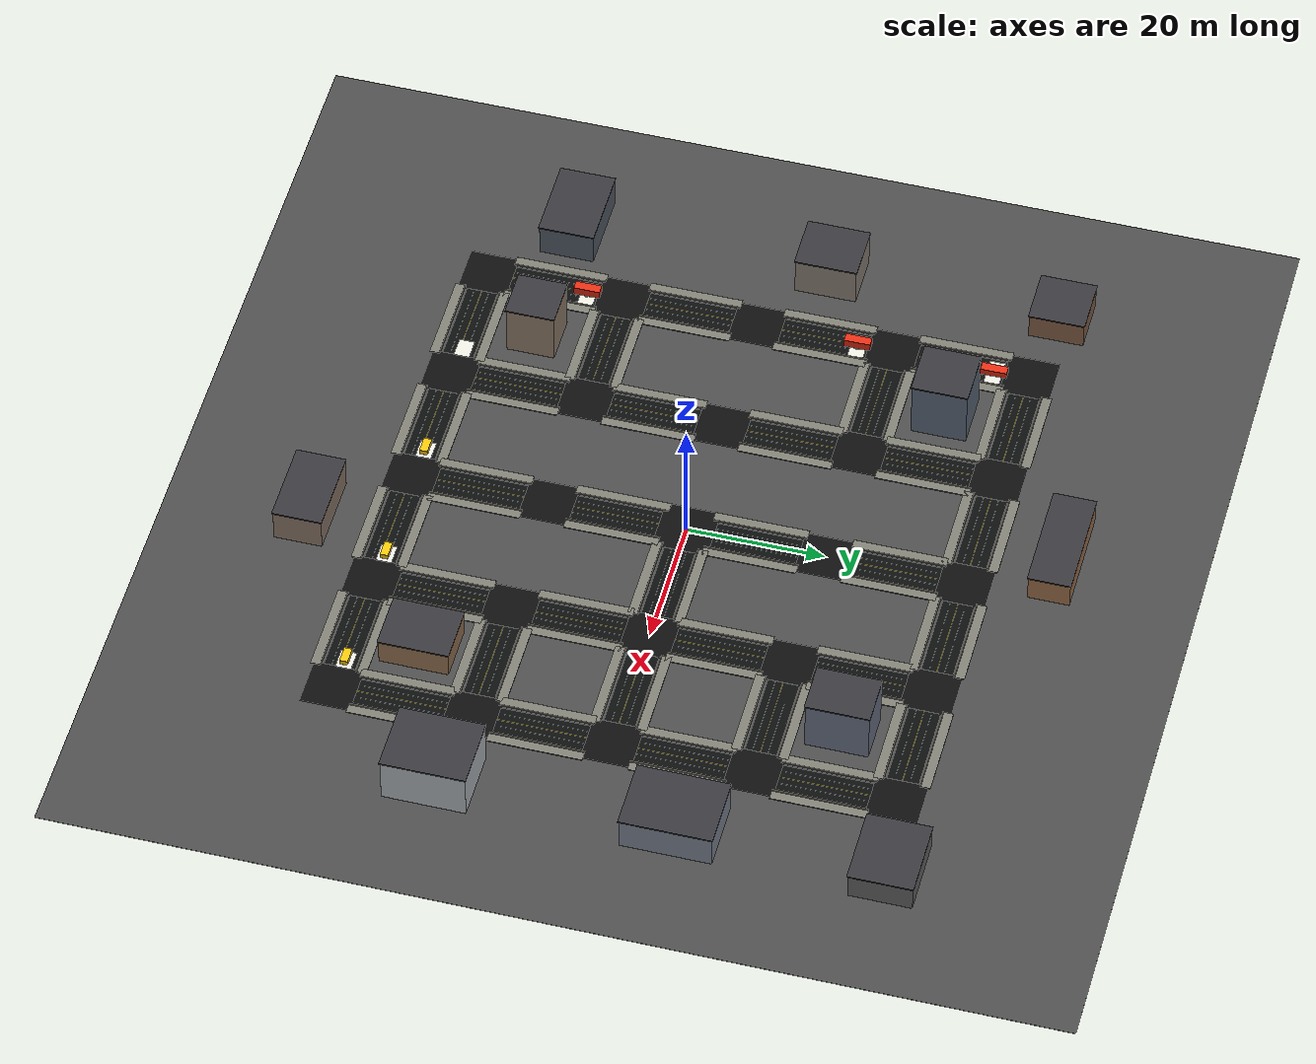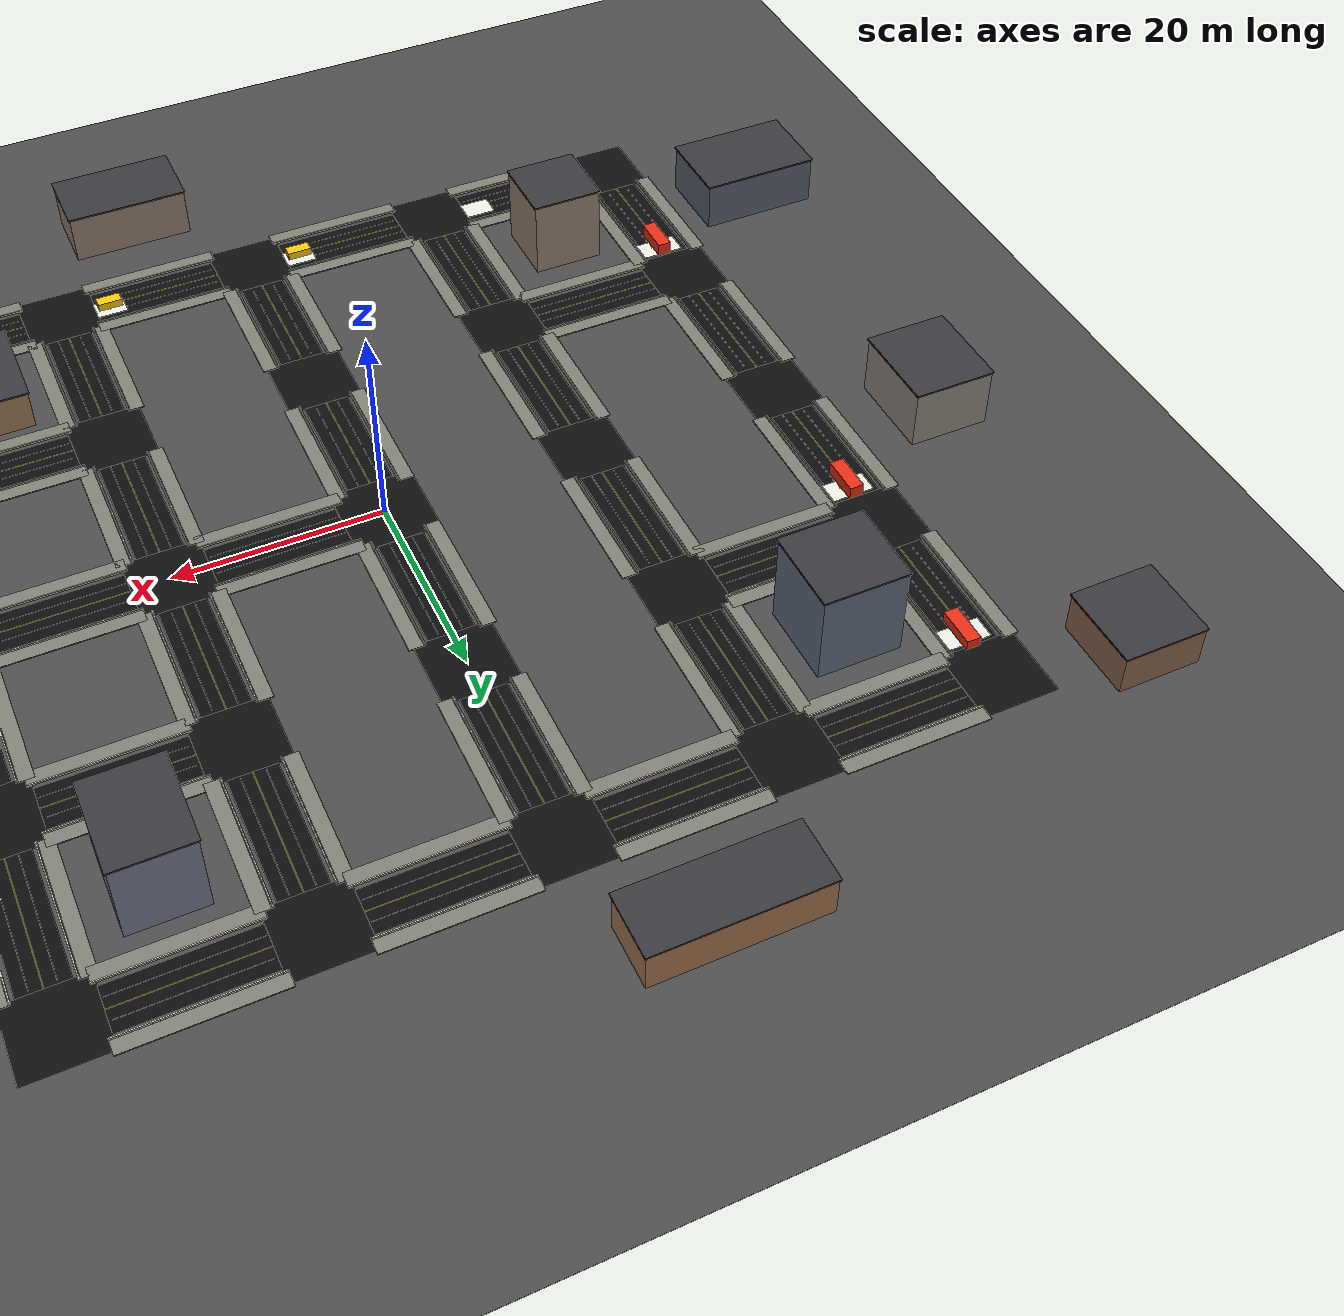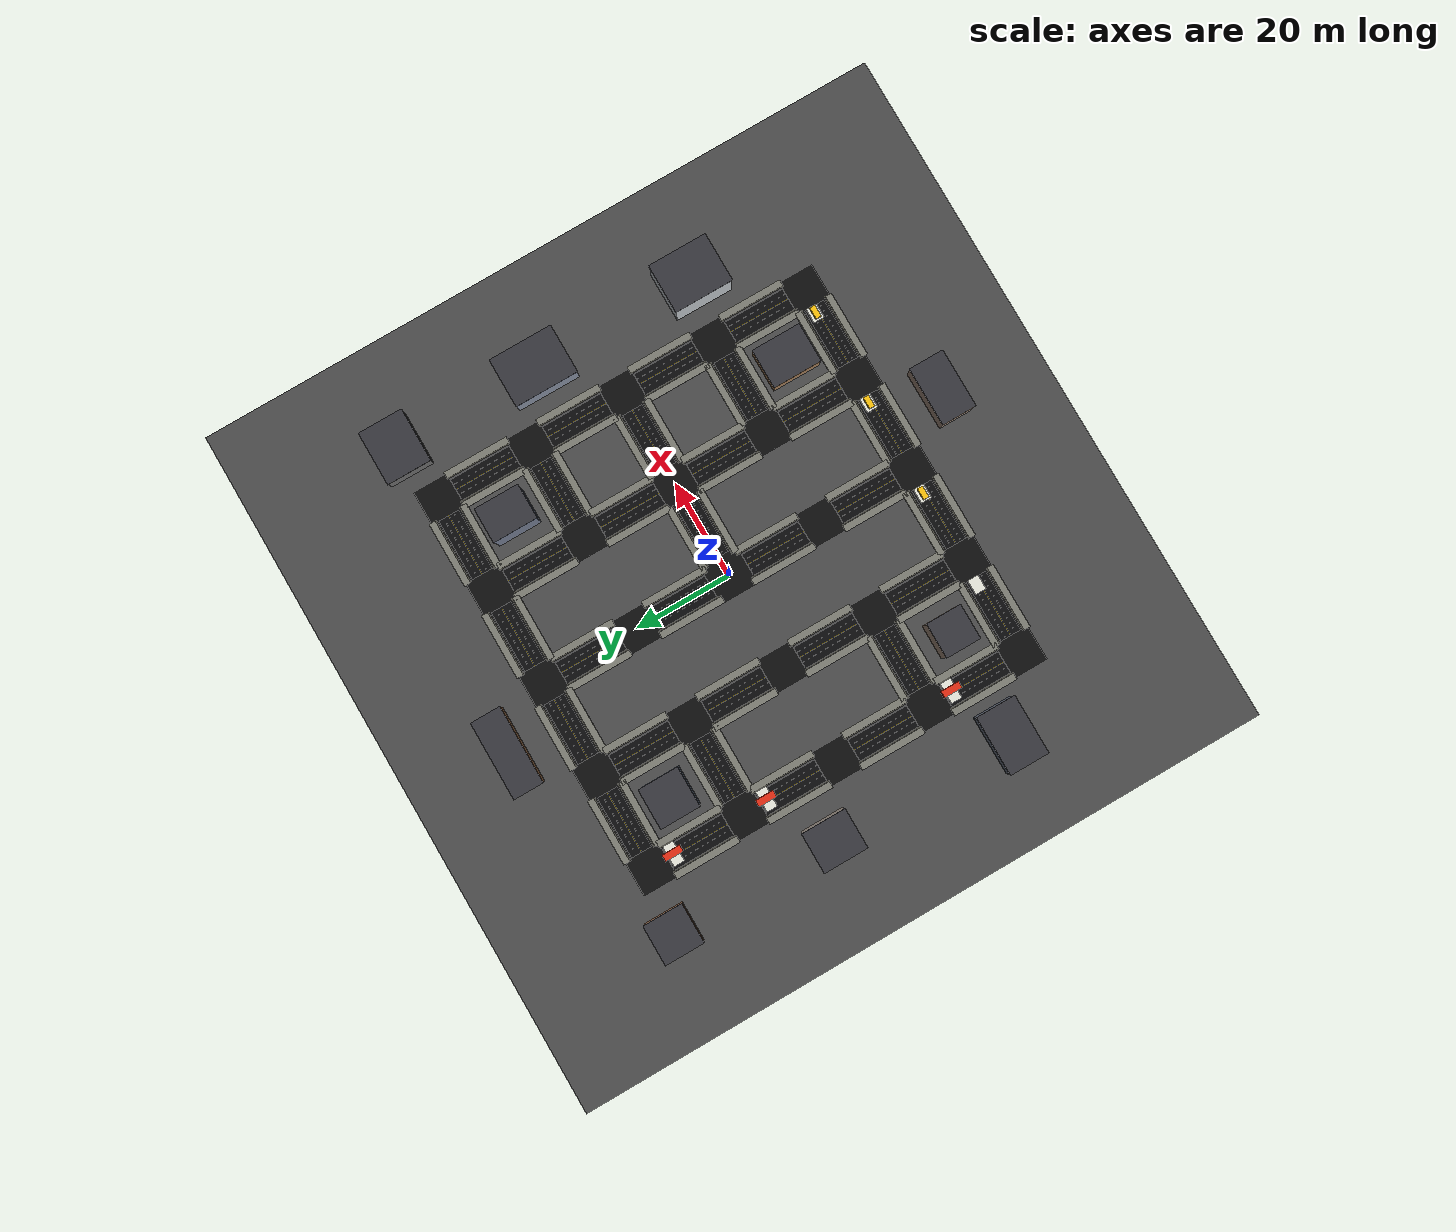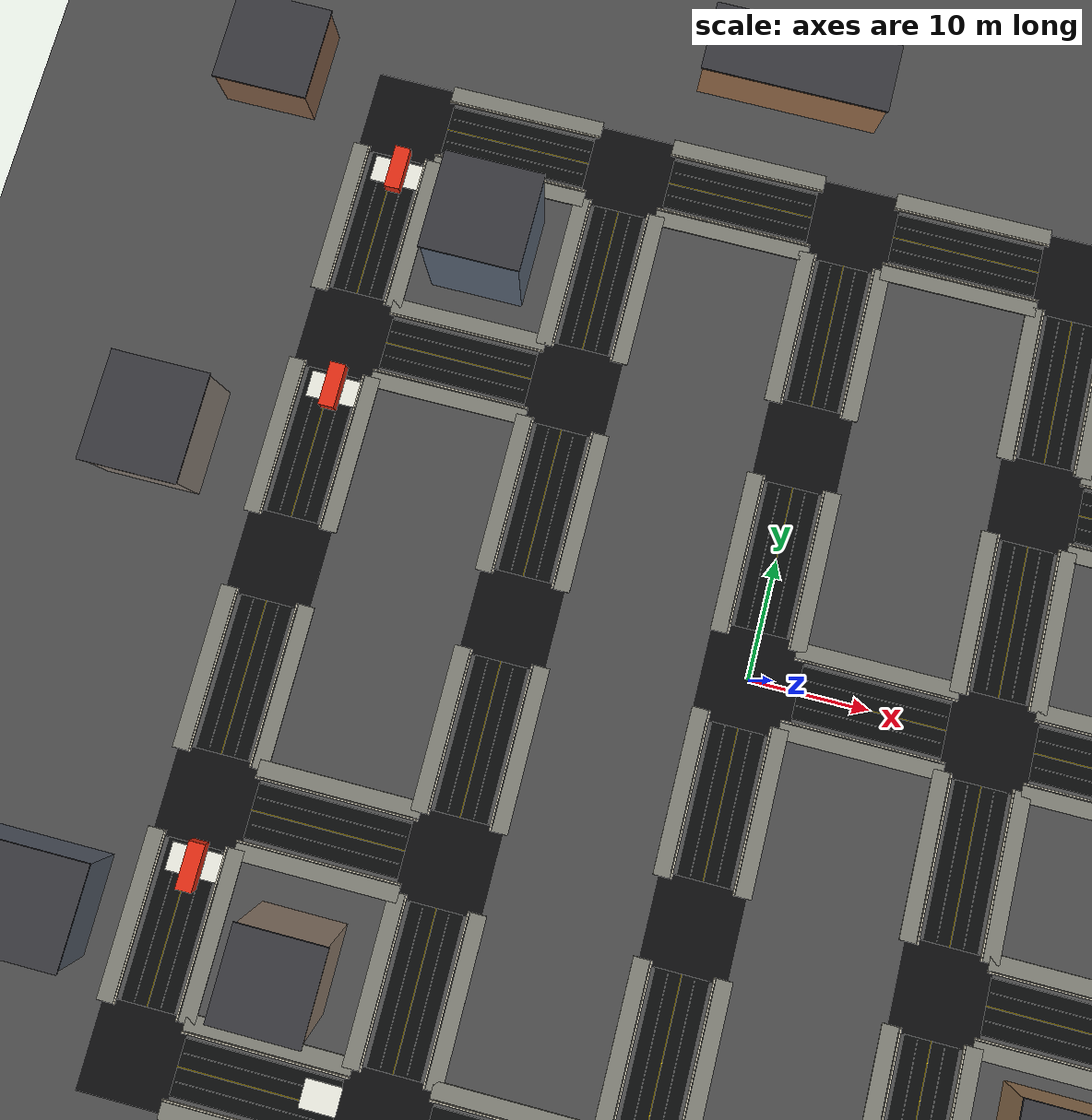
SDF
<?xml version='1.0' encoding='utf-8'?>
<sdf version="1.9">
  <world name="smart_city_world">
    <physics name="1ms" type="ignored">
      <max_step_size>0.001</max_step_size>
      <real_time_factor>1.0</real_time_factor>
    </physics>
    <plugin filename="gz-sim-physics-system" name="gz::sim::systems::Physics" />
    <plugin filename="gz-sim-user-commands-system" name="gz::sim::systems::UserCommands" />
    <plugin filename="gz-sim-scene-broadcaster-system" name="gz::sim::systems::SceneBroadcaster" />
    <plugin filename="gz-sim-sensors-system" name="gz::sim::systems::Sensors">
      <render_engine>ogre2</render_engine>
    </plugin>
    <scene>
      <ambient>0.62 0.68 0.78 1</ambient>
      <background>0.78 0.88 1.0 1</background>
      <shadows>true</shadows>
      <grid>false</grid>
    </scene>
    <light name="sun" type="directional">
      <pose>0 0 22 0.3 0.1 -0.7</pose>
      <cast_shadows>true</cast_shadows>
      <diffuse>0.95 0.88 0.75 1</diffuse>
      <specular>0.25 0.25 0.25 1</specular>
      <direction>-0.45 0.25 -0.85</direction>
    </light>
    <model name="ground">
      <static>true</static>
      <link name="link">
        <collision name="collision">
          <geometry>
            <box>
              <size>145 145 0.05</size>
            </box>
          </geometry>
        </collision>
        <visual name="visual">
          <geometry>
            <box>
              <size>145 145 0.05</size>
            </box>
          </geometry>
          <material>
            <ambient>0.30 0.30 0.30 1</ambient>
            <diffuse>0.30 0.30 0.30 1</diffuse>
          </material>
        </visual>
      </link>
    </model>
    <model name="road_e1">
      <static>true</static>
      <pose>-30.000 40.000 0.018 0 0 0.000000</pose>
      <link name="link">
        <collision name="collision">
          <geometry>
            <box>
              <size>13.600 4.350 0.030</size>
            </box>
          </geometry>
        </collision>
        <visual name="visual">
          <geometry>
            <box>
              <size>13.600 4.350 0.030</size>
            </box>
          </geometry>
          <material>
            <ambient>0.045 0.047 0.05 1</ambient>
            <diffuse>0.045 0.047 0.05 1</diffuse>
          </material>
        </visual>
      </link>
    </model>
    <model name="center_line_e1">
      <static>true</static>
      <pose>-30.000 40.000 0.052 0 0 0.000000</pose>
      <link name="link">
        <visual name="visual">
          <geometry>
            <box>
              <size>12.800 0.070 0.010</size>
            </box>
          </geometry>
          <material>
            <ambient>1 0.86 0.05 1</ambient>
            <diffuse>1 0.86 0.05 1</diffuse>
          </material>
        </visual>
      </link>
    </model>
    <model name="sidewalk_e1_L">
      <static>true</static>
      <pose>-30.000 43.350 0.075 0 0 0.000000</pose>
      <link name="link">
        <visual name="visual">
          <geometry>
            <box>
              <size>13.600 1.350 0.100</size>
            </box>
          </geometry>
          <material>
            <ambient>0.5 0.5 0.46 1</ambient>
            <diffuse>0.5 0.5 0.46 1</diffuse>
          </material>
        </visual>
      </link>
    </model>
    <model name="curb_e1_L">
      <static>true</static>
      <pose>-30.000 42.550 0.130 0 0 0.000000</pose>
      <link name="link">
        <visual name="visual">
          <geometry>
            <box>
              <size>13.600 0.120 0.180</size>
            </box>
          </geometry>
          <material>
            <ambient>0.8 0.78 0.7 1</ambient>
            <diffuse>0.8 0.78 0.7 1</diffuse>
          </material>
        </visual>
      </link>
    </model>
    <model name="edge_line_e1_L">
      <static>true</static>
      <pose>-30.000 41.080 0.054 0 0 0.000000</pose>
      <link name="link">
        <visual name="visual">
          <geometry>
            <box>
              <size>12.400 0.035 0.010</size>
            </box>
          </geometry>
          <material>
            <ambient>0.85 0.85 0.85 1</ambient>
            <diffuse>0.85 0.85 0.85 1</diffuse>
          </material>
        </visual>
      </link>
    </model>
    <model name="sidewalk_e1_R">
      <static>true</static>
      <pose>-30.000 36.650 0.075 0 0 0.000000</pose>
      <link name="link">
        <visual name="visual">
          <geometry>
            <box>
              <size>13.600 1.350 0.100</size>
            </box>
          </geometry>
          <material>
            <ambient>0.5 0.5 0.46 1</ambient>
            <diffuse>0.5 0.5 0.46 1</diffuse>
          </material>
        </visual>
      </link>
    </model>
    <model name="curb_e1_R">
      <static>true</static>
      <pose>-30.000 37.450 0.130 0 0 0.000000</pose>
      <link name="link">
        <visual name="visual">
          <geometry>
            <box>
              <size>13.600 0.120 0.180</size>
            </box>
          </geometry>
          <material>
            <ambient>0.8 0.78 0.7 1</ambient>
            <diffuse>0.8 0.78 0.7 1</diffuse>
          </material>
        </visual>
      </link>
    </model>
    <model name="edge_line_e1_R">
      <static>true</static>
      <pose>-30.000 38.920 0.054 0 0 0.000000</pose>
      <link name="link">
        <visual name="visual">
          <geometry>
            <box>
              <size>12.400 0.035 0.010</size>
            </box>
          </geometry>
          <material>
            <ambient>0.85 0.85 0.85 1</ambient>
            <diffuse>0.85 0.85 0.85 1</diffuse>
          </material>
        </visual>
      </link>
    </model>
    <model name="road_e2">
      <static>true</static>
      <pose>-10.000 40.000 0.018 0 0 0.000000</pose>
      <link name="link">
        <collision name="collision">
          <geometry>
            <box>
              <size>13.600 4.350 0.030</size>
            </box>
          </geometry>
        </collision>
        <visual name="visual">
          <geometry>
            <box>
              <size>13.600 4.350 0.030</size>
            </box>
          </geometry>
          <material>
            <ambient>0.045 0.047 0.05 1</ambient>
            <diffuse>0.045 0.047 0.05 1</diffuse>
          </material>
        </visual>
      </link>
    </model>
    <model name="center_line_e2">
      <static>true</static>
      <pose>-10.000 40.000 0.052 0 0 0.000000</pose>
      <link name="link">
        <visual name="visual">
          <geometry>
            <box>
              <size>12.800 0.070 0.010</size>
            </box>
          </geometry>
          <material>
            <ambient>1 0.86 0.05 1</ambient>
            <diffuse>1 0.86 0.05 1</diffuse>
          </material>
        </visual>
      </link>
    </model>
    <model name="sidewalk_e2_L">
      <static>true</static>
      <pose>-10.000 43.350 0.075 0 0 0.000000</pose>
      <link name="link">
        <visual name="visual">
          <geometry>
            <box>
              <size>13.600 1.350 0.100</size>
            </box>
          </geometry>
          <material>
            <ambient>0.5 0.5 0.46 1</ambient>
            <diffuse>0.5 0.5 0.46 1</diffuse>
          </material>
        </visual>
      </link>
    </model>
    <model name="curb_e2_L">
      <static>true</static>
      <pose>-10.000 42.550 0.130 0 0 0.000000</pose>
      <link name="link">
        <visual name="visual">
          <geometry>
            <box>
              <size>13.600 0.120 0.180</size>
            </box>
          </geometry>
          <material>
            <ambient>0.8 0.78 0.7 1</ambient>
            <diffuse>0.8 0.78 0.7 1</diffuse>
          </material>
        </visual>
      </link>
    </model>
    <model name="edge_line_e2_L">
      <static>true</static>
      <pose>-10.000 41.080 0.054 0 0 0.000000</pose>
      <link name="link">
        <visual name="visual">
          <geometry>
            <box>
              <size>12.400 0.035 0.010</size>
            </box>
          </geometry>
          <material>
            <ambient>0.85 0.85 0.85 1</ambient>
            <diffuse>0.85 0.85 0.85 1</diffuse>
          </material>
        </visual>
      </link>
    </model>
    <model name="sidewalk_e2_R">
      <static>true</static>
      <pose>-10.000 36.650 0.075 0 0 0.000000</pose>
      <link name="link">
        <visual name="visual">
          <geometry>
            <box>
              <size>13.600 1.350 0.100</size>
            </box>
          </geometry>
          <material>
            <ambient>0.5 0.5 0.46 1</ambient>
            <diffuse>0.5 0.5 0.46 1</diffuse>
          </material>
        </visual>
      </link>
    </model>
    <model name="curb_e2_R">
      <static>true</static>
      <pose>-10.000 37.450 0.130 0 0 0.000000</pose>
      <link name="link">
        <visual name="visual">
          <geometry>
            <box>
              <size>13.600 0.120 0.180</size>
            </box>
          </geometry>
          <material>
            <ambient>0.8 0.78 0.7 1</ambient>
            <diffuse>0.8 0.78 0.7 1</diffuse>
          </material>
        </visual>
      </link>
    </model>
    <model name="edge_line_e2_R">
      <static>true</static>
      <pose>-10.000 38.920 0.054 0 0 0.000000</pose>
      <link name="link">
        <visual name="visual">
          <geometry>
            <box>
              <size>12.400 0.035 0.010</size>
            </box>
          </geometry>
          <material>
            <ambient>0.85 0.85 0.85 1</ambient>
            <diffuse>0.85 0.85 0.85 1</diffuse>
          </material>
        </visual>
      </link>
    </model>
    <model name="road_e3">
      <static>true</static>
      <pose>10.000 40.000 0.018 0 0 0.000000</pose>
      <link name="link">
        <collision name="collision">
          <geometry>
            <box>
              <size>13.600 4.350 0.030</size>
            </box>
          </geometry>
        </collision>
        <visual name="visual">
          <geometry>
            <box>
              <size>13.600 4.350 0.030</size>
            </box>
          </geometry>
          <material>
            <ambient>0.045 0.047 0.05 1</ambient>
            <diffuse>0.045 0.047 0.05 1</diffuse>
          </material>
        </visual>
      </link>
    </model>
    <model name="center_line_e3">
      <static>true</static>
      <pose>10.000 40.000 0.052 0 0 0.000000</pose>
      <link name="link">
        <visual name="visual">
          <geometry>
            <box>
              <size>12.800 0.070 0.010</size>
            </box>
          </geometry>
          <material>
            <ambient>1 0.86 0.05 1</ambient>
            <diffuse>1 0.86 0.05 1</diffuse>
          </material>
        </visual>
      </link>
    </model>
    <model name="sidewalk_e3_L">
      <static>true</static>
      <pose>10.000 43.350 0.075 0 0 0.000000</pose>
      <link name="link">
        <visual name="visual">
          <geometry>
            <box>
              <size>13.600 1.350 0.100</size>
            </box>
          </geometry>
          <material>
            <ambient>0.5 0.5 0.46 1</ambient>
            <diffuse>0.5 0.5 0.46 1</diffuse>
          </material>
        </visual>
      </link>
    </model>
    <model name="curb_e3_L">
      <static>true</static>
      <pose>10.000 42.550 0.130 0 0 0.000000</pose>
      <link name="link">
        <visual name="visual">
          <geometry>
            <box>
              <size>13.600 0.120 0.180</size>
            </box>
          </geometry>
          <material>
            <ambient>0.8 0.78 0.7 1</ambient>
            <diffuse>0.8 0.78 0.7 1</diffuse>
          </material>
        </visual>
      </link>
    </model>
    <model name="edge_line_e3_L">
      <static>true</static>
      <pose>10.000 41.080 0.054 0 0 0.000000</pose>
      <link name="link">
        <visual name="visual">
          <geometry>
            <box>
              <size>12.400 0.035 0.010</size>
            </box>
          </geometry>
          <material>
            <ambient>0.85 0.85 0.85 1</ambient>
            <diffuse>0.85 0.85 0.85 1</diffuse>
          </material>
        </visual>
      </link>
    </model>
    <model name="sidewalk_e3_R">
      <static>true</static>
      <pose>10.000 36.650 0.075 0 0 0.000000</pose>
      <link name="link">
        <visual name="visual">
          <geometry>
            <box>
              <size>13.600 1.350 0.100</size>
            </box>
          </geometry>
          <material>
            <ambient>0.5 0.5 0.46 1</ambient>
            <diffuse>0.5 0.5 0.46 1</diffuse>
          </material>
        </visual>
      </link>
    </model>
    <model name="curb_e3_R">
      <static>true</static>
      <pose>10.000 37.450 0.130 0 0 0.000000</pose>
      <link name="link">
        <visual name="visual">
          <geometry>
            <box>
              <size>13.600 0.120 0.180</size>
            </box>
          </geometry>
          <material>
            <ambient>0.8 0.78 0.7 1</ambient>
            <diffuse>0.8 0.78 0.7 1</diffuse>
          </material>
        </visual>
      </link>
    </model>
    <model name="edge_line_e3_R">
      <static>true</static>
      <pose>10.000 38.920 0.054 0 0 0.000000</pose>
      <link name="link">
        <visual name="visual">
          <geometry>
            <box>
              <size>12.400 0.035 0.010</size>
            </box>
          </geometry>
          <material>
            <ambient>0.85 0.85 0.85 1</ambient>
            <diffuse>0.85 0.85 0.85 1</diffuse>
          </material>
        </visual>
      </link>
    </model>
    <model name="road_e4">
      <static>true</static>
      <pose>30.000 40.000 0.018 0 0 0.000000</pose>
      <link name="link">
        <collision name="collision">
          <geometry>
            <box>
              <size>13.600 4.350 0.030</size>
            </box>
          </geometry>
        </collision>
        <visual name="visual">
          <geometry>
            <box>
              <size>13.600 4.350 0.030</size>
            </box>
          </geometry>
          <material>
            <ambient>0.045 0.047 0.05 1</ambient>
            <diffuse>0.045 0.047 0.05 1</diffuse>
          </material>
        </visual>
      </link>
    </model>
    <model name="center_line_e4">
      <static>true</static>
      <pose>30.000 40.000 0.052 0 0 0.000000</pose>
      <link name="link">
        <visual name="visual">
          <geometry>
            <box>
              <size>12.800 0.070 0.010</size>
            </box>
          </geometry>
          <material>
            <ambient>1 0.86 0.05 1</ambient>
            <diffuse>1 0.86 0.05 1</diffuse>
          </material>
        </visual>
      </link>
    </model>
    <model name="sidewalk_e4_L">
      <static>true</static>
      <pose>30.000 43.350 0.075 0 0 0.000000</pose>
      <link name="link">
        <visual name="visual">
          <geometry>
            <box>
              <size>13.600 1.350 0.100</size>
            </box>
          </geometry>
          <material>
            <ambient>0.5 0.5 0.46 1</ambient>
            <diffuse>0.5 0.5 0.46 1</diffuse>
          </material>
        </visual>
      </link>
    </model>
    <model name="curb_e4_L">
      <static>true</static>
      <pose>30.000 42.550 0.130 0 0 0.000000</pose>
      <link name="link">
        <visual name="visual">
          <geometry>
            <box>
              <size>13.600 0.120 0.180</size>
            </box>
          </geometry>
          <material>
            <ambient>0.8 0.78 0.7 1</ambient>
            <diffuse>0.8 0.78 0.7 1</diffuse>
          </material>
        </visual>
      </link>
    </model>
    <model name="edge_line_e4_L">
      <static>true</static>
      <pose>30.000 41.080 0.054 0 0 0.000000</pose>
      <link name="link">
        <visual name="visual">
          <geometry>
            <box>
              <size>12.400 0.035 0.010</size>
            </box>
          </geometry>
          <material>
            <ambient>0.85 0.85 0.85 1</ambient>
            <diffuse>0.85 0.85 0.85 1</diffuse>
          </material>
        </visual>
      </link>
    </model>
    <model name="sidewalk_e4_R">
      <static>true</static>
      <pose>30.000 36.650 0.075 0 0 0.000000</pose>
      <link name="link">
        <visual name="visual">
          <geometry>
            <box>
              <size>13.600 1.350 0.100</size>
            </box>
          </geometry>
          <material>
            <ambient>0.5 0.5 0.46 1</ambient>
            <diffuse>0.5 0.5 0.46 1</diffuse>
          </material>
        </visual>
      </link>
    </model>
    <model name="curb_e4_R">
      <static>true</static>
      <pose>30.000 37.450 0.130 0 0 0.000000</pose>
      <link name="link">
        <visual name="visual">
          <geometry>
            <box>
              <size>13.600 0.120 0.180</size>
            </box>
          </geometry>
          <material>
            <ambient>0.8 0.78 0.7 1</ambient>
            <diffuse>0.8 0.78 0.7 1</diffuse>
          </material>
        </visual>
      </link>
    </model>
    <model name="edge_line_e4_R">
      <static>true</static>
      <pose>30.000 38.920 0.054 0 0 0.000000</pose>
      <link name="link">
        <visual name="visual">
          <geometry>
            <box>
              <size>12.400 0.035 0.010</size>
            </box>
          </geometry>
          <material>
            <ambient>0.85 0.85 0.85 1</ambient>
            <diffuse>0.85 0.85 0.85 1</diffuse>
          </material>
        </visual>
      </link>
    </model>
    <model name="road_e5">
      <static>true</static>
      <pose>-30.000 20.000 0.018 0 0 0.000000</pose>
      <link name="link">
        <collision name="collision">
          <geometry>
            <box>
              <size>13.600 4.350 0.030</size>
            </box>
          </geometry>
        </collision>
        <visual name="visual">
          <geometry>
            <box>
              <size>13.600 4.350 0.030</size>
            </box>
          </geometry>
          <material>
            <ambient>0.045 0.047 0.05 1</ambient>
            <diffuse>0.045 0.047 0.05 1</diffuse>
          </material>
        </visual>
      </link>
    </model>
    <model name="center_line_e5">
      <static>true</static>
      <pose>-30.000 20.000 0.052 0 0 0.000000</pose>
      <link name="link">
        <visual name="visual">
          <geometry>
            <box>
              <size>12.800 0.070 0.010</size>
            </box>
          </geometry>
          <material>
            <ambient>1 0.86 0.05 1</ambient>
            <diffuse>1 0.86 0.05 1</diffuse>
          </material>
        </visual>
      </link>
    </model>
    <model name="sidewalk_e5_L">
      <static>true</static>
      <pose>-30.000 23.350 0.075 0 0 0.000000</pose>
      <link name="link">
        <visual name="visual">
          <geometry>
            <box>
              <size>13.600 1.350 0.100</size>
            </box>
          </geometry>
          <material>
            <ambient>0.5 0.5 0.46 1</ambient>
            <diffuse>0.5 0.5 0.46 1</diffuse>
          </material>
        </visual>
      </link>
    </model>
    <model name="curb_e5_L">
      <static>true</static>
      <pose>-30.000 22.550 0.130 0 0 0.000000</pose>
      <link name="link">
        <visual name="visual">
          <geometry>
            <box>
              <size>13.600 0.120 0.180</size>
            </box>
          </geometry>
          <material>
            <ambient>0.8 0.78 0.7 1</ambient>
            <diffuse>0.8 0.78 0.7 1</diffuse>
          </material>
        </visual>
      </link>
    </model>
    <model name="edge_line_e5_L">
      <static>true</static>
      <pose>-30.000 21.080 0.054 0 0 0.000000</pose>
      <link name="link">
        <visual name="visual">
          <geometry>
            <box>
              <size>12.400 0.035 0.010</size>
            </box>
          </geometry>
          <material>
            <ambient>0.85 0.85 0.85 1</ambient>
            <diffuse>0.85 0.85 0.85 1</diffuse>
          </material>
        </visual>
      </link>
    </model>
    <model name="sidewalk_e5_R">
      <static>true</static>
      <pose>-30.000 16.650 0.075 0 0 0.000000</pose>
      <link name="link">
        <visual name="visual">
          <geometry>
            <box>
              <size>13.600 1.350 0.100</size>
            </box>
          </geometry>
          <material>
            <ambient>0.5 0.5 0.46 1</ambient>
            <diffuse>0.5 0.5 0.46 1</diffuse>
          </material>
        </visual>
      </link>
    </model>
    <model name="curb_e5_R">
      <static>true</static>
      <pose>-30.000 17.450 0.130 0 0 0.000000</pose>
      <link name="link">
        <visual name="visual">
          <geometry>
            <box>
              <size>13.600 0.120 0.180</size>
            </box>
          </geometry>
          <material>
            <ambient>0.8 0.78 0.7 1</ambient>
            <diffuse>0.8 0.78 0.7 1</diffuse>
          </material>
        </visual>
      </link>
    </model>
    <model name="edge_line_e5_R">
      <static>true</static>
      <pose>-30.000 18.920 0.054 0 0 0.000000</pose>
      <link name="link">
        <visual name="visual">
          <geometry>
            <box>
              <size>12.400 0.035 0.010</size>
            </box>
          </geometry>
          <material>
            <ambient>0.85 0.85 0.85 1</ambient>
            <diffuse>0.85 0.85 0.85 1</diffuse>
          </material>
        </visual>
      </link>
    </model>
    <model name="road_e8">
      <static>true</static>
      <pose>30.000 20.000 0.018 0 0 0.000000</pose>
      <link name="link">
        <collision name="collision">
          <geometry>
            <box>
              <size>13.600 4.350 0.030</size>
            </box>
          </geometry>
        </collision>
        <visual name="visual">
          <geometry>
            <box>
              <size>13.600 4.350 0.030</size>
            </box>
          </geometry>
          <material>
            <ambient>0.045 0.047 0.05 1</ambient>
            <diffuse>0.045 0.047 0.05 1</diffuse>
          </material>
        </visual>
      </link>
    </model>
    <model name="center_line_e8">
      <static>true</static>
      <pose>30.000 20.000 0.052 0 0 0.000000</pose>
      <link name="link">
        <visual name="visual">
          <geometry>
            <box>
              <size>12.800 0.070 0.010</size>
            </box>
          </geometry>
          <material>
            <ambient>1 0.86 0.05 1</ambient>
            <diffuse>1 0.86 0.05 1</diffuse>
          </material>
        </visual>
      </link>
    </model>
    <model name="sidewalk_e8_L">
      <static>true</static>
      <pose>30.000 23.350 0.075 0 0 0.000000</pose>
      <link name="link">
        <visual name="visual">
          <geometry>
            <box>
              <size>13.600 1.350 0.100</size>
            </box>
          </geometry>
          <material>
            <ambient>0.5 0.5 0.46 1</ambient>
            <diffuse>0.5 0.5 0.46 1</diffuse>
          </material>
        </visual>
      </link>
    </model>
    <model name="curb_e8_L">
      <static>true</static>
      <pose>30.000 22.550 0.130 0 0 0.000000</pose>
      <link name="link">
        <visual name="visual">
          <geometry>
            <box>
              <size>13.600 0.120 0.180</size>
            </box>
          </geometry>
          <material>
            <ambient>0.8 0.78 0.7 1</ambient>
            <diffuse>0.8 0.78 0.7 1</diffuse>
          </material>
        </visual>
      </link>
    </model>
    <model name="edge_line_e8_L">
      <static>true</static>
      <pose>30.000 21.080 0.054 0 0 0.000000</pose>
      <link name="link">
        <visual name="visual">
          <geometry>
            <box>
              <size>12.400 0.035 0.010</size>
            </box>
          </geometry>
          <material>
            <ambient>0.85 0.85 0.85 1</ambient>
            <diffuse>0.85 0.85 0.85 1</diffuse>
          </material>
        </visual>
      </link>
    </model>
    <model name="sidewalk_e8_R">
      <static>true</static>
      <pose>30.000 16.650 0.075 0 0 0.000000</pose>
      <link name="link">
        <visual name="visual">
          <geometry>
            <box>
              <size>13.600 1.350 0.100</size>
            </box>
          </geometry>
          <material>
            <ambient>0.5 0.5 0.46 1</ambient>
            <diffuse>0.5 0.5 0.46 1</diffuse>
          </material>
        </visual>
      </link>
    </model>
    <model name="curb_e8_R">
      <static>true</static>
      <pose>30.000 17.450 0.130 0 0 0.000000</pose>
      <link name="link">
        <visual name="visual">
          <geometry>
            <box>
              <size>13.600 0.120 0.180</size>
            </box>
          </geometry>
          <material>
            <ambient>0.8 0.78 0.7 1</ambient>
            <diffuse>0.8 0.78 0.7 1</diffuse>
          </material>
        </visual>
      </link>
    </model>
    <model name="edge_line_e8_R">
      <static>true</static>
      <pose>30.000 18.920 0.054 0 0 0.000000</pose>
      <link name="link">
        <visual name="visual">
          <geometry>
            <box>
              <size>12.400 0.035 0.010</size>
            </box>
          </geometry>
          <material>
            <ambient>0.85 0.85 0.85 1</ambient>
            <diffuse>0.85 0.85 0.85 1</diffuse>
          </material>
        </visual>
      </link>
    </model>
    <model name="road_e11">
      <static>true</static>
      <pose>10.000 0.000 0.018 0 0 0.000000</pose>
      <link name="link">
        <collision name="collision">
          <geometry>
            <box>
              <size>13.600 4.350 0.030</size>
            </box>
          </geometry>
        </collision>
        <visual name="visual">
          <geometry>
            <box>
              <size>13.600 4.350 0.030</size>
            </box>
          </geometry>
          <material>
            <ambient>0.045 0.047 0.05 1</ambient>
            <diffuse>0.045 0.047 0.05 1</diffuse>
          </material>
        </visual>
      </link>
    </model>
    <model name="center_line_e11">
      <static>true</static>
      <pose>10.000 0.000 0.052 0 0 0.000000</pose>
      <link name="link">
        <visual name="visual">
          <geometry>
            <box>
              <size>12.800 0.070 0.010</size>
            </box>
          </geometry>
          <material>
            <ambient>1 0.86 0.05 1</ambient>
            <diffuse>1 0.86 0.05 1</diffuse>
          </material>
        </visual>
      </link>
    </model>
    <model name="sidewalk_e11_L">
      <static>true</static>
      <pose>10.000 3.350 0.075 0 0 0.000000</pose>
      <link name="link">
        <visual name="visual">
          <geometry>
            <box>
              <size>13.600 1.350 0.100</size>
            </box>
          </geometry>
          <material>
            <ambient>0.5 0.5 0.46 1</ambient>
            <diffuse>0.5 0.5 0.46 1</diffuse>
          </material>
        </visual>
      </link>
    </model>
    <model name="curb_e11_L">
      <static>true</static>
      <pose>10.000 2.550 0.130 0 0 0.000000</pose>
      <link name="link">
        <visual name="visual">
          <geometry>
            <box>
              <size>13.600 0.120 0.180</size>
            </box>
          </geometry>
          <material>
            <ambient>0.8 0.78 0.7 1</ambient>
            <diffuse>0.8 0.78 0.7 1</diffuse>
          </material>
        </visual>
      </link>
    </model>
    <model name="edge_line_e11_L">
      <static>true</static>
      <pose>10.000 1.080 0.054 0 0 0.000000</pose>
      <link name="link">
        <visual name="visual">
          <geometry>
            <box>
              <size>12.400 0.035 0.010</size>
            </box>
          </geometry>
          <material>
            <ambient>0.85 0.85 0.85 1</ambient>
            <diffuse>0.85 0.85 0.85 1</diffuse>
          </material>
        </visual>
      </link>
    </model>
    <model name="sidewalk_e11_R">
      <static>true</static>
      <pose>10.000 -3.350 0.075 0 0 0.000000</pose>
      <link name="link">
        <visual name="visual">
          <geometry>
            <box>
              <size>13.600 1.350 0.100</size>
            </box>
          </geometry>
          <material>
            <ambient>0.5 0.5 0.46 1</ambient>
            <diffuse>0.5 0.5 0.46 1</diffuse>
          </material>
        </visual>
      </link>
    </model>
    <model name="curb_e11_R">
      <static>true</static>
      <pose>10.000 -2.550 0.130 0 0 0.000000</pose>
      <link name="link">
        <visual name="visual">
          <geometry>
            <box>
              <size>13.600 0.120 0.180</size>
            </box>
          </geometry>
          <material>
            <ambient>0.8 0.78 0.7 1</ambient>
            <diffuse>0.8 0.78 0.7 1</diffuse>
          </material>
        </visual>
      </link>
    </model>
    <model name="edge_line_e11_R">
      <static>true</static>
      <pose>10.000 -1.080 0.054 0 0 0.000000</pose>
      <link name="link">
        <visual name="visual">
          <geometry>
            <box>
              <size>12.400 0.035 0.010</size>
            </box>
          </geometry>
          <material>
            <ambient>0.85 0.85 0.85 1</ambient>
            <diffuse>0.85 0.85 0.85 1</diffuse>
          </material>
        </visual>
      </link>
    </model>
    <model name="road_e12">
      <static>true</static>
      <pose>30.000 0.000 0.018 0 0 0.000000</pose>
      <link name="link">
        <collision name="collision">
          <geometry>
            <box>
              <size>13.600 4.350 0.030</size>
            </box>
          </geometry>
        </collision>
        <visual name="visual">
          <geometry>
            <box>
              <size>13.600 4.350 0.030</size>
            </box>
          </geometry>
          <material>
            <ambient>0.045 0.047 0.05 1</ambient>
            <diffuse>0.045 0.047 0.05 1</diffuse>
          </material>
        </visual>
      </link>
    </model>
    <model name="center_line_e12">
      <static>true</static>
      <pose>30.000 0.000 0.052 0 0 0.000000</pose>
      <link name="link">
        <visual name="visual">
          <geometry>
            <box>
              <size>12.800 0.070 0.010</size>
            </box>
          </geometry>
          <material>
            <ambient>1 0.86 0.05 1</ambient>
            <diffuse>1 0.86 0.05 1</diffuse>
          </material>
        </visual>
      </link>
    </model>
    <model name="sidewalk_e12_L">
      <static>true</static>
      <pose>30.000 3.350 0.075 0 0 0.000000</pose>
      <link name="link">
        <visual name="visual">
          <geometry>
            <box>
              <size>13.600 1.350 0.100</size>
            </box>
          </geometry>
          <material>
            <ambient>0.5 0.5 0.46 1</ambient>
            <diffuse>0.5 0.5 0.46 1</diffuse>
          </material>
        </visual>
      </link>
    </model>
    <model name="curb_e12_L">
      <static>true</static>
      <pose>30.000 2.550 0.130 0 0 0.000000</pose>
      <link name="link">
        <visual name="visual">
          <geometry>
            <box>
              <size>13.600 0.120 0.180</size>
            </box>
          </geometry>
          <material>
            <ambient>0.8 0.78 0.7 1</ambient>
            <diffuse>0.8 0.78 0.7 1</diffuse>
          </material>
        </visual>
      </link>
    </model>
    <model name="edge_line_e12_L">
      <static>true</static>
      <pose>30.000 1.080 0.054 0 0 0.000000</pose>
      <link name="link">
        <visual name="visual">
          <geometry>
            <box>
              <size>12.400 0.035 0.010</size>
            </box>
          </geometry>
          <material>
            <ambient>0.85 0.85 0.85 1</ambient>
            <diffuse>0.85 0.85 0.85 1</diffuse>
          </material>
        </visual>
      </link>
    </model>
    <model name="sidewalk_e12_R">
      <static>true</static>
      <pose>30.000 -3.350 0.075 0 0 0.000000</pose>
      <link name="link">
        <visual name="visual">
          <geometry>
            <box>
              <size>13.600 1.350 0.100</size>
            </box>
          </geometry>
          <material>
            <ambient>0.5 0.5 0.46 1</ambient>
            <diffuse>0.5 0.5 0.46 1</diffuse>
          </material>
        </visual>
      </link>
    </model>
    <model name="curb_e12_R">
      <static>true</static>
      <pose>30.000 -2.550 0.130 0 0 0.000000</pose>
      <link name="link">
        <visual name="visual">
          <geometry>
            <box>
              <size>13.600 0.120 0.180</size>
            </box>
          </geometry>
          <material>
            <ambient>0.8 0.78 0.7 1</ambient>
            <diffuse>0.8 0.78 0.7 1</diffuse>
          </material>
        </visual>
      </link>
    </model>
    <model name="edge_line_e12_R">
      <static>true</static>
      <pose>30.000 -1.080 0.054 0 0 0.000000</pose>
      <link name="link">
        <visual name="visual">
          <geometry>
            <box>
              <size>12.400 0.035 0.010</size>
            </box>
          </geometry>
          <material>
            <ambient>0.85 0.85 0.85 1</ambient>
            <diffuse>0.85 0.85 0.85 1</diffuse>
          </material>
        </visual>
      </link>
    </model>
    <model name="road_e13">
      <static>true</static>
      <pose>-30.000 -20.000 0.018 0 0 0.000000</pose>
      <link name="link">
        <collision name="collision">
          <geometry>
            <box>
              <size>13.600 4.350 0.030</size>
            </box>
          </geometry>
        </collision>
        <visual name="visual">
          <geometry>
            <box>
              <size>13.600 4.350 0.030</size>
            </box>
          </geometry>
          <material>
            <ambient>0.045 0.047 0.05 1</ambient>
            <diffuse>0.045 0.047 0.05 1</diffuse>
          </material>
        </visual>
      </link>
    </model>
    <model name="center_line_e13">
      <static>true</static>
      <pose>-30.000 -20.000 0.052 0 0 0.000000</pose>
      <link name="link">
        <visual name="visual">
          <geometry>
            <box>
              <size>12.800 0.070 0.010</size>
            </box>
          </geometry>
          <material>
            <ambient>1 0.86 0.05 1</ambient>
            <diffuse>1 0.86 0.05 1</diffuse>
          </material>
        </visual>
      </link>
    </model>
    <model name="sidewalk_e13_L">
      <static>true</static>
      <pose>-30.000 -16.650 0.075 0 0 0.000000</pose>
      <link name="link">
        <visual name="visual">
          <geometry>
            <box>
              <size>13.600 1.350 0.100</size>
            </box>
          </geometry>
          <material>
            <ambient>0.5 0.5 0.46 1</ambient>
            <diffuse>0.5 0.5 0.46 1</diffuse>
          </material>
        </visual>
      </link>
    </model>
    <model name="curb_e13_L">
      <static>true</static>
      <pose>-30.000 -17.450 0.130 0 0 0.000000</pose>
      <link name="link">
        <visual name="visual">
          <geometry>
            <box>
              <size>13.600 0.120 0.180</size>
            </box>
          </geometry>
          <material>
            <ambient>0.8 0.78 0.7 1</ambient>
            <diffuse>0.8 0.78 0.7 1</diffuse>
          </material>
        </visual>
      </link>
    </model>
    <model name="edge_line_e13_L">
      <static>true</static>
      <pose>-30.000 -18.920 0.054 0 0 0.000000</pose>
      <link name="link">
        <visual name="visual">
          <geometry>
            <box>
              <size>12.400 0.035 0.010</size>
            </box>
          </geometry>
          <material>
            <ambient>0.85 0.85 0.85 1</ambient>
            <diffuse>0.85 0.85 0.85 1</diffuse>
          </material>
        </visual>
      </link>
    </model>
    <model name="sidewalk_e13_R">
      <static>true</static>
      <pose>-30.000 -23.350 0.075 0 0 0.000000</pose>
      <link name="link">
        <visual name="visual">
          <geometry>
            <box>
              <size>13.600 1.350 0.100</size>
            </box>
          </geometry>
          <material>
            <ambient>0.5 0.5 0.46 1</ambient>
            <diffuse>0.5 0.5 0.46 1</diffuse>
          </material>
        </visual>
      </link>
    </model>
    <model name="curb_e13_R">
      <static>true</static>
      <pose>-30.000 -22.550 0.130 0 0 0.000000</pose>
      <link name="link">
        <visual name="visual">
          <geometry>
            <box>
              <size>13.600 0.120 0.180</size>
            </box>
          </geometry>
          <material>
            <ambient>0.8 0.78 0.7 1</ambient>
            <diffuse>0.8 0.78 0.7 1</diffuse>
          </material>
        </visual>
      </link>
    </model>
    <model name="edge_line_e13_R">
      <static>true</static>
      <pose>-30.000 -21.080 0.054 0 0 0.000000</pose>
      <link name="link">
        <visual name="visual">
          <geometry>
            <box>
              <size>12.400 0.035 0.010</size>
            </box>
          </geometry>
          <material>
            <ambient>0.85 0.85 0.85 1</ambient>
            <diffuse>0.85 0.85 0.85 1</diffuse>
          </material>
        </visual>
      </link>
    </model>
    <model name="road_e16">
      <static>true</static>
      <pose>30.000 -20.000 0.018 0 0 0.000000</pose>
      <link name="link">
        <collision name="collision">
          <geometry>
            <box>
              <size>13.600 4.350 0.030</size>
            </box>
          </geometry>
        </collision>
        <visual name="visual">
          <geometry>
            <box>
              <size>13.600 4.350 0.030</size>
            </box>
          </geometry>
          <material>
            <ambient>0.045 0.047 0.05 1</ambient>
            <diffuse>0.045 0.047 0.05 1</diffuse>
          </material>
        </visual>
      </link>
    </model>
    <model name="center_line_e16">
      <static>true</static>
      <pose>30.000 -20.000 0.052 0 0 0.000000</pose>
      <link name="link">
        <visual name="visual">
          <geometry>
            <box>
              <size>12.800 0.070 0.010</size>
            </box>
          </geometry>
          <material>
            <ambient>1 0.86 0.05 1</ambient>
            <diffuse>1 0.86 0.05 1</diffuse>
          </material>
        </visual>
      </link>
    </model>
    <model name="sidewalk_e16_L">
      <static>true</static>
      <pose>30.000 -16.650 0.075 0 0 0.000000</pose>
      <link name="link">
        <visual name="visual">
          <geometry>
            <box>
              <size>13.600 1.350 0.100</size>
            </box>
          </geometry>
          <material>
            <ambient>0.5 0.5 0.46 1</ambient>
            <diffuse>0.5 0.5 0.46 1</diffuse>
          </material>
        </visual>
      </link>
    </model>
    <model name="curb_e16_L">
      <static>true</static>
      <pose>30.000 -17.450 0.130 0 0 0.000000</pose>
      <link name="link">
        <visual name="visual">
          <geometry>
            <box>
              <size>13.600 0.120 0.180</size>
            </box>
          </geometry>
          <material>
            <ambient>0.8 0.78 0.7 1</ambient>
            <diffuse>0.8 0.78 0.7 1</diffuse>
          </material>
        </visual>
      </link>
    </model>
    <model name="edge_line_e16_L">
      <static>true</static>
      <pose>30.000 -18.920 0.054 0 0 0.000000</pose>
      <link name="link">
        <visual name="visual">
          <geometry>
            <box>
              <size>12.400 0.035 0.010</size>
            </box>
          </geometry>
          <material>
            <ambient>0.85 0.85 0.85 1</ambient>
            <diffuse>0.85 0.85 0.85 1</diffuse>
          </material>
        </visual>
      </link>
    </model>
    <model name="sidewalk_e16_R">
      <static>true</static>
      <pose>30.000 -23.350 0.075 0 0 0.000000</pose>
      <link name="link">
        <visual name="visual">
          <geometry>
            <box>
              <size>13.600 1.350 0.100</size>
            </box>
          </geometry>
          <material>
            <ambient>0.5 0.5 0.46 1</ambient>
            <diffuse>0.5 0.5 0.46 1</diffuse>
          </material>
        </visual>
      </link>
    </model>
    <model name="curb_e16_R">
      <static>true</static>
      <pose>30.000 -22.550 0.130 0 0 0.000000</pose>
      <link name="link">
        <visual name="visual">
          <geometry>
            <box>
              <size>13.600 0.120 0.180</size>
            </box>
          </geometry>
          <material>
            <ambient>0.8 0.78 0.7 1</ambient>
            <diffuse>0.8 0.78 0.7 1</diffuse>
          </material>
        </visual>
      </link>
    </model>
    <model name="edge_line_e16_R">
      <static>true</static>
      <pose>30.000 -21.080 0.054 0 0 0.000000</pose>
      <link name="link">
        <visual name="visual">
          <geometry>
            <box>
              <size>12.400 0.035 0.010</size>
            </box>
          </geometry>
          <material>
            <ambient>0.85 0.85 0.85 1</ambient>
            <diffuse>0.85 0.85 0.85 1</diffuse>
          </material>
        </visual>
      </link>
    </model>
    <model name="road_e17">
      <static>true</static>
      <pose>-30.000 -40.000 0.018 0 0 0.000000</pose>
      <link name="link">
        <collision name="collision">
          <geometry>
            <box>
              <size>13.600 4.350 0.030</size>
            </box>
          </geometry>
        </collision>
        <visual name="visual">
          <geometry>
            <box>
              <size>13.600 4.350 0.030</size>
            </box>
          </geometry>
          <material>
            <ambient>0.045 0.047 0.05 1</ambient>
            <diffuse>0.045 0.047 0.05 1</diffuse>
          </material>
        </visual>
      </link>
    </model>
    <model name="center_line_e17">
      <static>true</static>
      <pose>-30.000 -40.000 0.052 0 0 0.000000</pose>
      <link name="link">
        <visual name="visual">
          <geometry>
            <box>
              <size>12.800 0.070 0.010</size>
            </box>
          </geometry>
          <material>
            <ambient>1 0.86 0.05 1</ambient>
            <diffuse>1 0.86 0.05 1</diffuse>
          </material>
        </visual>
      </link>
    </model>
    <model name="sidewalk_e17_L">
      <static>true</static>
      <pose>-30.000 -36.650 0.075 0 0 0.000000</pose>
      <link name="link">
        <visual name="visual">
          <geometry>
            <box>
              <size>13.600 1.350 0.100</size>
            </box>
          </geometry>
          <material>
            <ambient>0.5 0.5 0.46 1</ambient>
            <diffuse>0.5 0.5 0.46 1</diffuse>
          </material>
        </visual>
      </link>
    </model>
    <model name="curb_e17_L">
      <static>true</static>
      <pose>-30.000 -37.450 0.130 0 0 0.000000</pose>
      <link name="link">
        <visual name="visual">
          <geometry>
            <box>
              <size>13.600 0.120 0.180</size>
            </box>
          </geometry>
          <material>
            <ambient>0.8 0.78 0.7 1</ambient>
            <diffuse>0.8 0.78 0.7 1</diffuse>
          </material>
        </visual>
      </link>
    </model>
    <model name="edge_line_e17_L">
      <static>true</static>
      <pose>-30.000 -38.920 0.054 0 0 0.000000</pose>
      <link name="link">
        <visual name="visual">
          <geometry>
            <box>
              <size>12.400 0.035 0.010</size>
            </box>
          </geometry>
          <material>
            <ambient>0.85 0.85 0.85 1</ambient>
            <diffuse>0.85 0.85 0.85 1</diffuse>
          </material>
        </visual>
      </link>
    </model>
    <model name="sidewalk_e17_R">
      <static>true</static>
      <pose>-30.000 -43.350 0.075 0 0 0.000000</pose>
      <link name="link">
        <visual name="visual">
          <geometry>
            <box>
              <size>13.600 1.350 0.100</size>
            </box>
          </geometry>
          <material>
            <ambient>0.5 0.5 0.46 1</ambient>
            <diffuse>0.5 0.5 0.46 1</diffuse>
          </material>
        </visual>
      </link>
    </model>
    <model name="curb_e17_R">
      <static>true</static>
      <pose>-30.000 -42.550 0.130 0 0 0.000000</pose>
      <link name="link">
        <visual name="visual">
          <geometry>
            <box>
              <size>13.600 0.120 0.180</size>
            </box>
          </geometry>
          <material>
            <ambient>0.8 0.78 0.7 1</ambient>
            <diffuse>0.8 0.78 0.7 1</diffuse>
          </material>
        </visual>
      </link>
    </model>
    <model name="edge_line_e17_R">
      <static>true</static>
      <pose>-30.000 -41.080 0.054 0 0 0.000000</pose>
      <link name="link">
        <visual name="visual">
          <geometry>
            <box>
              <size>12.400 0.035 0.010</size>
            </box>
          </geometry>
          <material>
            <ambient>0.85 0.85 0.85 1</ambient>
            <diffuse>0.85 0.85 0.85 1</diffuse>
          </material>
        </visual>
      </link>
    </model>
    <model name="road_e18">
      <static>true</static>
      <pose>-10.000 -40.000 0.018 0 0 0.000000</pose>
      <link name="link">
        <collision name="collision">
          <geometry>
            <box>
              <size>13.600 4.350 0.030</size>
            </box>
          </geometry>
        </collision>
        <visual name="visual">
          <geometry>
            <box>
              <size>13.600 4.350 0.030</size>
            </box>
          </geometry>
          <material>
            <ambient>0.045 0.047 0.05 1</ambient>
            <diffuse>0.045 0.047 0.05 1</diffuse>
          </material>
        </visual>
      </link>
    </model>
    <model name="center_line_e18">
      <static>true</static>
      <pose>-10.000 -40.000 0.052 0 0 0.000000</pose>
      <link name="link">
        <visual name="visual">
          <geometry>
            <box>
              <size>12.800 0.070 0.010</size>
            </box>
          </geometry>
          <material>
            <ambient>1 0.86 0.05 1</ambient>
            <diffuse>1 0.86 0.05 1</diffuse>
          </material>
        </visual>
      </link>
    </model>
    <model name="sidewalk_e18_L">
      <static>true</static>
      <pose>-10.000 -36.650 0.075 0 0 0.000000</pose>
      <link name="link">
        <visual name="visual">
          <geometry>
            <box>
              <size>13.600 1.350 0.100</size>
            </box>
          </geometry>
          <material>
            <ambient>0.5 0.5 0.46 1</ambient>
            <diffuse>0.5 0.5 0.46 1</diffuse>
          </material>
        </visual>
      </link>
    </model>
    <model name="curb_e18_L">
      <static>true</static>
      <pose>-10.000 -37.450 0.130 0 0 0.000000</pose>
      <link name="link">
        <visual name="visual">
          <geometry>
            <box>
              <size>13.600 0.120 0.180</size>
            </box>
          </geometry>
          <material>
            <ambient>0.8 0.78 0.7 1</ambient>
            <diffuse>0.8 0.78 0.7 1</diffuse>
          </material>
        </visual>
      </link>
    </model>
    <model name="edge_line_e18_L">
      <static>true</static>
      <pose>-10.000 -38.920 0.054 0 0 0.000000</pose>
      <link name="link">
        <visual name="visual">
          <geometry>
            <box>
              <size>12.400 0.035 0.010</size>
            </box>
          </geometry>
          <material>
            <ambient>0.85 0.85 0.85 1</ambient>
            <diffuse>0.85 0.85 0.85 1</diffuse>
          </material>
        </visual>
      </link>
    </model>
    <model name="sidewalk_e18_R">
      <static>true</static>
      <pose>-10.000 -43.350 0.075 0 0 0.000000</pose>
      <link name="link">
        <visual name="visual">
          <geometry>
            <box>
              <size>13.600 1.350 0.100</size>
            </box>
          </geometry>
          <material>
            <ambient>0.5 0.5 0.46 1</ambient>
            <diffuse>0.5 0.5 0.46 1</diffuse>
          </material>
        </visual>
      </link>
    </model>
    <model name="curb_e18_R">
      <static>true</static>
      <pose>-10.000 -42.550 0.130 0 0 0.000000</pose>
      <link name="link">
        <visual name="visual">
          <geometry>
            <box>
              <size>13.600 0.120 0.180</size>
            </box>
          </geometry>
          <material>
            <ambient>0.8 0.78 0.7 1</ambient>
            <diffuse>0.8 0.78 0.7 1</diffuse>
          </material>
        </visual>
      </link>
    </model>
    <model name="edge_line_e18_R">
      <static>true</static>
      <pose>-10.000 -41.080 0.054 0 0 0.000000</pose>
      <link name="link">
        <visual name="visual">
          <geometry>
            <box>
              <size>12.400 0.035 0.010</size>
            </box>
          </geometry>
          <material>
            <ambient>0.85 0.85 0.85 1</ambient>
            <diffuse>0.85 0.85 0.85 1</diffuse>
          </material>
        </visual>
      </link>
    </model>
    <model name="road_e19">
      <static>true</static>
      <pose>10.000 -40.000 0.018 0 0 0.000000</pose>
      <link name="link">
        <collision name="collision">
          <geometry>
            <box>
              <size>13.600 4.350 0.030</size>
            </box>
          </geometry>
        </collision>
        <visual name="visual">
          <geometry>
            <box>
              <size>13.600 4.350 0.030</size>
            </box>
          </geometry>
          <material>
            <ambient>0.045 0.047 0.05 1</ambient>
            <diffuse>0.045 0.047 0.05 1</diffuse>
          </material>
        </visual>
      </link>
    </model>
    <model name="center_line_e19">
      <static>true</static>
      <pose>10.000 -40.000 0.052 0 0 0.000000</pose>
      <link name="link">
        <visual name="visual">
          <geometry>
            <box>
              <size>12.800 0.070 0.010</size>
            </box>
          </geometry>
          <material>
            <ambient>1 0.86 0.05 1</ambient>
            <diffuse>1 0.86 0.05 1</diffuse>
          </material>
        </visual>
      </link>
    </model>
    <model name="sidewalk_e19_L">
      <static>true</static>
      <pose>10.000 -36.650 0.075 0 0 0.000000</pose>
      <link name="link">
        <visual name="visual">
          <geometry>
            <box>
              <size>13.600 1.350 0.100</size>
            </box>
          </geometry>
          <material>
            <ambient>0.5 0.5 0.46 1</ambient>
            <diffuse>0.5 0.5 0.46 1</diffuse>
          </material>
        </visual>
      </link>
    </model>
    <model name="curb_e19_L">
      <static>true</static>
      <pose>10.000 -37.450 0.130 0 0 0.000000</pose>
      <link name="link">
        <visual name="visual">
          <geometry>
            <box>
              <size>13.600 0.120 0.180</size>
            </box>
          </geometry>
          <material>
            <ambient>0.8 0.78 0.7 1</ambient>
            <diffuse>0.8 0.78 0.7 1</diffuse>
          </material>
        </visual>
      </link>
    </model>
    <model name="edge_line_e19_L">
      <static>true</static>
      <pose>10.000 -38.920 0.054 0 0 0.000000</pose>
      <link name="link">
        <visual name="visual">
          <geometry>
            <box>
              <size>12.400 0.035 0.010</size>
            </box>
          </geometry>
          <material>
            <ambient>0.85 0.85 0.85 1</ambient>
            <diffuse>0.85 0.85 0.85 1</diffuse>
          </material>
        </visual>
      </link>
    </model>
    <model name="sidewalk_e19_R">
      <static>true</static>
      <pose>10.000 -43.350 0.075 0 0 0.000000</pose>
      <link name="link">
        <visual name="visual">
          <geometry>
            <box>
              <size>13.600 1.350 0.100</size>
            </box>
          </geometry>
          <material>
            <ambient>0.5 0.5 0.46 1</ambient>
            <diffuse>0.5 0.5 0.46 1</diffuse>
          </material>
        </visual>
      </link>
    </model>
    <model name="curb_e19_R">
      <static>true</static>
      <pose>10.000 -42.550 0.130 0 0 0.000000</pose>
      <link name="link">
        <visual name="visual">
          <geometry>
            <box>
              <size>13.600 0.120 0.180</size>
            </box>
          </geometry>
          <material>
            <ambient>0.8 0.78 0.7 1</ambient>
            <diffuse>0.8 0.78 0.7 1</diffuse>
          </material>
        </visual>
      </link>
    </model>
    <model name="edge_line_e19_R">
      <static>true</static>
      <pose>10.000 -41.080 0.054 0 0 0.000000</pose>
      <link name="link">
        <visual name="visual">
          <geometry>
            <box>
              <size>12.400 0.035 0.010</size>
            </box>
          </geometry>
          <material>
            <ambient>0.85 0.85 0.85 1</ambient>
            <diffuse>0.85 0.85 0.85 1</diffuse>
          </material>
        </visual>
      </link>
    </model>
    <model name="road_e20">
      <static>true</static>
      <pose>30.000 -40.000 0.018 0 0 0.000000</pose>
      <link name="link">
        <collision name="collision">
          <geometry>
            <box>
              <size>13.600 4.350 0.030</size>
            </box>
          </geometry>
        </collision>
        <visual name="visual">
          <geometry>
            <box>
              <size>13.600 4.350 0.030</size>
            </box>
          </geometry>
          <material>
            <ambient>0.045 0.047 0.05 1</ambient>
            <diffuse>0.045 0.047 0.05 1</diffuse>
          </material>
        </visual>
      </link>
    </model>
    <model name="center_line_e20">
      <static>true</static>
      <pose>30.000 -40.000 0.052 0 0 0.000000</pose>
      <link name="link">
        <visual name="visual">
          <geometry>
            <box>
              <size>12.800 0.070 0.010</size>
            </box>
          </geometry>
          <material>
            <ambient>1 0.86 0.05 1</ambient>
            <diffuse>1 0.86 0.05 1</diffuse>
          </material>
        </visual>
      </link>
    </model>
    <model name="sidewalk_e20_L">
      <static>true</static>
      <pose>30.000 -36.650 0.075 0 0 0.000000</pose>
      <link name="link">
        <visual name="visual">
          <geometry>
            <box>
              <size>13.600 1.350 0.100</size>
            </box>
          </geometry>
          <material>
            <ambient>0.5 0.5 0.46 1</ambient>
            <diffuse>0.5 0.5 0.46 1</diffuse>
          </material>
        </visual>
      </link>
    </model>
    <model name="curb_e20_L">
      <static>true</static>
      <pose>30.000 -37.450 0.130 0 0 0.000000</pose>
      <link name="link">
        <visual name="visual">
          <geometry>
            <box>
              <size>13.600 0.120 0.180</size>
            </box>
          </geometry>
          <material>
            <ambient>0.8 0.78 0.7 1</ambient>
            <diffuse>0.8 0.78 0.7 1</diffuse>
          </material>
        </visual>
      </link>
    </model>
    <model name="edge_line_e20_L">
      <static>true</static>
      <pose>30.000 -38.920 0.054 0 0 0.000000</pose>
      <link name="link">
        <visual name="visual">
          <geometry>
            <box>
              <size>12.400 0.035 0.010</size>
            </box>
          </geometry>
          <material>
            <ambient>0.85 0.85 0.85 1</ambient>
            <diffuse>0.85 0.85 0.85 1</diffuse>
          </material>
        </visual>
      </link>
    </model>
    <model name="sidewalk_e20_R">
      <static>true</static>
      <pose>30.000 -43.350 0.075 0 0 0.000000</pose>
      <link name="link">
        <visual name="visual">
          <geometry>
            <box>
              <size>13.600 1.350 0.100</size>
            </box>
          </geometry>
          <material>
            <ambient>0.5 0.5 0.46 1</ambient>
            <diffuse>0.5 0.5 0.46 1</diffuse>
          </material>
        </visual>
      </link>
    </model>
    <model name="curb_e20_R">
      <static>true</static>
      <pose>30.000 -42.550 0.130 0 0 0.000000</pose>
      <link name="link">
        <visual name="visual">
          <geometry>
            <box>
              <size>13.600 0.120 0.180</size>
            </box>
          </geometry>
          <material>
            <ambient>0.8 0.78 0.7 1</ambient>
            <diffuse>0.8 0.78 0.7 1</diffuse>
          </material>
        </visual>
      </link>
    </model>
    <model name="edge_line_e20_R">
      <static>true</static>
      <pose>30.000 -41.080 0.054 0 0 0.000000</pose>
      <link name="link">
        <visual name="visual">
          <geometry>
            <box>
              <size>12.400 0.035 0.010</size>
            </box>
          </geometry>
          <material>
            <ambient>0.85 0.85 0.85 1</ambient>
            <diffuse>0.85 0.85 0.85 1</diffuse>
          </material>
        </visual>
      </link>
    </model>
    <model name="road_e21">
      <static>true</static>
      <pose>-40.000 30.000 0.018 0 0 -1.570796</pose>
      <link name="link">
        <collision name="collision">
          <geometry>
            <box>
              <size>13.600 4.350 0.030</size>
            </box>
          </geometry>
        </collision>
        <visual name="visual">
          <geometry>
            <box>
              <size>13.600 4.350 0.030</size>
            </box>
          </geometry>
          <material>
            <ambient>0.045 0.047 0.05 1</ambient>
            <diffuse>0.045 0.047 0.05 1</diffuse>
          </material>
        </visual>
      </link>
    </model>
    <model name="center_line_e21">
      <static>true</static>
      <pose>-40.000 30.000 0.052 0 0 -1.570796</pose>
      <link name="link">
        <visual name="visual">
          <geometry>
            <box>
              <size>12.800 0.070 0.010</size>
            </box>
          </geometry>
          <material>
            <ambient>1 0.86 0.05 1</ambient>
            <diffuse>1 0.86 0.05 1</diffuse>
          </material>
        </visual>
      </link>
    </model>
    <model name="sidewalk_e21_L">
      <static>true</static>
      <pose>-36.650 30.000 0.075 0 0 -1.570796</pose>
      <link name="link">
        <visual name="visual">
          <geometry>
            <box>
              <size>13.600 1.350 0.100</size>
            </box>
          </geometry>
          <material>
            <ambient>0.5 0.5 0.46 1</ambient>
            <diffuse>0.5 0.5 0.46 1</diffuse>
          </material>
        </visual>
      </link>
    </model>
    <model name="curb_e21_L">
      <static>true</static>
      <pose>-37.450 30.000 0.130 0 0 -1.570796</pose>
      <link name="link">
        <visual name="visual">
          <geometry>
            <box>
              <size>13.600 0.120 0.180</size>
            </box>
          </geometry>
          <material>
            <ambient>0.8 0.78 0.7 1</ambient>
            <diffuse>0.8 0.78 0.7 1</diffuse>
          </material>
        </visual>
      </link>
    </model>
    <model name="edge_line_e21_L">
      <static>true</static>
      <pose>-38.920 30.000 0.054 0 0 -1.570796</pose>
      <link name="link">
        <visual name="visual">
          <geometry>
            <box>
              <size>12.400 0.035 0.010</size>
            </box>
          </geometry>
          <material>
            <ambient>0.85 0.85 0.85 1</ambient>
            <diffuse>0.85 0.85 0.85 1</diffuse>
          </material>
        </visual>
      </link>
    </model>
    <model name="sidewalk_e21_R">
      <static>true</static>
      <pose>-43.350 30.000 0.075 0 0 -1.570796</pose>
      <link name="link">
        <visual name="visual">
          <geometry>
            <box>
              <size>13.600 1.350 0.100</size>
            </box>
          </geometry>
          <material>
            <ambient>0.5 0.5 0.46 1</ambient>
            <diffuse>0.5 0.5 0.46 1</diffuse>
          </material>
        </visual>
      </link>
    </model>
    <model name="curb_e21_R">
      <static>true</static>
      <pose>-42.550 30.000 0.130 0 0 -1.570796</pose>
      <link name="link">
        <visual name="visual">
          <geometry>
            <box>
              <size>13.600 0.120 0.180</size>
            </box>
          </geometry>
          <material>
            <ambient>0.8 0.78 0.7 1</ambient>
            <diffuse>0.8 0.78 0.7 1</diffuse>
          </material>
        </visual>
      </link>
    </model>
    <model name="edge_line_e21_R">
      <static>true</static>
      <pose>-41.080 30.000 0.054 0 0 -1.570796</pose>
      <link name="link">
        <visual name="visual">
          <geometry>
            <box>
              <size>12.400 0.035 0.010</size>
            </box>
          </geometry>
          <material>
            <ambient>0.85 0.85 0.85 1</ambient>
            <diffuse>0.85 0.85 0.85 1</diffuse>
          </material>
        </visual>
      </link>
    </model>
    <model name="road_e22">
      <static>true</static>
      <pose>-40.000 10.000 0.018 0 0 -1.570796</pose>
      <link name="link">
        <collision name="collision">
          <geometry>
            <box>
              <size>13.600 4.350 0.030</size>
            </box>
          </geometry>
        </collision>
        <visual name="visual">
          <geometry>
            <box>
              <size>13.600 4.350 0.030</size>
            </box>
          </geometry>
          <material>
            <ambient>0.045 0.047 0.05 1</ambient>
            <diffuse>0.045 0.047 0.05 1</diffuse>
          </material>
        </visual>
      </link>
    </model>
    <model name="center_line_e22">
      <static>true</static>
      <pose>-40.000 10.000 0.052 0 0 -1.570796</pose>
      <link name="link">
        <visual name="visual">
          <geometry>
            <box>
              <size>12.800 0.070 0.010</size>
            </box>
          </geometry>
          <material>
            <ambient>1 0.86 0.05 1</ambient>
            <diffuse>1 0.86 0.05 1</diffuse>
          </material>
        </visual>
      </link>
    </model>
    <model name="sidewalk_e22_L">
      <static>true</static>
      <pose>-36.650 10.000 0.075 0 0 -1.570796</pose>
      <link name="link">
        <visual name="visual">
          <geometry>
            <box>
              <size>13.600 1.350 0.100</size>
            </box>
          </geometry>
          <material>
            <ambient>0.5 0.5 0.46 1</ambient>
            <diffuse>0.5 0.5 0.46 1</diffuse>
          </material>
        </visual>
      </link>
    </model>
    <model name="curb_e22_L">
      <static>true</static>
      <pose>-37.450 10.000 0.130 0 0 -1.570796</pose>
      <link name="link">
        <visual name="visual">
          <geometry>
            <box>
              <size>13.600 0.120 0.180</size>
            </box>
          </geometry>
          <material>
            <ambient>0.8 0.78 0.7 1</ambient>
            <diffuse>0.8 0.78 0.7 1</diffuse>
          </material>
        </visual>
      </link>
    </model>
    <model name="edge_line_e22_L">
      <static>true</static>
      <pose>-38.920 10.000 0.054 0 0 -1.570796</pose>
      <link name="link">
        <visual name="visual">
          <geometry>
            <box>
              <size>12.400 0.035 0.010</size>
            </box>
          </geometry>
          <material>
            <ambient>0.85 0.85 0.85 1</ambient>
            <diffuse>0.85 0.85 0.85 1</diffuse>
          </material>
        </visual>
      </link>
    </model>
    <model name="sidewalk_e22_R">
      <static>true</static>
      <pose>-43.350 10.000 0.075 0 0 -1.570796</pose>
      <link name="link">
        <visual name="visual">
          <geometry>
            <box>
              <size>13.600 1.350 0.100</size>
            </box>
          </geometry>
          <material>
            <ambient>0.5 0.5 0.46 1</ambient>
            <diffuse>0.5 0.5 0.46 1</diffuse>
          </material>
        </visual>
      </link>
    </model>
    <model name="curb_e22_R">
      <static>true</static>
      <pose>-42.550 10.000 0.130 0 0 -1.570796</pose>
      <link name="link">
        <visual name="visual">
          <geometry>
            <box>
              <size>13.600 0.120 0.180</size>
            </box>
          </geometry>
          <material>
            <ambient>0.8 0.78 0.7 1</ambient>
            <diffuse>0.8 0.78 0.7 1</diffuse>
          </material>
        </visual>
      </link>
    </model>
    <model name="edge_line_e22_R">
      <static>true</static>
      <pose>-41.080 10.000 0.054 0 0 -1.570796</pose>
      <link name="link">
        <visual name="visual">
          <geometry>
            <box>
              <size>12.400 0.035 0.010</size>
            </box>
          </geometry>
          <material>
            <ambient>0.85 0.85 0.85 1</ambient>
            <diffuse>0.85 0.85 0.85 1</diffuse>
          </material>
        </visual>
      </link>
    </model>
    <model name="road_e23">
      <static>true</static>
      <pose>-40.000 -10.000 0.018 0 0 -1.570796</pose>
      <link name="link">
        <collision name="collision">
          <geometry>
            <box>
              <size>13.600 4.350 0.030</size>
            </box>
          </geometry>
        </collision>
        <visual name="visual">
          <geometry>
            <box>
              <size>13.600 4.350 0.030</size>
            </box>
          </geometry>
          <material>
            <ambient>0.045 0.047 0.05 1</ambient>
            <diffuse>0.045 0.047 0.05 1</diffuse>
          </material>
        </visual>
      </link>
    </model>
    <model name="center_line_e23">
      <static>true</static>
      <pose>-40.000 -10.000 0.052 0 0 -1.570796</pose>
      <link name="link">
        <visual name="visual">
          <geometry>
            <box>
              <size>12.800 0.070 0.010</size>
            </box>
          </geometry>
          <material>
            <ambient>1 0.86 0.05 1</ambient>
            <diffuse>1 0.86 0.05 1</diffuse>
          </material>
        </visual>
      </link>
    </model>
    <model name="sidewalk_e23_L">
      <static>true</static>
      <pose>-36.650 -10.000 0.075 0 0 -1.570796</pose>
      <link name="link">
        <visual name="visual">
          <geometry>
            <box>
              <size>13.600 1.350 0.100</size>
            </box>
          </geometry>
          <material>
            <ambient>0.5 0.5 0.46 1</ambient>
            <diffuse>0.5 0.5 0.46 1</diffuse>
          </material>
        </visual>
      </link>
    </model>
    <model name="curb_e23_L">
      <static>true</static>
      <pose>-37.450 -10.000 0.130 0 0 -1.570796</pose>
      <link name="link">
        <visual name="visual">
          <geometry>
            <box>
              <size>13.600 0.120 0.180</size>
            </box>
          </geometry>
          <material>
            <ambient>0.8 0.78 0.7 1</ambient>
            <diffuse>0.8 0.78 0.7 1</diffuse>
          </material>
        </visual>
      </link>
    </model>
    <model name="edge_line_e23_L">
      <static>true</static>
      <pose>-38.920 -10.000 0.054 0 0 -1.570796</pose>
      <link name="link">
        <visual name="visual">
          <geometry>
            <box>
              <size>12.400 0.035 0.010</size>
            </box>
          </geometry>
          <material>
            <ambient>0.85 0.85 0.85 1</ambient>
            <diffuse>0.85 0.85 0.85 1</diffuse>
          </material>
        </visual>
      </link>
    </model>
    <model name="sidewalk_e23_R">
      <static>true</static>
      <pose>-43.350 -10.000 0.075 0 0 -1.570796</pose>
      <link name="link">
        <visual name="visual">
          <geometry>
            <box>
              <size>13.600 1.350 0.100</size>
            </box>
          </geometry>
          <material>
            <ambient>0.5 0.5 0.46 1</ambient>
            <diffuse>0.5 0.5 0.46 1</diffuse>
          </material>
        </visual>
      </link>
    </model>
    <model name="curb_e23_R">
      <static>true</static>
      <pose>-42.550 -10.000 0.130 0 0 -1.570796</pose>
      <link name="link">
        <visual name="visual">
          <geometry>
            <box>
              <size>13.600 0.120 0.180</size>
            </box>
          </geometry>
          <material>
            <ambient>0.8 0.78 0.7 1</ambient>
            <diffuse>0.8 0.78 0.7 1</diffuse>
          </material>
        </visual>
      </link>
    </model>
    <model name="edge_line_e23_R">
      <static>true</static>
      <pose>-41.080 -10.000 0.054 0 0 -1.570796</pose>
      <link name="link">
        <visual name="visual">
          <geometry>
            <box>
              <size>12.400 0.035 0.010</size>
            </box>
          </geometry>
          <material>
            <ambient>0.85 0.85 0.85 1</ambient>
            <diffuse>0.85 0.85 0.85 1</diffuse>
          </material>
        </visual>
      </link>
    </model>
    <model name="road_e24">
      <static>true</static>
      <pose>-40.000 -30.000 0.018 0 0 -1.570796</pose>
      <link name="link">
        <collision name="collision">
          <geometry>
            <box>
              <size>13.600 4.350 0.030</size>
            </box>
          </geometry>
        </collision>
        <visual name="visual">
          <geometry>
            <box>
              <size>13.600 4.350 0.030</size>
            </box>
          </geometry>
          <material>
            <ambient>0.045 0.047 0.05 1</ambient>
            <diffuse>0.045 0.047 0.05 1</diffuse>
          </material>
        </visual>
      </link>
    </model>
    <model name="center_line_e24">
      <static>true</static>
      <pose>-40.000 -30.000 0.052 0 0 -1.570796</pose>
      <link name="link">
        <visual name="visual">
          <geometry>
            <box>
              <size>12.800 0.070 0.010</size>
            </box>
          </geometry>
          <material>
            <ambient>1 0.86 0.05 1</ambient>
            <diffuse>1 0.86 0.05 1</diffuse>
          </material>
        </visual>
      </link>
    </model>
    <model name="sidewalk_e24_L">
      <static>true</static>
      <pose>-36.650 -30.000 0.075 0 0 -1.570796</pose>
      <link name="link">
        <visual name="visual">
          <geometry>
            <box>
              <size>13.600 1.350 0.100</size>
            </box>
          </geometry>
          <material>
            <ambient>0.5 0.5 0.46 1</ambient>
            <diffuse>0.5 0.5 0.46 1</diffuse>
          </material>
        </visual>
      </link>
    </model>
    <model name="curb_e24_L">
      <static>true</static>
      <pose>-37.450 -30.000 0.130 0 0 -1.570796</pose>
      <link name="link">
        <visual name="visual">
          <geometry>
            <box>
              <size>13.600 0.120 0.180</size>
            </box>
          </geometry>
          <material>
            <ambient>0.8 0.78 0.7 1</ambient>
            <diffuse>0.8 0.78 0.7 1</diffuse>
          </material>
        </visual>
      </link>
    </model>
    <model name="edge_line_e24_L">
      <static>true</static>
      <pose>-38.920 -30.000 0.054 0 0 -1.570796</pose>
      <link name="link">
        <visual name="visual">
          <geometry>
            <box>
              <size>12.400 0.035 0.010</size>
            </box>
          </geometry>
          <material>
            <ambient>0.85 0.85 0.85 1</ambient>
            <diffuse>0.85 0.85 0.85 1</diffuse>
          </material>
        </visual>
      </link>
    </model>
    <model name="sidewalk_e24_R">
      <static>true</static>
      <pose>-43.350 -30.000 0.075 0 0 -1.570796</pose>
      <link name="link">
        <visual name="visual">
          <geometry>
            <box>
              <size>13.600 1.350 0.100</size>
            </box>
          </geometry>
          <material>
            <ambient>0.5 0.5 0.46 1</ambient>
            <diffuse>0.5 0.5 0.46 1</diffuse>
          </material>
        </visual>
      </link>
    </model>
    <model name="curb_e24_R">
      <static>true</static>
      <pose>-42.550 -30.000 0.130 0 0 -1.570796</pose>
      <link name="link">
        <visual name="visual">
          <geometry>
            <box>
              <size>13.600 0.120 0.180</size>
            </box>
          </geometry>
          <material>
            <ambient>0.8 0.78 0.7 1</ambient>
            <diffuse>0.8 0.78 0.7 1</diffuse>
          </material>
        </visual>
      </link>
    </model>
    <model name="edge_line_e24_R">
      <static>true</static>
      <pose>-41.080 -30.000 0.054 0 0 -1.570796</pose>
      <link name="link">
        <visual name="visual">
          <geometry>
            <box>
              <size>12.400 0.035 0.010</size>
            </box>
          </geometry>
          <material>
            <ambient>0.85 0.85 0.85 1</ambient>
            <diffuse>0.85 0.85 0.85 1</diffuse>
          </material>
        </visual>
      </link>
    </model>
    <model name="road_e25">
      <static>true</static>
      <pose>-20.000 30.000 0.018 0 0 -1.570796</pose>
      <link name="link">
        <collision name="collision">
          <geometry>
            <box>
              <size>13.600 4.350 0.030</size>
            </box>
          </geometry>
        </collision>
        <visual name="visual">
          <geometry>
            <box>
              <size>13.600 4.350 0.030</size>
            </box>
          </geometry>
          <material>
            <ambient>0.045 0.047 0.05 1</ambient>
            <diffuse>0.045 0.047 0.05 1</diffuse>
          </material>
        </visual>
      </link>
    </model>
    <model name="center_line_e25">
      <static>true</static>
      <pose>-20.000 30.000 0.052 0 0 -1.570796</pose>
      <link name="link">
        <visual name="visual">
          <geometry>
            <box>
              <size>12.800 0.070 0.010</size>
            </box>
          </geometry>
          <material>
            <ambient>1 0.86 0.05 1</ambient>
            <diffuse>1 0.86 0.05 1</diffuse>
          </material>
        </visual>
      </link>
    </model>
    <model name="sidewalk_e25_L">
      <static>true</static>
      <pose>-16.650 30.000 0.075 0 0 -1.570796</pose>
      <link name="link">
        <visual name="visual">
          <geometry>
            <box>
              <size>13.600 1.350 0.100</size>
            </box>
          </geometry>
          <material>
            <ambient>0.5 0.5 0.46 1</ambient>
            <diffuse>0.5 0.5 0.46 1</diffuse>
          </material>
        </visual>
      </link>
    </model>
    <model name="curb_e25_L">
      <static>true</static>
      <pose>-17.450 30.000 0.130 0 0 -1.570796</pose>
      <link name="link">
        <visual name="visual">
          <geometry>
            <box>
              <size>13.600 0.120 0.180</size>
            </box>
          </geometry>
          <material>
            <ambient>0.8 0.78 0.7 1</ambient>
            <diffuse>0.8 0.78 0.7 1</diffuse>
          </material>
        </visual>
      </link>
    </model>
    <model name="edge_line_e25_L">
      <static>true</static>
      <pose>-18.920 30.000 0.054 0 0 -1.570796</pose>
      <link name="link">
        <visual name="visual">
          <geometry>
            <box>
              <size>12.400 0.035 0.010</size>
            </box>
          </geometry>
          <material>
            <ambient>0.85 0.85 0.85 1</ambient>
            <diffuse>0.85 0.85 0.85 1</diffuse>
          </material>
        </visual>
      </link>
    </model>
    <model name="sidewalk_e25_R">
      <static>true</static>
      <pose>-23.350 30.000 0.075 0 0 -1.570796</pose>
      <link name="link">
        <visual name="visual">
          <geometry>
            <box>
              <size>13.600 1.350 0.100</size>
            </box>
          </geometry>
          <material>
            <ambient>0.5 0.5 0.46 1</ambient>
            <diffuse>0.5 0.5 0.46 1</diffuse>
          </material>
        </visual>
      </link>
    </model>
    <model name="curb_e25_R">
      <static>true</static>
      <pose>-22.550 30.000 0.130 0 0 -1.570796</pose>
      <link name="link">
        <visual name="visual">
          <geometry>
            <box>
              <size>13.600 0.120 0.180</size>
            </box>
          </geometry>
          <material>
            <ambient>0.8 0.78 0.7 1</ambient>
            <diffuse>0.8 0.78 0.7 1</diffuse>
          </material>
        </visual>
      </link>
    </model>
    <model name="edge_line_e25_R">
      <static>true</static>
      <pose>-21.080 30.000 0.054 0 0 -1.570796</pose>
      <link name="link">
        <visual name="visual">
          <geometry>
            <box>
              <size>12.400 0.035 0.010</size>
            </box>
          </geometry>
          <material>
            <ambient>0.85 0.85 0.85 1</ambient>
            <diffuse>0.85 0.85 0.85 1</diffuse>
          </material>
        </visual>
      </link>
    </model>
    <model name="road_e26">
      <static>true</static>
      <pose>-20.000 10.000 0.018 0 0 -1.570796</pose>
      <link name="link">
        <collision name="collision">
          <geometry>
            <box>
              <size>13.600 4.350 0.030</size>
            </box>
          </geometry>
        </collision>
        <visual name="visual">
          <geometry>
            <box>
              <size>13.600 4.350 0.030</size>
            </box>
          </geometry>
          <material>
            <ambient>0.045 0.047 0.05 1</ambient>
            <diffuse>0.045 0.047 0.05 1</diffuse>
          </material>
        </visual>
      </link>
    </model>
    <model name="center_line_e26">
      <static>true</static>
      <pose>-20.000 10.000 0.052 0 0 -1.570796</pose>
      <link name="link">
        <visual name="visual">
          <geometry>
            <box>
              <size>12.800 0.070 0.010</size>
            </box>
          </geometry>
          <material>
            <ambient>1 0.86 0.05 1</ambient>
            <diffuse>1 0.86 0.05 1</diffuse>
          </material>
        </visual>
      </link>
    </model>
    <model name="sidewalk_e26_L">
      <static>true</static>
      <pose>-16.650 10.000 0.075 0 0 -1.570796</pose>
      <link name="link">
        <visual name="visual">
          <geometry>
            <box>
              <size>13.600 1.350 0.100</size>
            </box>
          </geometry>
          <material>
            <ambient>0.5 0.5 0.46 1</ambient>
            <diffuse>0.5 0.5 0.46 1</diffuse>
          </material>
        </visual>
      </link>
    </model>
    <model name="curb_e26_L">
      <static>true</static>
      <pose>-17.450 10.000 0.130 0 0 -1.570796</pose>
      <link name="link">
        <visual name="visual">
          <geometry>
            <box>
              <size>13.600 0.120 0.180</size>
            </box>
          </geometry>
          <material>
            <ambient>0.8 0.78 0.7 1</ambient>
            <diffuse>0.8 0.78 0.7 1</diffuse>
          </material>
        </visual>
      </link>
    </model>
    <model name="edge_line_e26_L">
      <static>true</static>
      <pose>-18.920 10.000 0.054 0 0 -1.570796</pose>
      <link name="link">
        <visual name="visual">
          <geometry>
            <box>
              <size>12.400 0.035 0.010</size>
            </box>
          </geometry>
          <material>
            <ambient>0.85 0.85 0.85 1</ambient>
            <diffuse>0.85 0.85 0.85 1</diffuse>
          </material>
        </visual>
      </link>
    </model>
    <model name="sidewalk_e26_R">
      <static>true</static>
      <pose>-23.350 10.000 0.075 0 0 -1.570796</pose>
      <link name="link">
        <visual name="visual">
          <geometry>
            <box>
              <size>13.600 1.350 0.100</size>
            </box>
          </geometry>
          <material>
            <ambient>0.5 0.5 0.46 1</ambient>
            <diffuse>0.5 0.5 0.46 1</diffuse>
          </material>
        </visual>
      </link>
    </model>
    <model name="curb_e26_R">
      <static>true</static>
      <pose>-22.550 10.000 0.130 0 0 -1.570796</pose>
      <link name="link">
        <visual name="visual">
          <geometry>
            <box>
              <size>13.600 0.120 0.180</size>
            </box>
          </geometry>
          <material>
            <ambient>0.8 0.78 0.7 1</ambient>
            <diffuse>0.8 0.78 0.7 1</diffuse>
          </material>
        </visual>
      </link>
    </model>
    <model name="edge_line_e26_R">
      <static>true</static>
      <pose>-21.080 10.000 0.054 0 0 -1.570796</pose>
      <link name="link">
        <visual name="visual">
          <geometry>
            <box>
              <size>12.400 0.035 0.010</size>
            </box>
          </geometry>
          <material>
            <ambient>0.85 0.85 0.85 1</ambient>
            <diffuse>0.85 0.85 0.85 1</diffuse>
          </material>
        </visual>
      </link>
    </model>
    <model name="road_e27">
      <static>true</static>
      <pose>-20.000 -10.000 0.018 0 0 -1.570796</pose>
      <link name="link">
        <collision name="collision">
          <geometry>
            <box>
              <size>13.600 4.350 0.030</size>
            </box>
          </geometry>
        </collision>
        <visual name="visual">
          <geometry>
            <box>
              <size>13.600 4.350 0.030</size>
            </box>
          </geometry>
          <material>
            <ambient>0.045 0.047 0.05 1</ambient>
            <diffuse>0.045 0.047 0.05 1</diffuse>
          </material>
        </visual>
      </link>
    </model>
    <model name="center_line_e27">
      <static>true</static>
      <pose>-20.000 -10.000 0.052 0 0 -1.570796</pose>
      <link name="link">
        <visual name="visual">
          <geometry>
            <box>
              <size>12.800 0.070 0.010</size>
            </box>
          </geometry>
          <material>
            <ambient>1 0.86 0.05 1</ambient>
            <diffuse>1 0.86 0.05 1</diffuse>
          </material>
        </visual>
      </link>
    </model>
    <model name="sidewalk_e27_L">
      <static>true</static>
      <pose>-16.650 -10.000 0.075 0 0 -1.570796</pose>
      <link name="link">
        <visual name="visual">
          <geometry>
            <box>
              <size>13.600 1.350 0.100</size>
            </box>
          </geometry>
          <material>
            <ambient>0.5 0.5 0.46 1</ambient>
            <diffuse>0.5 0.5 0.46 1</diffuse>
          </material>
        </visual>
      </link>
    </model>
    <model name="curb_e27_L">
      <static>true</static>
      <pose>-17.450 -10.000 0.130 0 0 -1.570796</pose>
      <link name="link">
        <visual name="visual">
          <geometry>
            <box>
              <size>13.600 0.120 0.180</size>
            </box>
          </geometry>
          <material>
            <ambient>0.8 0.78 0.7 1</ambient>
            <diffuse>0.8 0.78 0.7 1</diffuse>
          </material>
        </visual>
      </link>
    </model>
    <model name="edge_line_e27_L">
      <static>true</static>
      <pose>-18.920 -10.000 0.054 0 0 -1.570796</pose>
      <link name="link">
        <visual name="visual">
          <geometry>
            <box>
              <size>12.400 0.035 0.010</size>
            </box>
          </geometry>
          <material>
            <ambient>0.85 0.85 0.85 1</ambient>
            <diffuse>0.85 0.85 0.85 1</diffuse>
          </material>
        </visual>
      </link>
    </model>
    <model name="sidewalk_e27_R">
      <static>true</static>
      <pose>-23.350 -10.000 0.075 0 0 -1.570796</pose>
      <link name="link">
        <visual name="visual">
          <geometry>
            <box>
              <size>13.600 1.350 0.100</size>
            </box>
          </geometry>
          <material>
            <ambient>0.5 0.5 0.46 1</ambient>
            <diffuse>0.5 0.5 0.46 1</diffuse>
          </material>
        </visual>
      </link>
    </model>
    <model name="curb_e27_R">
      <static>true</static>
      <pose>-22.550 -10.000 0.130 0 0 -1.570796</pose>
      <link name="link">
        <visual name="visual">
          <geometry>
            <box>
              <size>13.600 0.120 0.180</size>
            </box>
          </geometry>
          <material>
            <ambient>0.8 0.78 0.7 1</ambient>
            <diffuse>0.8 0.78 0.7 1</diffuse>
          </material>
        </visual>
      </link>
    </model>
    <model name="edge_line_e27_R">
      <static>true</static>
      <pose>-21.080 -10.000 0.054 0 0 -1.570796</pose>
      <link name="link">
        <visual name="visual">
          <geometry>
            <box>
              <size>12.400 0.035 0.010</size>
            </box>
          </geometry>
          <material>
            <ambient>0.85 0.85 0.85 1</ambient>
            <diffuse>0.85 0.85 0.85 1</diffuse>
          </material>
        </visual>
      </link>
    </model>
    <model name="road_e28">
      <static>true</static>
      <pose>-20.000 -30.000 0.018 0 0 -1.570796</pose>
      <link name="link">
        <collision name="collision">
          <geometry>
            <box>
              <size>13.600 4.350 0.030</size>
            </box>
          </geometry>
        </collision>
        <visual name="visual">
          <geometry>
            <box>
              <size>13.600 4.350 0.030</size>
            </box>
          </geometry>
          <material>
            <ambient>0.045 0.047 0.05 1</ambient>
            <diffuse>0.045 0.047 0.05 1</diffuse>
          </material>
        </visual>
      </link>
    </model>
    <model name="center_line_e28">
      <static>true</static>
      <pose>-20.000 -30.000 0.052 0 0 -1.570796</pose>
      <link name="link">
        <visual name="visual">
          <geometry>
            <box>
              <size>12.800 0.070 0.010</size>
            </box>
          </geometry>
          <material>
            <ambient>1 0.86 0.05 1</ambient>
            <diffuse>1 0.86 0.05 1</diffuse>
          </material>
        </visual>
      </link>
    </model>
    <model name="sidewalk_e28_L">
      <static>true</static>
      <pose>-16.650 -30.000 0.075 0 0 -1.570796</pose>
      <link name="link">
        <visual name="visual">
          <geometry>
            <box>
              <size>13.600 1.350 0.100</size>
            </box>
          </geometry>
          <material>
            <ambient>0.5 0.5 0.46 1</ambient>
            <diffuse>0.5 0.5 0.46 1</diffuse>
          </material>
        </visual>
      </link>
    </model>
    <model name="curb_e28_L">
      <static>true</static>
      <pose>-17.450 -30.000 0.130 0 0 -1.570796</pose>
      <link name="link">
        <visual name="visual">
          <geometry>
            <box>
              <size>13.600 0.120 0.180</size>
            </box>
          </geometry>
          <material>
            <ambient>0.8 0.78 0.7 1</ambient>
            <diffuse>0.8 0.78 0.7 1</diffuse>
          </material>
        </visual>
      </link>
    </model>
    <model name="edge_line_e28_L">
      <static>true</static>
      <pose>-18.920 -30.000 0.054 0 0 -1.570796</pose>
      <link name="link">
        <visual name="visual">
          <geometry>
            <box>
              <size>12.400 0.035 0.010</size>
            </box>
          </geometry>
          <material>
            <ambient>0.85 0.85 0.85 1</ambient>
            <diffuse>0.85 0.85 0.85 1</diffuse>
          </material>
        </visual>
      </link>
    </model>
    <model name="sidewalk_e28_R">
      <static>true</static>
      <pose>-23.350 -30.000 0.075 0 0 -1.570796</pose>
      <link name="link">
        <visual name="visual">
          <geometry>
            <box>
              <size>13.600 1.350 0.100</size>
            </box>
          </geometry>
          <material>
            <ambient>0.5 0.5 0.46 1</ambient>
            <diffuse>0.5 0.5 0.46 1</diffuse>
          </material>
        </visual>
      </link>
    </model>
    <model name="curb_e28_R">
      <static>true</static>
      <pose>-22.550 -30.000 0.130 0 0 -1.570796</pose>
      <link name="link">
        <visual name="visual">
          <geometry>
            <box>
              <size>13.600 0.120 0.180</size>
            </box>
          </geometry>
          <material>
            <ambient>0.8 0.78 0.7 1</ambient>
            <diffuse>0.8 0.78 0.7 1</diffuse>
          </material>
        </visual>
      </link>
    </model>
    <model name="edge_line_e28_R">
      <static>true</static>
      <pose>-21.080 -30.000 0.054 0 0 -1.570796</pose>
      <link name="link">
        <visual name="visual">
          <geometry>
            <box>
              <size>12.400 0.035 0.010</size>
            </box>
          </geometry>
          <material>
            <ambient>0.85 0.85 0.85 1</ambient>
            <diffuse>0.85 0.85 0.85 1</diffuse>
          </material>
        </visual>
      </link>
    </model>
    <model name="road_e29">
      <static>true</static>
      <pose>0.000 30.000 0.018 0 0 -1.570796</pose>
      <link name="link">
        <collision name="collision">
          <geometry>
            <box>
              <size>13.600 4.350 0.030</size>
            </box>
          </geometry>
        </collision>
        <visual name="visual">
          <geometry>
            <box>
              <size>13.600 4.350 0.030</size>
            </box>
          </geometry>
          <material>
            <ambient>0.045 0.047 0.05 1</ambient>
            <diffuse>0.045 0.047 0.05 1</diffuse>
          </material>
        </visual>
      </link>
    </model>
    <model name="center_line_e29">
      <static>true</static>
      <pose>0.000 30.000 0.052 0 0 -1.570796</pose>
      <link name="link">
        <visual name="visual">
          <geometry>
            <box>
              <size>12.800 0.070 0.010</size>
            </box>
          </geometry>
          <material>
            <ambient>1 0.86 0.05 1</ambient>
            <diffuse>1 0.86 0.05 1</diffuse>
          </material>
        </visual>
      </link>
    </model>
    <model name="sidewalk_e29_L">
      <static>true</static>
      <pose>3.350 30.000 0.075 0 0 -1.570796</pose>
      <link name="link">
        <visual name="visual">
          <geometry>
            <box>
              <size>13.600 1.350 0.100</size>
            </box>
          </geometry>
          <material>
            <ambient>0.5 0.5 0.46 1</ambient>
            <diffuse>0.5 0.5 0.46 1</diffuse>
          </material>
        </visual>
      </link>
    </model>
    <model name="curb_e29_L">
      <static>true</static>
      <pose>2.550 30.000 0.130 0 0 -1.570796</pose>
      <link name="link">
        <visual name="visual">
          <geometry>
            <box>
              <size>13.600 0.120 0.180</size>
            </box>
          </geometry>
          <material>
            <ambient>0.8 0.78 0.7 1</ambient>
            <diffuse>0.8 0.78 0.7 1</diffuse>
          </material>
        </visual>
      </link>
    </model>
    <model name="edge_line_e29_L">
      <static>true</static>
      <pose>1.080 30.000 0.054 0 0 -1.570796</pose>
      <link name="link">
        <visual name="visual">
          <geometry>
            <box>
              <size>12.400 0.035 0.010</size>
            </box>
          </geometry>
          <material>
            <ambient>0.85 0.85 0.85 1</ambient>
            <diffuse>0.85 0.85 0.85 1</diffuse>
          </material>
        </visual>
      </link>
    </model>
    <model name="sidewalk_e29_R">
      <static>true</static>
      <pose>-3.350 30.000 0.075 0 0 -1.570796</pose>
      <link name="link">
        <visual name="visual">
          <geometry>
            <box>
              <size>13.600 1.350 0.100</size>
            </box>
          </geometry>
          <material>
            <ambient>0.5 0.5 0.46 1</ambient>
            <diffuse>0.5 0.5 0.46 1</diffuse>
          </material>
        </visual>
      </link>
    </model>
    <model name="curb_e29_R">
      <static>true</static>
      <pose>-2.550 30.000 0.130 0 0 -1.570796</pose>
      <link name="link">
        <visual name="visual">
          <geometry>
            <box>
              <size>13.600 0.120 0.180</size>
            </box>
          </geometry>
          <material>
            <ambient>0.8 0.78 0.7 1</ambient>
            <diffuse>0.8 0.78 0.7 1</diffuse>
          </material>
        </visual>
      </link>
    </model>
    <model name="edge_line_e29_R">
      <static>true</static>
      <pose>-1.080 30.000 0.054 0 0 -1.570796</pose>
      <link name="link">
        <visual name="visual">
          <geometry>
            <box>
              <size>12.400 0.035 0.010</size>
            </box>
          </geometry>
          <material>
            <ambient>0.85 0.85 0.85 1</ambient>
            <diffuse>0.85 0.85 0.85 1</diffuse>
          </material>
        </visual>
      </link>
    </model>
    <model name="road_e30">
      <static>true</static>
      <pose>0.000 10.000 0.018 0 0 -1.570796</pose>
      <link name="link">
        <collision name="collision">
          <geometry>
            <box>
              <size>13.600 4.350 0.030</size>
            </box>
          </geometry>
        </collision>
        <visual name="visual">
          <geometry>
            <box>
              <size>13.600 4.350 0.030</size>
            </box>
          </geometry>
          <material>
            <ambient>0.045 0.047 0.05 1</ambient>
            <diffuse>0.045 0.047 0.05 1</diffuse>
          </material>
        </visual>
      </link>
    </model>
    <model name="center_line_e30">
      <static>true</static>
      <pose>0.000 10.000 0.052 0 0 -1.570796</pose>
      <link name="link">
        <visual name="visual">
          <geometry>
            <box>
              <size>12.800 0.070 0.010</size>
            </box>
          </geometry>
          <material>
            <ambient>1 0.86 0.05 1</ambient>
            <diffuse>1 0.86 0.05 1</diffuse>
          </material>
        </visual>
      </link>
    </model>
    <model name="sidewalk_e30_L">
      <static>true</static>
      <pose>3.350 10.000 0.075 0 0 -1.570796</pose>
      <link name="link">
        <visual name="visual">
          <geometry>
            <box>
              <size>13.600 1.350 0.100</size>
            </box>
          </geometry>
          <material>
            <ambient>0.5 0.5 0.46 1</ambient>
            <diffuse>0.5 0.5 0.46 1</diffuse>
          </material>
        </visual>
      </link>
    </model>
    <model name="curb_e30_L">
      <static>true</static>
      <pose>2.550 10.000 0.130 0 0 -1.570796</pose>
      <link name="link">
        <visual name="visual">
          <geometry>
            <box>
              <size>13.600 0.120 0.180</size>
            </box>
          </geometry>
          <material>
            <ambient>0.8 0.78 0.7 1</ambient>
            <diffuse>0.8 0.78 0.7 1</diffuse>
          </material>
        </visual>
      </link>
    </model>
    <model name="edge_line_e30_L">
      <static>true</static>
      <pose>1.080 10.000 0.054 0 0 -1.570796</pose>
      <link name="link">
        <visual name="visual">
          <geometry>
            <box>
              <size>12.400 0.035 0.010</size>
            </box>
          </geometry>
          <material>
            <ambient>0.85 0.85 0.85 1</ambient>
            <diffuse>0.85 0.85 0.85 1</diffuse>
          </material>
        </visual>
      </link>
    </model>
    <model name="sidewalk_e30_R">
      <static>true</static>
      <pose>-3.350 10.000 0.075 0 0 -1.570796</pose>
      <link name="link">
        <visual name="visual">
          <geometry>
            <box>
              <size>13.600 1.350 0.100</size>
            </box>
          </geometry>
          <material>
            <ambient>0.5 0.5 0.46 1</ambient>
            <diffuse>0.5 0.5 0.46 1</diffuse>
          </material>
        </visual>
      </link>
    </model>
    <model name="curb_e30_R">
      <static>true</static>
      <pose>-2.550 10.000 0.130 0 0 -1.570796</pose>
      <link name="link">
        <visual name="visual">
          <geometry>
            <box>
              <size>13.600 0.120 0.180</size>
            </box>
          </geometry>
          <material>
            <ambient>0.8 0.78 0.7 1</ambient>
            <diffuse>0.8 0.78 0.7 1</diffuse>
          </material>
        </visual>
      </link>
    </model>
    <model name="edge_line_e30_R">
      <static>true</static>
      <pose>-1.080 10.000 0.054 0 0 -1.570796</pose>
      <link name="link">
        <visual name="visual">
          <geometry>
            <box>
              <size>12.400 0.035 0.010</size>
            </box>
          </geometry>
          <material>
            <ambient>0.85 0.85 0.85 1</ambient>
            <diffuse>0.85 0.85 0.85 1</diffuse>
          </material>
        </visual>
      </link>
    </model>
    <model name="road_e31">
      <static>true</static>
      <pose>0.000 -10.000 0.018 0 0 -1.570796</pose>
      <link name="link">
        <collision name="collision">
          <geometry>
            <box>
              <size>13.600 4.350 0.030</size>
            </box>
          </geometry>
        </collision>
        <visual name="visual">
          <geometry>
            <box>
              <size>13.600 4.350 0.030</size>
            </box>
          </geometry>
          <material>
            <ambient>0.045 0.047 0.05 1</ambient>
            <diffuse>0.045 0.047 0.05 1</diffuse>
          </material>
        </visual>
      </link>
    </model>
    <model name="center_line_e31">
      <static>true</static>
      <pose>0.000 -10.000 0.052 0 0 -1.570796</pose>
      <link name="link">
        <visual name="visual">
          <geometry>
            <box>
              <size>12.800 0.070 0.010</size>
            </box>
          </geometry>
          <material>
            <ambient>1 0.86 0.05 1</ambient>
            <diffuse>1 0.86 0.05 1</diffuse>
          </material>
        </visual>
      </link>
    </model>
    <model name="sidewalk_e31_L">
      <static>true</static>
      <pose>3.350 -10.000 0.075 0 0 -1.570796</pose>
      <link name="link">
        <visual name="visual">
          <geometry>
            <box>
              <size>13.600 1.350 0.100</size>
            </box>
          </geometry>
          <material>
            <ambient>0.5 0.5 0.46 1</ambient>
            <diffuse>0.5 0.5 0.46 1</diffuse>
          </material>
        </visual>
      </link>
    </model>
    <model name="curb_e31_L">
      <static>true</static>
      <pose>2.550 -10.000 0.130 0 0 -1.570796</pose>
      <link name="link">
        <visual name="visual">
          <geometry>
            <box>
              <size>13.600 0.120 0.180</size>
            </box>
          </geometry>
          <material>
            <ambient>0.8 0.78 0.7 1</ambient>
            <diffuse>0.8 0.78 0.7 1</diffuse>
          </material>
        </visual>
      </link>
    </model>
    <model name="edge_line_e31_L">
      <static>true</static>
      <pose>1.080 -10.000 0.054 0 0 -1.570796</pose>
      <link name="link">
        <visual name="visual">
          <geometry>
            <box>
              <size>12.400 0.035 0.010</size>
            </box>
          </geometry>
          <material>
            <ambient>0.85 0.85 0.85 1</ambient>
            <diffuse>0.85 0.85 0.85 1</diffuse>
          </material>
        </visual>
      </link>
    </model>
    <model name="sidewalk_e31_R">
      <static>true</static>
      <pose>-3.350 -10.000 0.075 0 0 -1.570796</pose>
      <link name="link">
        <visual name="visual">
          <geometry>
            <box>
              <size>13.600 1.350 0.100</size>
            </box>
          </geometry>
          <material>
            <ambient>0.5 0.5 0.46 1</ambient>
            <diffuse>0.5 0.5 0.46 1</diffuse>
          </material>
        </visual>
      </link>
    </model>
    <model name="curb_e31_R">
      <static>true</static>
      <pose>-2.550 -10.000 0.130 0 0 -1.570796</pose>
      <link name="link">
        <visual name="visual">
          <geometry>
            <box>
              <size>13.600 0.120 0.180</size>
            </box>
          </geometry>
          <material>
            <ambient>0.8 0.78 0.7 1</ambient>
            <diffuse>0.8 0.78 0.7 1</diffuse>
          </material>
        </visual>
      </link>
    </model>
    <model name="edge_line_e31_R">
      <static>true</static>
      <pose>-1.080 -10.000 0.054 0 0 -1.570796</pose>
      <link name="link">
        <visual name="visual">
          <geometry>
            <box>
              <size>12.400 0.035 0.010</size>
            </box>
          </geometry>
          <material>
            <ambient>0.85 0.85 0.85 1</ambient>
            <diffuse>0.85 0.85 0.85 1</diffuse>
          </material>
        </visual>
      </link>
    </model>
    <model name="road_e32">
      <static>true</static>
      <pose>0.000 -30.000 0.018 0 0 -1.570796</pose>
      <link name="link">
        <collision name="collision">
          <geometry>
            <box>
              <size>13.600 4.350 0.030</size>
            </box>
          </geometry>
        </collision>
        <visual name="visual">
          <geometry>
            <box>
              <size>13.600 4.350 0.030</size>
            </box>
          </geometry>
          <material>
            <ambient>0.045 0.047 0.05 1</ambient>
            <diffuse>0.045 0.047 0.05 1</diffuse>
          </material>
        </visual>
      </link>
    </model>
    <model name="center_line_e32">
      <static>true</static>
      <pose>0.000 -30.000 0.052 0 0 -1.570796</pose>
      <link name="link">
        <visual name="visual">
          <geometry>
            <box>
              <size>12.800 0.070 0.010</size>
            </box>
          </geometry>
          <material>
            <ambient>1 0.86 0.05 1</ambient>
            <diffuse>1 0.86 0.05 1</diffuse>
          </material>
        </visual>
      </link>
    </model>
    <model name="sidewalk_e32_L">
      <static>true</static>
      <pose>3.350 -30.000 0.075 0 0 -1.570796</pose>
      <link name="link">
        <visual name="visual">
          <geometry>
            <box>
              <size>13.600 1.350 0.100</size>
            </box>
          </geometry>
          <material>
            <ambient>0.5 0.5 0.46 1</ambient>
            <diffuse>0.5 0.5 0.46 1</diffuse>
          </material>
        </visual>
      </link>
    </model>
    <model name="curb_e32_L">
      <static>true</static>
      <pose>2.550 -30.000 0.130 0 0 -1.570796</pose>
      <link name="link">
        <visual name="visual">
          <geometry>
            <box>
              <size>13.600 0.120 0.180</size>
            </box>
          </geometry>
          <material>
            <ambient>0.8 0.78 0.7 1</ambient>
            <diffuse>0.8 0.78 0.7 1</diffuse>
          </material>
        </visual>
      </link>
    </model>
    <model name="edge_line_e32_L">
      <static>true</static>
      <pose>1.080 -30.000 0.054 0 0 -1.570796</pose>
      <link name="link">
        <visual name="visual">
          <geometry>
            <box>
              <size>12.400 0.035 0.010</size>
            </box>
          </geometry>
          <material>
            <ambient>0.85 0.85 0.85 1</ambient>
            <diffuse>0.85 0.85 0.85 1</diffuse>
          </material>
        </visual>
      </link>
    </model>
    <model name="sidewalk_e32_R">
      <static>true</static>
      <pose>-3.350 -30.000 0.075 0 0 -1.570796</pose>
      <link name="link">
        <visual name="visual">
          <geometry>
            <box>
              <size>13.600 1.350 0.100</size>
            </box>
          </geometry>
          <material>
            <ambient>0.5 0.5 0.46 1</ambient>
            <diffuse>0.5 0.5 0.46 1</diffuse>
          </material>
        </visual>
      </link>
    </model>
    <model name="curb_e32_R">
      <static>true</static>
      <pose>-2.550 -30.000 0.130 0 0 -1.570796</pose>
      <link name="link">
        <visual name="visual">
          <geometry>
            <box>
              <size>13.600 0.120 0.180</size>
            </box>
          </geometry>
          <material>
            <ambient>0.8 0.78 0.7 1</ambient>
            <diffuse>0.8 0.78 0.7 1</diffuse>
          </material>
        </visual>
      </link>
    </model>
    <model name="edge_line_e32_R">
      <static>true</static>
      <pose>-1.080 -30.000 0.054 0 0 -1.570796</pose>
      <link name="link">
        <visual name="visual">
          <geometry>
            <box>
              <size>12.400 0.035 0.010</size>
            </box>
          </geometry>
          <material>
            <ambient>0.85 0.85 0.85 1</ambient>
            <diffuse>0.85 0.85 0.85 1</diffuse>
          </material>
        </visual>
      </link>
    </model>
    <model name="road_e33">
      <static>true</static>
      <pose>20.000 30.000 0.018 0 0 -1.570796</pose>
      <link name="link">
        <collision name="collision">
          <geometry>
            <box>
              <size>13.600 4.350 0.030</size>
            </box>
          </geometry>
        </collision>
        <visual name="visual">
          <geometry>
            <box>
              <size>13.600 4.350 0.030</size>
            </box>
          </geometry>
          <material>
            <ambient>0.045 0.047 0.05 1</ambient>
            <diffuse>0.045 0.047 0.05 1</diffuse>
          </material>
        </visual>
      </link>
    </model>
    <model name="center_line_e33">
      <static>true</static>
      <pose>20.000 30.000 0.052 0 0 -1.570796</pose>
      <link name="link">
        <visual name="visual">
          <geometry>
            <box>
              <size>12.800 0.070 0.010</size>
            </box>
          </geometry>
          <material>
            <ambient>1 0.86 0.05 1</ambient>
            <diffuse>1 0.86 0.05 1</diffuse>
          </material>
        </visual>
      </link>
    </model>
    <model name="sidewalk_e33_L">
      <static>true</static>
      <pose>23.350 30.000 0.075 0 0 -1.570796</pose>
      <link name="link">
        <visual name="visual">
          <geometry>
            <box>
              <size>13.600 1.350 0.100</size>
            </box>
          </geometry>
          <material>
            <ambient>0.5 0.5 0.46 1</ambient>
            <diffuse>0.5 0.5 0.46 1</diffuse>
          </material>
        </visual>
      </link>
    </model>
    <model name="curb_e33_L">
      <static>true</static>
      <pose>22.550 30.000 0.130 0 0 -1.570796</pose>
      <link name="link">
        <visual name="visual">
          <geometry>
            <box>
              <size>13.600 0.120 0.180</size>
            </box>
          </geometry>
          <material>
            <ambient>0.8 0.78 0.7 1</ambient>
            <diffuse>0.8 0.78 0.7 1</diffuse>
          </material>
        </visual>
      </link>
    </model>
    <model name="edge_line_e33_L">
      <static>true</static>
      <pose>21.080 30.000 0.054 0 0 -1.570796</pose>
      <link name="link">
        <visual name="visual">
          <geometry>
            <box>
              <size>12.400 0.035 0.010</size>
            </box>
          </geometry>
          <material>
            <ambient>0.85 0.85 0.85 1</ambient>
            <diffuse>0.85 0.85 0.85 1</diffuse>
          </material>
        </visual>
      </link>
    </model>
    <model name="sidewalk_e33_R">
      <static>true</static>
      <pose>16.650 30.000 0.075 0 0 -1.570796</pose>
      <link name="link">
        <visual name="visual">
          <geometry>
            <box>
              <size>13.600 1.350 0.100</size>
            </box>
          </geometry>
          <material>
            <ambient>0.5 0.5 0.46 1</ambient>
            <diffuse>0.5 0.5 0.46 1</diffuse>
          </material>
        </visual>
      </link>
    </model>
    <model name="curb_e33_R">
      <static>true</static>
      <pose>17.450 30.000 0.130 0 0 -1.570796</pose>
      <link name="link">
        <visual name="visual">
          <geometry>
            <box>
              <size>13.600 0.120 0.180</size>
            </box>
          </geometry>
          <material>
            <ambient>0.8 0.78 0.7 1</ambient>
            <diffuse>0.8 0.78 0.7 1</diffuse>
          </material>
        </visual>
      </link>
    </model>
    <model name="edge_line_e33_R">
      <static>true</static>
      <pose>18.920 30.000 0.054 0 0 -1.570796</pose>
      <link name="link">
        <visual name="visual">
          <geometry>
            <box>
              <size>12.400 0.035 0.010</size>
            </box>
          </geometry>
          <material>
            <ambient>0.85 0.85 0.85 1</ambient>
            <diffuse>0.85 0.85 0.85 1</diffuse>
          </material>
        </visual>
      </link>
    </model>
    <model name="road_e34">
      <static>true</static>
      <pose>20.000 10.000 0.018 0 0 -1.570796</pose>
      <link name="link">
        <collision name="collision">
          <geometry>
            <box>
              <size>13.600 4.350 0.030</size>
            </box>
          </geometry>
        </collision>
        <visual name="visual">
          <geometry>
            <box>
              <size>13.600 4.350 0.030</size>
            </box>
          </geometry>
          <material>
            <ambient>0.045 0.047 0.05 1</ambient>
            <diffuse>0.045 0.047 0.05 1</diffuse>
          </material>
        </visual>
      </link>
    </model>
    <model name="center_line_e34">
      <static>true</static>
      <pose>20.000 10.000 0.052 0 0 -1.570796</pose>
      <link name="link">
        <visual name="visual">
          <geometry>
            <box>
              <size>12.800 0.070 0.010</size>
            </box>
          </geometry>
          <material>
            <ambient>1 0.86 0.05 1</ambient>
            <diffuse>1 0.86 0.05 1</diffuse>
          </material>
        </visual>
      </link>
    </model>
    <model name="sidewalk_e34_L">
      <static>true</static>
      <pose>23.350 10.000 0.075 0 0 -1.570796</pose>
      <link name="link">
        <visual name="visual">
          <geometry>
            <box>
              <size>13.600 1.350 0.100</size>
            </box>
          </geometry>
          <material>
            <ambient>0.5 0.5 0.46 1</ambient>
            <diffuse>0.5 0.5 0.46 1</diffuse>
          </material>
        </visual>
      </link>
    </model>
    <model name="curb_e34_L">
      <static>true</static>
      <pose>22.550 10.000 0.130 0 0 -1.570796</pose>
      <link name="link">
        <visual name="visual">
          <geometry>
            <box>
              <size>13.600 0.120 0.180</size>
            </box>
          </geometry>
          <material>
            <ambient>0.8 0.78 0.7 1</ambient>
            <diffuse>0.8 0.78 0.7 1</diffuse>
          </material>
        </visual>
      </link>
    </model>
    <model name="edge_line_e34_L">
      <static>true</static>
      <pose>21.080 10.000 0.054 0 0 -1.570796</pose>
      <link name="link">
        <visual name="visual">
          <geometry>
            <box>
              <size>12.400 0.035 0.010</size>
            </box>
          </geometry>
          <material>
            <ambient>0.85 0.85 0.85 1</ambient>
            <diffuse>0.85 0.85 0.85 1</diffuse>
          </material>
        </visual>
      </link>
    </model>
    <model name="sidewalk_e34_R">
      <static>true</static>
      <pose>16.650 10.000 0.075 0 0 -1.570796</pose>
      <link name="link">
        <visual name="visual">
          <geometry>
            <box>
              <size>13.600 1.350 0.100</size>
            </box>
          </geometry>
          <material>
            <ambient>0.5 0.5 0.46 1</ambient>
            <diffuse>0.5 0.5 0.46 1</diffuse>
          </material>
        </visual>
      </link>
    </model>
    <model name="curb_e34_R">
      <static>true</static>
      <pose>17.450 10.000 0.130 0 0 -1.570796</pose>
      <link name="link">
        <visual name="visual">
          <geometry>
            <box>
              <size>13.600 0.120 0.180</size>
            </box>
          </geometry>
          <material>
            <ambient>0.8 0.78 0.7 1</ambient>
            <diffuse>0.8 0.78 0.7 1</diffuse>
          </material>
        </visual>
      </link>
    </model>
    <model name="edge_line_e34_R">
      <static>true</static>
      <pose>18.920 10.000 0.054 0 0 -1.570796</pose>
      <link name="link">
        <visual name="visual">
          <geometry>
            <box>
              <size>12.400 0.035 0.010</size>
            </box>
          </geometry>
          <material>
            <ambient>0.85 0.85 0.85 1</ambient>
            <diffuse>0.85 0.85 0.85 1</diffuse>
          </material>
        </visual>
      </link>
    </model>
    <model name="road_e35">
      <static>true</static>
      <pose>20.000 -10.000 0.018 0 0 -1.570796</pose>
      <link name="link">
        <collision name="collision">
          <geometry>
            <box>
              <size>13.600 4.350 0.030</size>
            </box>
          </geometry>
        </collision>
        <visual name="visual">
          <geometry>
            <box>
              <size>13.600 4.350 0.030</size>
            </box>
          </geometry>
          <material>
            <ambient>0.045 0.047 0.05 1</ambient>
            <diffuse>0.045 0.047 0.05 1</diffuse>
          </material>
        </visual>
      </link>
    </model>
    <model name="center_line_e35">
      <static>true</static>
      <pose>20.000 -10.000 0.052 0 0 -1.570796</pose>
      <link name="link">
        <visual name="visual">
          <geometry>
            <box>
              <size>12.800 0.070 0.010</size>
            </box>
          </geometry>
          <material>
            <ambient>1 0.86 0.05 1</ambient>
            <diffuse>1 0.86 0.05 1</diffuse>
          </material>
        </visual>
      </link>
    </model>
    <model name="sidewalk_e35_L">
      <static>true</static>
      <pose>23.350 -10.000 0.075 0 0 -1.570796</pose>
      <link name="link">
        <visual name="visual">
          <geometry>
            <box>
              <size>13.600 1.350 0.100</size>
            </box>
          </geometry>
          <material>
            <ambient>0.5 0.5 0.46 1</ambient>
            <diffuse>0.5 0.5 0.46 1</diffuse>
          </material>
        </visual>
      </link>
    </model>
    <model name="curb_e35_L">
      <static>true</static>
      <pose>22.550 -10.000 0.130 0 0 -1.570796</pose>
      <link name="link">
        <visual name="visual">
          <geometry>
            <box>
              <size>13.600 0.120 0.180</size>
            </box>
          </geometry>
          <material>
            <ambient>0.8 0.78 0.7 1</ambient>
            <diffuse>0.8 0.78 0.7 1</diffuse>
          </material>
        </visual>
      </link>
    </model>
    <model name="edge_line_e35_L">
      <static>true</static>
      <pose>21.080 -10.000 0.054 0 0 -1.570796</pose>
      <link name="link">
        <visual name="visual">
          <geometry>
            <box>
              <size>12.400 0.035 0.010</size>
            </box>
          </geometry>
          <material>
            <ambient>0.85 0.85 0.85 1</ambient>
            <diffuse>0.85 0.85 0.85 1</diffuse>
          </material>
        </visual>
      </link>
    </model>
    <model name="sidewalk_e35_R">
      <static>true</static>
      <pose>16.650 -10.000 0.075 0 0 -1.570796</pose>
      <link name="link">
        <visual name="visual">
          <geometry>
            <box>
              <size>13.600 1.350 0.100</size>
            </box>
          </geometry>
          <material>
            <ambient>0.5 0.5 0.46 1</ambient>
            <diffuse>0.5 0.5 0.46 1</diffuse>
          </material>
        </visual>
      </link>
    </model>
    <model name="curb_e35_R">
      <static>true</static>
      <pose>17.450 -10.000 0.130 0 0 -1.570796</pose>
      <link name="link">
        <visual name="visual">
          <geometry>
            <box>
              <size>13.600 0.120 0.180</size>
            </box>
          </geometry>
          <material>
            <ambient>0.8 0.78 0.7 1</ambient>
            <diffuse>0.8 0.78 0.7 1</diffuse>
          </material>
        </visual>
      </link>
    </model>
    <model name="edge_line_e35_R">
      <static>true</static>
      <pose>18.920 -10.000 0.054 0 0 -1.570796</pose>
      <link name="link">
        <visual name="visual">
          <geometry>
            <box>
              <size>12.400 0.035 0.010</size>
            </box>
          </geometry>
          <material>
            <ambient>0.85 0.85 0.85 1</ambient>
            <diffuse>0.85 0.85 0.85 1</diffuse>
          </material>
        </visual>
      </link>
    </model>
    <model name="road_e36">
      <static>true</static>
      <pose>20.000 -30.000 0.018 0 0 -1.570796</pose>
      <link name="link">
        <collision name="collision">
          <geometry>
            <box>
              <size>13.600 4.350 0.030</size>
            </box>
          </geometry>
        </collision>
        <visual name="visual">
          <geometry>
            <box>
              <size>13.600 4.350 0.030</size>
            </box>
          </geometry>
          <material>
            <ambient>0.045 0.047 0.05 1</ambient>
            <diffuse>0.045 0.047 0.05 1</diffuse>
          </material>
        </visual>
      </link>
    </model>
    <model name="center_line_e36">
      <static>true</static>
      <pose>20.000 -30.000 0.052 0 0 -1.570796</pose>
      <link name="link">
        <visual name="visual">
          <geometry>
            <box>
              <size>12.800 0.070 0.010</size>
            </box>
          </geometry>
          <material>
            <ambient>1 0.86 0.05 1</ambient>
            <diffuse>1 0.86 0.05 1</diffuse>
          </material>
        </visual>
      </link>
    </model>
    <model name="sidewalk_e36_L">
      <static>true</static>
      <pose>23.350 -30.000 0.075 0 0 -1.570796</pose>
      <link name="link">
        <visual name="visual">
          <geometry>
            <box>
              <size>13.600 1.350 0.100</size>
            </box>
          </geometry>
          <material>
            <ambient>0.5 0.5 0.46 1</ambient>
            <diffuse>0.5 0.5 0.46 1</diffuse>
          </material>
        </visual>
      </link>
    </model>
    <model name="curb_e36_L">
      <static>true</static>
      <pose>22.550 -30.000 0.130 0 0 -1.570796</pose>
      <link name="link">
        <visual name="visual">
          <geometry>
            <box>
              <size>13.600 0.120 0.180</size>
            </box>
          </geometry>
          <material>
            <ambient>0.8 0.78 0.7 1</ambient>
            <diffuse>0.8 0.78 0.7 1</diffuse>
          </material>
        </visual>
      </link>
    </model>
    <model name="edge_line_e36_L">
      <static>true</static>
      <pose>21.080 -30.000 0.054 0 0 -1.570796</pose>
      <link name="link">
        <visual name="visual">
          <geometry>
            <box>
              <size>12.400 0.035 0.010</size>
            </box>
          </geometry>
          <material>
            <ambient>0.85 0.85 0.85 1</ambient>
            <diffuse>0.85 0.85 0.85 1</diffuse>
          </material>
        </visual>
      </link>
    </model>
    <model name="sidewalk_e36_R">
      <static>true</static>
      <pose>16.650 -30.000 0.075 0 0 -1.570796</pose>
      <link name="link">
        <visual name="visual">
          <geometry>
            <box>
              <size>13.600 1.350 0.100</size>
            </box>
          </geometry>
          <material>
            <ambient>0.5 0.5 0.46 1</ambient>
            <diffuse>0.5 0.5 0.46 1</diffuse>
          </material>
        </visual>
      </link>
    </model>
    <model name="curb_e36_R">
      <static>true</static>
      <pose>17.450 -30.000 0.130 0 0 -1.570796</pose>
      <link name="link">
        <visual name="visual">
          <geometry>
            <box>
              <size>13.600 0.120 0.180</size>
            </box>
          </geometry>
          <material>
            <ambient>0.8 0.78 0.7 1</ambient>
            <diffuse>0.8 0.78 0.7 1</diffuse>
          </material>
        </visual>
      </link>
    </model>
    <model name="edge_line_e36_R">
      <static>true</static>
      <pose>18.920 -30.000 0.054 0 0 -1.570796</pose>
      <link name="link">
        <visual name="visual">
          <geometry>
            <box>
              <size>12.400 0.035 0.010</size>
            </box>
          </geometry>
          <material>
            <ambient>0.85 0.85 0.85 1</ambient>
            <diffuse>0.85 0.85 0.85 1</diffuse>
          </material>
        </visual>
      </link>
    </model>
    <model name="road_e37">
      <static>true</static>
      <pose>40.000 30.000 0.018 0 0 -1.570796</pose>
      <link name="link">
        <collision name="collision">
          <geometry>
            <box>
              <size>13.600 4.350 0.030</size>
            </box>
          </geometry>
        </collision>
        <visual name="visual">
          <geometry>
            <box>
              <size>13.600 4.350 0.030</size>
            </box>
          </geometry>
          <material>
            <ambient>0.045 0.047 0.05 1</ambient>
            <diffuse>0.045 0.047 0.05 1</diffuse>
          </material>
        </visual>
      </link>
    </model>
    <model name="center_line_e37">
      <static>true</static>
      <pose>40.000 30.000 0.052 0 0 -1.570796</pose>
      <link name="link">
        <visual name="visual">
          <geometry>
            <box>
              <size>12.800 0.070 0.010</size>
            </box>
          </geometry>
          <material>
            <ambient>1 0.86 0.05 1</ambient>
            <diffuse>1 0.86 0.05 1</diffuse>
          </material>
        </visual>
      </link>
    </model>
    <model name="sidewalk_e37_L">
      <static>true</static>
      <pose>43.350 30.000 0.075 0 0 -1.570796</pose>
      <link name="link">
        <visual name="visual">
          <geometry>
            <box>
              <size>13.600 1.350 0.100</size>
            </box>
          </geometry>
          <material>
            <ambient>0.5 0.5 0.46 1</ambient>
            <diffuse>0.5 0.5 0.46 1</diffuse>
          </material>
        </visual>
      </link>
    </model>
    <model name="curb_e37_L">
      <static>true</static>
      <pose>42.550 30.000 0.130 0 0 -1.570796</pose>
      <link name="link">
        <visual name="visual">
          <geometry>
            <box>
              <size>13.600 0.120 0.180</size>
            </box>
          </geometry>
          <material>
            <ambient>0.8 0.78 0.7 1</ambient>
            <diffuse>0.8 0.78 0.7 1</diffuse>
          </material>
        </visual>
      </link>
    </model>
    <model name="edge_line_e37_L">
      <static>true</static>
      <pose>41.080 30.000 0.054 0 0 -1.570796</pose>
      <link name="link">
        <visual name="visual">
          <geometry>
            <box>
              <size>12.400 0.035 0.010</size>
            </box>
          </geometry>
          <material>
            <ambient>0.85 0.85 0.85 1</ambient>
            <diffuse>0.85 0.85 0.85 1</diffuse>
          </material>
        </visual>
      </link>
    </model>
    <model name="sidewalk_e37_R">
      <static>true</static>
      <pose>36.650 30.000 0.075 0 0 -1.570796</pose>
      <link name="link">
        <visual name="visual">
          <geometry>
            <box>
              <size>13.600 1.350 0.100</size>
            </box>
          </geometry>
          <material>
            <ambient>0.5 0.5 0.46 1</ambient>
            <diffuse>0.5 0.5 0.46 1</diffuse>
          </material>
        </visual>
      </link>
    </model>
    <model name="curb_e37_R">
      <static>true</static>
      <pose>37.450 30.000 0.130 0 0 -1.570796</pose>
      <link name="link">
        <visual name="visual">
          <geometry>
            <box>
              <size>13.600 0.120 0.180</size>
            </box>
          </geometry>
          <material>
            <ambient>0.8 0.78 0.7 1</ambient>
            <diffuse>0.8 0.78 0.7 1</diffuse>
          </material>
        </visual>
      </link>
    </model>
    <model name="edge_line_e37_R">
      <static>true</static>
      <pose>38.920 30.000 0.054 0 0 -1.570796</pose>
      <link name="link">
        <visual name="visual">
          <geometry>
            <box>
              <size>12.400 0.035 0.010</size>
            </box>
          </geometry>
          <material>
            <ambient>0.85 0.85 0.85 1</ambient>
            <diffuse>0.85 0.85 0.85 1</diffuse>
          </material>
        </visual>
      </link>
    </model>
    <model name="road_e38">
      <static>true</static>
      <pose>40.000 10.000 0.018 0 0 -1.570796</pose>
      <link name="link">
        <collision name="collision">
          <geometry>
            <box>
              <size>13.600 4.350 0.030</size>
            </box>
          </geometry>
        </collision>
        <visual name="visual">
          <geometry>
            <box>
              <size>13.600 4.350 0.030</size>
            </box>
          </geometry>
          <material>
            <ambient>0.045 0.047 0.05 1</ambient>
            <diffuse>0.045 0.047 0.05 1</diffuse>
          </material>
        </visual>
      </link>
    </model>
    <model name="center_line_e38">
      <static>true</static>
      <pose>40.000 10.000 0.052 0 0 -1.570796</pose>
      <link name="link">
        <visual name="visual">
          <geometry>
            <box>
              <size>12.800 0.070 0.010</size>
            </box>
          </geometry>
          <material>
            <ambient>1 0.86 0.05 1</ambient>
            <diffuse>1 0.86 0.05 1</diffuse>
          </material>
        </visual>
      </link>
    </model>
    <model name="sidewalk_e38_L">
      <static>true</static>
      <pose>43.350 10.000 0.075 0 0 -1.570796</pose>
      <link name="link">
        <visual name="visual">
          <geometry>
            <box>
              <size>13.600 1.350 0.100</size>
            </box>
          </geometry>
          <material>
            <ambient>0.5 0.5 0.46 1</ambient>
            <diffuse>0.5 0.5 0.46 1</diffuse>
          </material>
        </visual>
      </link>
    </model>
    <model name="curb_e38_L">
      <static>true</static>
      <pose>42.550 10.000 0.130 0 0 -1.570796</pose>
      <link name="link">
        <visual name="visual">
          <geometry>
            <box>
              <size>13.600 0.120 0.180</size>
            </box>
          </geometry>
          <material>
            <ambient>0.8 0.78 0.7 1</ambient>
            <diffuse>0.8 0.78 0.7 1</diffuse>
          </material>
        </visual>
      </link>
    </model>
    <model name="edge_line_e38_L">
      <static>true</static>
      <pose>41.080 10.000 0.054 0 0 -1.570796</pose>
      <link name="link">
        <visual name="visual">
          <geometry>
            <box>
              <size>12.400 0.035 0.010</size>
            </box>
          </geometry>
          <material>
            <ambient>0.85 0.85 0.85 1</ambient>
            <diffuse>0.85 0.85 0.85 1</diffuse>
          </material>
        </visual>
      </link>
    </model>
    <model name="sidewalk_e38_R">
      <static>true</static>
      <pose>36.650 10.000 0.075 0 0 -1.570796</pose>
      <link name="link">
        <visual name="visual">
          <geometry>
            <box>
              <size>13.600 1.350 0.100</size>
            </box>
          </geometry>
          <material>
            <ambient>0.5 0.5 0.46 1</ambient>
            <diffuse>0.5 0.5 0.46 1</diffuse>
          </material>
        </visual>
      </link>
    </model>
    <model name="curb_e38_R">
      <static>true</static>
      <pose>37.450 10.000 0.130 0 0 -1.570796</pose>
      <link name="link">
        <visual name="visual">
          <geometry>
            <box>
              <size>13.600 0.120 0.180</size>
            </box>
          </geometry>
          <material>
            <ambient>0.8 0.78 0.7 1</ambient>
            <diffuse>0.8 0.78 0.7 1</diffuse>
          </material>
        </visual>
      </link>
    </model>
    <model name="edge_line_e38_R">
      <static>true</static>
      <pose>38.920 10.000 0.054 0 0 -1.570796</pose>
      <link name="link">
        <visual name="visual">
          <geometry>
            <box>
              <size>12.400 0.035 0.010</size>
            </box>
          </geometry>
          <material>
            <ambient>0.85 0.85 0.85 1</ambient>
            <diffuse>0.85 0.85 0.85 1</diffuse>
          </material>
        </visual>
      </link>
    </model>
    <model name="road_e39">
      <static>true</static>
      <pose>40.000 -10.000 0.018 0 0 -1.570796</pose>
      <link name="link">
        <collision name="collision">
          <geometry>
            <box>
              <size>13.600 4.350 0.030</size>
            </box>
          </geometry>
        </collision>
        <visual name="visual">
          <geometry>
            <box>
              <size>13.600 4.350 0.030</size>
            </box>
          </geometry>
          <material>
            <ambient>0.045 0.047 0.05 1</ambient>
            <diffuse>0.045 0.047 0.05 1</diffuse>
          </material>
        </visual>
      </link>
    </model>
    <model name="center_line_e39">
      <static>true</static>
      <pose>40.000 -10.000 0.052 0 0 -1.570796</pose>
      <link name="link">
        <visual name="visual">
          <geometry>
            <box>
              <size>12.800 0.070 0.010</size>
            </box>
          </geometry>
          <material>
            <ambient>1 0.86 0.05 1</ambient>
            <diffuse>1 0.86 0.05 1</diffuse>
          </material>
        </visual>
      </link>
    </model>
    <model name="sidewalk_e39_L">
      <static>true</static>
      <pose>43.350 -10.000 0.075 0 0 -1.570796</pose>
      <link name="link">
        <visual name="visual">
          <geometry>
            <box>
              <size>13.600 1.350 0.100</size>
            </box>
          </geometry>
          <material>
            <ambient>0.5 0.5 0.46 1</ambient>
            <diffuse>0.5 0.5 0.46 1</diffuse>
          </material>
        </visual>
      </link>
    </model>
    <model name="curb_e39_L">
      <static>true</static>
      <pose>42.550 -10.000 0.130 0 0 -1.570796</pose>
      <link name="link">
        <visual name="visual">
          <geometry>
            <box>
              <size>13.600 0.120 0.180</size>
            </box>
          </geometry>
          <material>
            <ambient>0.8 0.78 0.7 1</ambient>
            <diffuse>0.8 0.78 0.7 1</diffuse>
          </material>
        </visual>
      </link>
    </model>
    <model name="edge_line_e39_L">
      <static>true</static>
      <pose>41.080 -10.000 0.054 0 0 -1.570796</pose>
      <link name="link">
        <visual name="visual">
          <geometry>
            <box>
              <size>12.400 0.035 0.010</size>
            </box>
          </geometry>
          <material>
            <ambient>0.85 0.85 0.85 1</ambient>
            <diffuse>0.85 0.85 0.85 1</diffuse>
          </material>
        </visual>
      </link>
    </model>
    <model name="sidewalk_e39_R">
      <static>true</static>
      <pose>36.650 -10.000 0.075 0 0 -1.570796</pose>
      <link name="link">
        <visual name="visual">
          <geometry>
            <box>
              <size>13.600 1.350 0.100</size>
            </box>
          </geometry>
          <material>
            <ambient>0.5 0.5 0.46 1</ambient>
            <diffuse>0.5 0.5 0.46 1</diffuse>
          </material>
        </visual>
      </link>
    </model>
    <model name="curb_e39_R">
      <static>true</static>
      <pose>37.450 -10.000 0.130 0 0 -1.570796</pose>
      <link name="link">
        <visual name="visual">
          <geometry>
            <box>
              <size>13.600 0.120 0.180</size>
            </box>
          </geometry>
          <material>
            <ambient>0.8 0.78 0.7 1</ambient>
            <diffuse>0.8 0.78 0.7 1</diffuse>
          </material>
        </visual>
      </link>
    </model>
    <model name="edge_line_e39_R">
      <static>true</static>
      <pose>38.920 -10.000 0.054 0 0 -1.570796</pose>
      <link name="link">
        <visual name="visual">
          <geometry>
            <box>
              <size>12.400 0.035 0.010</size>
            </box>
          </geometry>
          <material>
            <ambient>0.85 0.85 0.85 1</ambient>
            <diffuse>0.85 0.85 0.85 1</diffuse>
          </material>
        </visual>
      </link>
    </model>
    <model name="road_e40">
      <static>true</static>
      <pose>40.000 -30.000 0.018 0 0 -1.570796</pose>
      <link name="link">
        <collision name="collision">
          <geometry>
            <box>
              <size>13.600 4.350 0.030</size>
            </box>
          </geometry>
        </collision>
        <visual name="visual">
          <geometry>
            <box>
              <size>13.600 4.350 0.030</size>
            </box>
          </geometry>
          <material>
            <ambient>0.045 0.047 0.05 1</ambient>
            <diffuse>0.045 0.047 0.05 1</diffuse>
          </material>
        </visual>
      </link>
    </model>
    <model name="center_line_e40">
      <static>true</static>
      <pose>40.000 -30.000 0.052 0 0 -1.570796</pose>
      <link name="link">
        <visual name="visual">
          <geometry>
            <box>
              <size>12.800 0.070 0.010</size>
            </box>
          </geometry>
          <material>
            <ambient>1 0.86 0.05 1</ambient>
            <diffuse>1 0.86 0.05 1</diffuse>
          </material>
        </visual>
      </link>
    </model>
    <model name="sidewalk_e40_L">
      <static>true</static>
      <pose>43.350 -30.000 0.075 0 0 -1.570796</pose>
      <link name="link">
        <visual name="visual">
          <geometry>
            <box>
              <size>13.600 1.350 0.100</size>
            </box>
          </geometry>
          <material>
            <ambient>0.5 0.5 0.46 1</ambient>
            <diffuse>0.5 0.5 0.46 1</diffuse>
          </material>
        </visual>
      </link>
    </model>
    <model name="curb_e40_L">
      <static>true</static>
      <pose>42.550 -30.000 0.130 0 0 -1.570796</pose>
      <link name="link">
        <visual name="visual">
          <geometry>
            <box>
              <size>13.600 0.120 0.180</size>
            </box>
          </geometry>
          <material>
            <ambient>0.8 0.78 0.7 1</ambient>
            <diffuse>0.8 0.78 0.7 1</diffuse>
          </material>
        </visual>
      </link>
    </model>
    <model name="edge_line_e40_L">
      <static>true</static>
      <pose>41.080 -30.000 0.054 0 0 -1.570796</pose>
      <link name="link">
        <visual name="visual">
          <geometry>
            <box>
              <size>12.400 0.035 0.010</size>
            </box>
          </geometry>
          <material>
            <ambient>0.85 0.85 0.85 1</ambient>
            <diffuse>0.85 0.85 0.85 1</diffuse>
          </material>
        </visual>
      </link>
    </model>
    <model name="sidewalk_e40_R">
      <static>true</static>
      <pose>36.650 -30.000 0.075 0 0 -1.570796</pose>
      <link name="link">
        <visual name="visual">
          <geometry>
            <box>
              <size>13.600 1.350 0.100</size>
            </box>
          </geometry>
          <material>
            <ambient>0.5 0.5 0.46 1</ambient>
            <diffuse>0.5 0.5 0.46 1</diffuse>
          </material>
        </visual>
      </link>
    </model>
    <model name="curb_e40_R">
      <static>true</static>
      <pose>37.450 -30.000 0.130 0 0 -1.570796</pose>
      <link name="link">
        <visual name="visual">
          <geometry>
            <box>
              <size>13.600 0.120 0.180</size>
            </box>
          </geometry>
          <material>
            <ambient>0.8 0.78 0.7 1</ambient>
            <diffuse>0.8 0.78 0.7 1</diffuse>
          </material>
        </visual>
      </link>
    </model>
    <model name="edge_line_e40_R">
      <static>true</static>
      <pose>38.920 -30.000 0.054 0 0 -1.570796</pose>
      <link name="link">
        <visual name="visual">
          <geometry>
            <box>
              <size>12.400 0.035 0.010</size>
            </box>
          </geometry>
          <material>
            <ambient>0.85 0.85 0.85 1</ambient>
            <diffuse>0.85 0.85 0.85 1</diffuse>
          </material>
        </visual>
      </link>
    </model>
    <model name="intersection_plate_n1">
      <static>true</static>
      <pose>-40.000 40.000 0.025 0 0 0.000000</pose>
      <link name="link">
        <collision name="collision">
          <geometry>
            <box>
              <size>7.200 7.200 0.035</size>
            </box>
          </geometry>
        </collision>
        <visual name="visual">
          <geometry>
            <box>
              <size>7.200 7.200 0.035</size>
            </box>
          </geometry>
          <material>
            <ambient>0.055 0.055 0.058 1</ambient>
            <diffuse>0.055 0.055 0.058 1</diffuse>
          </material>
        </visual>
      </link>
    </model>
    <model name="intersection_plate_n2">
      <static>true</static>
      <pose>-20.000 40.000 0.025 0 0 0.000000</pose>
      <link name="link">
        <collision name="collision">
          <geometry>
            <box>
              <size>7.200 7.200 0.035</size>
            </box>
          </geometry>
        </collision>
        <visual name="visual">
          <geometry>
            <box>
              <size>7.200 7.200 0.035</size>
            </box>
          </geometry>
          <material>
            <ambient>0.055 0.055 0.058 1</ambient>
            <diffuse>0.055 0.055 0.058 1</diffuse>
          </material>
        </visual>
      </link>
    </model>
    <model name="intersection_plate_n3">
      <static>true</static>
      <pose>0.000 40.000 0.025 0 0 0.000000</pose>
      <link name="link">
        <collision name="collision">
          <geometry>
            <box>
              <size>7.200 7.200 0.035</size>
            </box>
          </geometry>
        </collision>
        <visual name="visual">
          <geometry>
            <box>
              <size>7.200 7.200 0.035</size>
            </box>
          </geometry>
          <material>
            <ambient>0.055 0.055 0.058 1</ambient>
            <diffuse>0.055 0.055 0.058 1</diffuse>
          </material>
        </visual>
      </link>
    </model>
    <model name="intersection_plate_n4">
      <static>true</static>
      <pose>20.000 40.000 0.025 0 0 0.000000</pose>
      <link name="link">
        <collision name="collision">
          <geometry>
            <box>
              <size>7.200 7.200 0.035</size>
            </box>
          </geometry>
        </collision>
        <visual name="visual">
          <geometry>
            <box>
              <size>7.200 7.200 0.035</size>
            </box>
          </geometry>
          <material>
            <ambient>0.055 0.055 0.058 1</ambient>
            <diffuse>0.055 0.055 0.058 1</diffuse>
          </material>
        </visual>
      </link>
    </model>
    <model name="intersection_plate_n5">
      <static>true</static>
      <pose>40.000 40.000 0.025 0 0 0.000000</pose>
      <link name="link">
        <collision name="collision">
          <geometry>
            <box>
              <size>7.200 7.200 0.035</size>
            </box>
          </geometry>
        </collision>
        <visual name="visual">
          <geometry>
            <box>
              <size>7.200 7.200 0.035</size>
            </box>
          </geometry>
          <material>
            <ambient>0.055 0.055 0.058 1</ambient>
            <diffuse>0.055 0.055 0.058 1</diffuse>
          </material>
        </visual>
      </link>
    </model>
    <model name="intersection_plate_n6">
      <static>true</static>
      <pose>-40.000 20.000 0.025 0 0 0.000000</pose>
      <link name="link">
        <collision name="collision">
          <geometry>
            <box>
              <size>7.200 7.200 0.035</size>
            </box>
          </geometry>
        </collision>
        <visual name="visual">
          <geometry>
            <box>
              <size>7.200 7.200 0.035</size>
            </box>
          </geometry>
          <material>
            <ambient>0.055 0.055 0.058 1</ambient>
            <diffuse>0.055 0.055 0.058 1</diffuse>
          </material>
        </visual>
      </link>
    </model>
    <model name="intersection_plate_n7">
      <static>true</static>
      <pose>-20.000 20.000 0.025 0 0 0.000000</pose>
      <link name="link">
        <collision name="collision">
          <geometry>
            <box>
              <size>7.200 7.200 0.035</size>
            </box>
          </geometry>
        </collision>
        <visual name="visual">
          <geometry>
            <box>
              <size>7.200 7.200 0.035</size>
            </box>
          </geometry>
          <material>
            <ambient>0.055 0.055 0.058 1</ambient>
            <diffuse>0.055 0.055 0.058 1</diffuse>
          </material>
        </visual>
      </link>
    </model>
    <model name="intersection_plate_n9">
      <static>true</static>
      <pose>20.000 20.000 0.025 0 0 0.000000</pose>
      <link name="link">
        <collision name="collision">
          <geometry>
            <box>
              <size>7.200 7.200 0.035</size>
            </box>
          </geometry>
        </collision>
        <visual name="visual">
          <geometry>
            <box>
              <size>7.200 7.200 0.035</size>
            </box>
          </geometry>
          <material>
            <ambient>0.055 0.055 0.058 1</ambient>
            <diffuse>0.055 0.055 0.058 1</diffuse>
          </material>
        </visual>
      </link>
    </model>
    <model name="intersection_plate_n10">
      <static>true</static>
      <pose>40.000 20.000 0.025 0 0 0.000000</pose>
      <link name="link">
        <collision name="collision">
          <geometry>
            <box>
              <size>7.200 7.200 0.035</size>
            </box>
          </geometry>
        </collision>
        <visual name="visual">
          <geometry>
            <box>
              <size>7.200 7.200 0.035</size>
            </box>
          </geometry>
          <material>
            <ambient>0.055 0.055 0.058 1</ambient>
            <diffuse>0.055 0.055 0.058 1</diffuse>
          </material>
        </visual>
      </link>
    </model>
    <model name="intersection_plate_n11">
      <static>true</static>
      <pose>-40.000 0.000 0.025 0 0 0.000000</pose>
      <link name="link">
        <collision name="collision">
          <geometry>
            <box>
              <size>7.200 7.200 0.035</size>
            </box>
          </geometry>
        </collision>
        <visual name="visual">
          <geometry>
            <box>
              <size>7.200 7.200 0.035</size>
            </box>
          </geometry>
          <material>
            <ambient>0.055 0.055 0.058 1</ambient>
            <diffuse>0.055 0.055 0.058 1</diffuse>
          </material>
        </visual>
      </link>
    </model>
    <model name="intersection_plate_n13">
      <static>true</static>
      <pose>0.000 0.000 0.025 0 0 0.000000</pose>
      <link name="link">
        <collision name="collision">
          <geometry>
            <box>
              <size>7.200 7.200 0.035</size>
            </box>
          </geometry>
        </collision>
        <visual name="visual">
          <geometry>
            <box>
              <size>7.200 7.200 0.035</size>
            </box>
          </geometry>
          <material>
            <ambient>0.055 0.055 0.058 1</ambient>
            <diffuse>0.055 0.055 0.058 1</diffuse>
          </material>
        </visual>
      </link>
    </model>
    <model name="intersection_plate_n14">
      <static>true</static>
      <pose>20.000 0.000 0.025 0 0 0.000000</pose>
      <link name="link">
        <collision name="collision">
          <geometry>
            <box>
              <size>7.200 7.200 0.035</size>
            </box>
          </geometry>
        </collision>
        <visual name="visual">
          <geometry>
            <box>
              <size>7.200 7.200 0.035</size>
            </box>
          </geometry>
          <material>
            <ambient>0.055 0.055 0.058 1</ambient>
            <diffuse>0.055 0.055 0.058 1</diffuse>
          </material>
        </visual>
      </link>
    </model>
    <model name="intersection_plate_n15">
      <static>true</static>
      <pose>40.000 0.000 0.025 0 0 0.000000</pose>
      <link name="link">
        <collision name="collision">
          <geometry>
            <box>
              <size>7.200 7.200 0.035</size>
            </box>
          </geometry>
        </collision>
        <visual name="visual">
          <geometry>
            <box>
              <size>7.200 7.200 0.035</size>
            </box>
          </geometry>
          <material>
            <ambient>0.055 0.055 0.058 1</ambient>
            <diffuse>0.055 0.055 0.058 1</diffuse>
          </material>
        </visual>
      </link>
    </model>
    <model name="intersection_plate_n16">
      <static>true</static>
      <pose>-40.000 -20.000 0.025 0 0 0.000000</pose>
      <link name="link">
        <collision name="collision">
          <geometry>
            <box>
              <size>7.200 7.200 0.035</size>
            </box>
          </geometry>
        </collision>
        <visual name="visual">
          <geometry>
            <box>
              <size>7.200 7.200 0.035</size>
            </box>
          </geometry>
          <material>
            <ambient>0.055 0.055 0.058 1</ambient>
            <diffuse>0.055 0.055 0.058 1</diffuse>
          </material>
        </visual>
      </link>
    </model>
    <model name="intersection_plate_n17">
      <static>true</static>
      <pose>-20.000 -20.000 0.025 0 0 0.000000</pose>
      <link name="link">
        <collision name="collision">
          <geometry>
            <box>
              <size>7.200 7.200 0.035</size>
            </box>
          </geometry>
        </collision>
        <visual name="visual">
          <geometry>
            <box>
              <size>7.200 7.200 0.035</size>
            </box>
          </geometry>
          <material>
            <ambient>0.055 0.055 0.058 1</ambient>
            <diffuse>0.055 0.055 0.058 1</diffuse>
          </material>
        </visual>
      </link>
    </model>
    <model name="intersection_plate_n19">
      <static>true</static>
      <pose>20.000 -20.000 0.025 0 0 0.000000</pose>
      <link name="link">
        <collision name="collision">
          <geometry>
            <box>
              <size>7.200 7.200 0.035</size>
            </box>
          </geometry>
        </collision>
        <visual name="visual">
          <geometry>
            <box>
              <size>7.200 7.200 0.035</size>
            </box>
          </geometry>
          <material>
            <ambient>0.055 0.055 0.058 1</ambient>
            <diffuse>0.055 0.055 0.058 1</diffuse>
          </material>
        </visual>
      </link>
    </model>
    <model name="intersection_plate_n20">
      <static>true</static>
      <pose>40.000 -20.000 0.025 0 0 0.000000</pose>
      <link name="link">
        <collision name="collision">
          <geometry>
            <box>
              <size>7.200 7.200 0.035</size>
            </box>
          </geometry>
        </collision>
        <visual name="visual">
          <geometry>
            <box>
              <size>7.200 7.200 0.035</size>
            </box>
          </geometry>
          <material>
            <ambient>0.055 0.055 0.058 1</ambient>
            <diffuse>0.055 0.055 0.058 1</diffuse>
          </material>
        </visual>
      </link>
    </model>
    <model name="intersection_plate_n21">
      <static>true</static>
      <pose>-40.000 -40.000 0.025 0 0 0.000000</pose>
      <link name="link">
        <collision name="collision">
          <geometry>
            <box>
              <size>7.200 7.200 0.035</size>
            </box>
          </geometry>
        </collision>
        <visual name="visual">
          <geometry>
            <box>
              <size>7.200 7.200 0.035</size>
            </box>
          </geometry>
          <material>
            <ambient>0.055 0.055 0.058 1</ambient>
            <diffuse>0.055 0.055 0.058 1</diffuse>
          </material>
        </visual>
      </link>
    </model>
    <model name="intersection_plate_n22">
      <static>true</static>
      <pose>-20.000 -40.000 0.025 0 0 0.000000</pose>
      <link name="link">
        <collision name="collision">
          <geometry>
            <box>
              <size>7.200 7.200 0.035</size>
            </box>
          </geometry>
        </collision>
        <visual name="visual">
          <geometry>
            <box>
              <size>7.200 7.200 0.035</size>
            </box>
          </geometry>
          <material>
            <ambient>0.055 0.055 0.058 1</ambient>
            <diffuse>0.055 0.055 0.058 1</diffuse>
          </material>
        </visual>
      </link>
    </model>
    <model name="intersection_plate_n23">
      <static>true</static>
      <pose>0.000 -40.000 0.025 0 0 0.000000</pose>
      <link name="link">
        <collision name="collision">
          <geometry>
            <box>
              <size>7.200 7.200 0.035</size>
            </box>
          </geometry>
        </collision>
        <visual name="visual">
          <geometry>
            <box>
              <size>7.200 7.200 0.035</size>
            </box>
          </geometry>
          <material>
            <ambient>0.055 0.055 0.058 1</ambient>
            <diffuse>0.055 0.055 0.058 1</diffuse>
          </material>
        </visual>
      </link>
    </model>
    <model name="intersection_plate_n24">
      <static>true</static>
      <pose>20.000 -40.000 0.025 0 0 0.000000</pose>
      <link name="link">
        <collision name="collision">
          <geometry>
            <box>
              <size>7.200 7.200 0.035</size>
            </box>
          </geometry>
        </collision>
        <visual name="visual">
          <geometry>
            <box>
              <size>7.200 7.200 0.035</size>
            </box>
          </geometry>
          <material>
            <ambient>0.055 0.055 0.058 1</ambient>
            <diffuse>0.055 0.055 0.058 1</diffuse>
          </material>
        </visual>
      </link>
    </model>
    <model name="intersection_plate_n25">
      <static>true</static>
      <pose>40.000 -40.000 0.025 0 0 0.000000</pose>
      <link name="link">
        <collision name="collision">
          <geometry>
            <box>
              <size>7.200 7.200 0.035</size>
            </box>
          </geometry>
        </collision>
        <visual name="visual">
          <geometry>
            <box>
              <size>7.200 7.200 0.035</size>
            </box>
          </geometry>
          <material>
            <ambient>0.055 0.055 0.058 1</ambient>
            <diffuse>0.055 0.055 0.058 1</diffuse>
          </material>
        </visual>
      </link>
    </model>
    <model name="parking_bus_1">
      <static>true</static>
      <pose>-39.400 35.000 0.052 0 0 0.000000</pose>
      <link name="link">
        <collision name="collision">
          <geometry>
            <box>
              <size>4.700 2.250 0.050</size>
            </box>
          </geometry>
        </collision>
        <visual name="visual">
          <geometry>
            <box>
              <size>4.700 2.250 0.050</size>
            </box>
          </geometry>
          <material>
            <ambient>0.92 0.92 0.88 1</ambient>
            <diffuse>0.92 0.92 0.88 1</diffuse>
          </material>
        </visual>
      </link>
    </model>
    <model name="parking_bus_2">
      <static>true</static>
      <pose>-39.400 15.000 0.052 0 0 0.000000</pose>
      <link name="link">
        <collision name="collision">
          <geometry>
            <box>
              <size>4.700 2.250 0.050</size>
            </box>
          </geometry>
        </collision>
        <visual name="visual">
          <geometry>
            <box>
              <size>4.700 2.250 0.050</size>
            </box>
          </geometry>
          <material>
            <ambient>0.92 0.92 0.88 1</ambient>
            <diffuse>0.92 0.92 0.88 1</diffuse>
          </material>
        </visual>
      </link>
    </model>
    <model name="parking_bus_3">
      <static>true</static>
      <pose>-39.400 -25.000 0.052 0 0 0.000000</pose>
      <link name="link">
        <collision name="collision">
          <geometry>
            <box>
              <size>4.700 2.250 0.050</size>
            </box>
          </geometry>
        </collision>
        <visual name="visual">
          <geometry>
            <box>
              <size>4.700 2.250 0.050</size>
            </box>
          </geometry>
          <material>
            <ambient>0.92 0.92 0.88 1</ambient>
            <diffuse>0.92 0.92 0.88 1</diffuse>
          </material>
        </visual>
      </link>
    </model>
    <model name="parking_taxi_1">
      <static>true</static>
      <pose>35.000 -39.400 0.052 0 0 0.000000</pose>
      <link name="link">
        <collision name="collision">
          <geometry>
            <box>
              <size>3.000 2.250 0.050</size>
            </box>
          </geometry>
        </collision>
        <visual name="visual">
          <geometry>
            <box>
              <size>3.000 2.250 0.050</size>
            </box>
          </geometry>
          <material>
            <ambient>0.92 0.92 0.88 1</ambient>
            <diffuse>0.92 0.92 0.88 1</diffuse>
          </material>
        </visual>
      </link>
    </model>
    <model name="parking_taxi_2">
      <static>true</static>
      <pose>15.000 -39.400 0.052 0 0 0.000000</pose>
      <link name="link">
        <collision name="collision">
          <geometry>
            <box>
              <size>3.000 2.250 0.050</size>
            </box>
          </geometry>
        </collision>
        <visual name="visual">
          <geometry>
            <box>
              <size>3.000 2.250 0.050</size>
            </box>
          </geometry>
          <material>
            <ambient>0.92 0.92 0.88 1</ambient>
            <diffuse>0.92 0.92 0.88 1</diffuse>
          </material>
        </visual>
      </link>
    </model>
    <model name="parking_taxi_3">
      <static>true</static>
      <pose>-5.000 -39.400 0.052 0 0 0.000000</pose>
      <link name="link">
        <collision name="collision">
          <geometry>
            <box>
              <size>3.000 2.250 0.050</size>
            </box>
          </geometry>
        </collision>
        <visual name="visual">
          <geometry>
            <box>
              <size>3.000 2.250 0.050</size>
            </box>
          </geometry>
          <material>
            <ambient>0.92 0.92 0.88 1</ambient>
            <diffuse>0.92 0.92 0.88 1</diffuse>
          </material>
        </visual>
      </link>
    </model>
    <model name="parking_taxi_4">
      <static>true</static>
      <pose>-25.000 -39.400 0.052 0 0 0.000000</pose>
      <link name="link">
        <collision name="collision">
          <geometry>
            <box>
              <size>3.000 2.250 0.050</size>
            </box>
          </geometry>
        </collision>
        <visual name="visual">
          <geometry>
            <box>
              <size>3.000 2.250 0.050</size>
            </box>
          </geometry>
          <material>
            <ambient>0.92 0.92 0.88 1</ambient>
            <diffuse>0.92 0.92 0.88 1</diffuse>
          </material>
        </visual>
      </link>
    </model>
    <model name="city_hall">
      <static>true</static>
      <pose>-52.000 8.000 3.000 0 0 0.000000</pose>
      <link name="link">
        <collision name="collision">
          <geometry>
            <box>
              <size>8.000 9.000 6.000</size>
            </box>
          </geometry>
        </collision>
        <visual name="visual">
          <geometry>
            <box>
              <size>8.000 9.000 6.000</size>
            </box>
          </geometry>
          <material>
            <ambient>0.58 0.54 0.5 1</ambient>
            <diffuse>0.58 0.54 0.5 1</diffuse>
          </material>
        </visual>
      </link>
    </model>
    <model name="city_hall_roof">
      <static>true</static>
      <pose>-52.000 8.000 6.080 0 0 0.000000</pose>
      <link name="link">
        <visual name="visual">
          <geometry>
            <box>
              <size>8.250 9.250 0.160</size>
            </box>
          </geometry>
          <material>
            <ambient>0.22 0.22 0.24 1</ambient>
            <diffuse>0.22 0.22 0.24 1</diffuse>
          </material>
        </visual>
      </link>
    </model>
    <model name="mall">
      <static>true</static>
      <pose>52.000 12.000 2.500 0 0 0.000000</pose>
      <link name="link">
        <collision name="collision">
          <geometry>
            <box>
              <size>10.000 13.000 5.000</size>
            </box>
          </geometry>
        </collision>
        <visual name="visual">
          <geometry>
            <box>
              <size>10.000 13.000 5.000</size>
            </box>
          </geometry>
          <material>
            <ambient>0.52 0.55 0.62 1</ambient>
            <diffuse>0.52 0.55 0.62 1</diffuse>
          </material>
        </visual>
      </link>
    </model>
    <model name="mall_roof">
      <static>true</static>
      <pose>52.000 12.000 5.080 0 0 0.000000</pose>
      <link name="link">
        <visual name="visual">
          <geometry>
            <box>
              <size>10.250 13.250 0.160</size>
            </box>
          </geometry>
          <material>
            <ambient>0.22 0.22 0.24 1</ambient>
            <diffuse>0.22 0.22 0.24 1</diffuse>
          </material>
        </visual>
      </link>
    </model>
    <model name="school">
      <static>true</static>
      <pose>-8.000 52.000 2.000 0 0 0.000000</pose>
      <link name="link">
        <collision name="collision">
          <geometry>
            <box>
              <size>16.000 6.000 4.000</size>
            </box>
          </geometry>
        </collision>
        <visual name="visual">
          <geometry>
            <box>
              <size>16.000 6.000 4.000</size>
            </box>
          </geometry>
          <material>
            <ambient>0.65 0.47 0.32 1</ambient>
            <diffuse>0.65 0.47 0.32 1</diffuse>
          </material>
        </visual>
      </link>
    </model>
    <model name="school_roof">
      <static>true</static>
      <pose>-8.000 52.000 4.080 0 0 0.000000</pose>
      <link name="link">
        <visual name="visual">
          <geometry>
            <box>
              <size>16.250 6.250 0.160</size>
            </box>
          </geometry>
          <material>
            <ambient>0.22 0.22 0.24 1</ambient>
            <diffuse>0.22 0.22 0.24 1</diffuse>
          </material>
        </visual>
      </link>
    </model>
    <model name="hospital">
      <static>true</static>
      <pose>52.000 -22.000 3.500 0 0 0.000000</pose>
      <link name="link">
        <collision name="collision">
          <geometry>
            <box>
              <size>10.000 12.000 7.000</size>
            </box>
          </geometry>
        </collision>
        <visual name="visual">
          <geometry>
            <box>
              <size>10.000 12.000 7.000</size>
            </box>
          </geometry>
          <material>
            <ambient>0.74 0.76 0.78 1</ambient>
            <diffuse>0.74 0.76 0.78 1</diffuse>
          </material>
        </visual>
      </link>
    </model>
    <model name="hospital_roof">
      <static>true</static>
      <pose>52.000 -22.000 7.080 0 0 0.000000</pose>
      <link name="link">
        <visual name="visual">
          <geometry>
            <box>
              <size>10.250 12.250 0.160</size>
            </box>
          </geometry>
          <material>
            <ambient>0.22 0.22 0.24 1</ambient>
            <diffuse>0.22 0.22 0.24 1</diffuse>
          </material>
        </visual>
      </link>
    </model>
    <model name="station">
      <static>true</static>
      <pose>-52.000 -30.000 2.500 0 0 0.000000</pose>
      <link name="link">
        <collision name="collision">
          <geometry>
            <box>
              <size>12.000 8.000 5.000</size>
            </box>
          </geometry>
        </collision>
        <visual name="visual">
          <geometry>
            <box>
              <size>12.000 8.000 5.000</size>
            </box>
          </geometry>
          <material>
            <ambient>0.35 0.38 0.43 1</ambient>
            <diffuse>0.35 0.38 0.43 1</diffuse>
          </material>
        </visual>
      </link>
    </model>
    <model name="station_roof">
      <static>true</static>
      <pose>-52.000 -30.000 5.080 0 0 0.000000</pose>
      <link name="link">
        <visual name="visual">
          <geometry>
            <box>
              <size>12.250 8.250 0.160</size>
            </box>
          </geometry>
          <material>
            <ambient>0.22 0.22 0.24 1</ambient>
            <diffuse>0.22 0.22 0.24 1</diffuse>
          </material>
        </visual>
      </link>
    </model>
    <model name="office_a">
      <static>true</static>
      <pose>-30.000 30.000 4.500 0 0 0.000000</pose>
      <link name="link">
        <collision name="collision">
          <geometry>
            <box>
              <size>8.000 8.000 9.000</size>
            </box>
          </geometry>
        </collision>
        <visual name="visual">
          <geometry>
            <box>
              <size>8.000 8.000 9.000</size>
            </box>
          </geometry>
          <material>
            <ambient>0.38 0.43 0.5 1</ambient>
            <diffuse>0.38 0.43 0.5 1</diffuse>
          </material>
        </visual>
      </link>
    </model>
    <model name="office_a_roof">
      <static>true</static>
      <pose>-30.000 30.000 9.080 0 0 0.000000</pose>
      <link name="link">
        <visual name="visual">
          <geometry>
            <box>
              <size>8.250 8.250 0.160</size>
            </box>
          </geometry>
          <material>
            <ambient>0.22 0.22 0.24 1</ambient>
            <diffuse>0.22 0.22 0.24 1</diffuse>
          </material>
        </visual>
      </link>
    </model>
    <model name="office_b">
      <static>true</static>
      <pose>30.000 30.000 4.000 0 0 0.000000</pose>
      <link name="link">
        <collision name="collision">
          <geometry>
            <box>
              <size>7.000 9.000 8.000</size>
            </box>
          </geometry>
        </collision>
        <visual name="visual">
          <geometry>
            <box>
              <size>7.000 9.000 8.000</size>
            </box>
          </geometry>
          <material>
            <ambient>0.44 0.48 0.56 1</ambient>
            <diffuse>0.44 0.48 0.56 1</diffuse>
          </material>
        </visual>
      </link>
    </model>
    <model name="office_b_roof">
      <static>true</static>
      <pose>30.000 30.000 8.080 0 0 0.000000</pose>
      <link name="link">
        <visual name="visual">
          <geometry>
            <box>
              <size>7.250 9.250 0.160</size>
            </box>
          </geometry>
          <material>
            <ambient>0.22 0.22 0.24 1</ambient>
            <diffuse>0.22 0.22 0.24 1</diffuse>
          </material>
        </visual>
      </link>
    </model>
    <model name="apartment_a">
      <static>true</static>
      <pose>-30.000 -30.000 4.000 0 0 0.000000</pose>
      <link name="link">
        <collision name="collision">
          <geometry>
            <box>
              <size>7.000 7.000 8.000</size>
            </box>
          </geometry>
        </collision>
        <visual name="visual">
          <geometry>
            <box>
              <size>7.000 7.000 8.000</size>
            </box>
          </geometry>
          <material>
            <ambient>0.6 0.52 0.45 1</ambient>
            <diffuse>0.6 0.52 0.45 1</diffuse>
          </material>
        </visual>
      </link>
    </model>
    <model name="apartment_a_roof">
      <static>true</static>
      <pose>-30.000 -30.000 8.080 0 0 0.000000</pose>
      <link name="link">
        <visual name="visual">
          <geometry>
            <box>
              <size>7.250 7.250 0.160</size>
            </box>
          </geometry>
          <material>
            <ambient>0.22 0.22 0.24 1</ambient>
            <diffuse>0.22 0.22 0.24 1</diffuse>
          </material>
        </visual>
      </link>
    </model>
    <model name="apartment_b">
      <static>true</static>
      <pose>10.000 -52.000 2.500 0 0 0.000000</pose>
      <link name="link">
        <collision name="collision">
          <geometry>
            <box>
              <size>12.000 7.000 5.000</size>
            </box>
          </geometry>
        </collision>
        <visual name="visual">
          <geometry>
            <box>
              <size>12.000 7.000 5.000</size>
            </box>
          </geometry>
          <material>
            <ambient>0.58 0.5 0.44 1</ambient>
            <diffuse>0.58 0.5 0.44 1</diffuse>
          </material>
        </visual>
      </link>
    </model>
    <model name="apartment_b_roof">
      <static>true</static>
      <pose>10.000 -52.000 5.080 0 0 0.000000</pose>
      <link name="link">
        <visual name="visual">
          <geometry>
            <box>
              <size>12.250 7.250 0.160</size>
            </box>
          </geometry>
          <material>
            <ambient>0.22 0.22 0.24 1</ambient>
            <diffuse>0.22 0.22 0.24 1</diffuse>
          </material>
        </visual>
      </link>
    </model>
    <model name="warehouse">
      <static>true</static>
      <pose>52.000 42.000 2.000 0 0 0.000000</pose>
      <link name="link">
        <collision name="collision">
          <geometry>
            <box>
              <size>11.000 9.000 4.000</size>
            </box>
          </geometry>
        </collision>
        <visual name="visual">
          <geometry>
            <box>
              <size>11.000 9.000 4.000</size>
            </box>
          </geometry>
          <material>
            <ambient>0.42 0.42 0.42 1</ambient>
            <diffuse>0.42 0.42 0.42 1</diffuse>
          </material>
        </visual>
      </link>
    </model>
    <model name="warehouse_roof">
      <static>true</static>
      <pose>52.000 42.000 4.080 0 0 0.000000</pose>
      <link name="link">
        <visual name="visual">
          <geometry>
            <box>
              <size>11.250 9.250 0.160</size>
            </box>
          </geometry>
          <material>
            <ambient>0.22 0.22 0.24 1</ambient>
            <diffuse>0.22 0.22 0.24 1</diffuse>
          </material>
        </visual>
      </link>
    </model>
    <model name="library">
      <static>true</static>
      <pose>-52.000 42.000 2.000 0 0 0.000000</pose>
      <link name="link">
        <collision name="collision">
          <geometry>
            <box>
              <size>8.000 8.000 4.000</size>
            </box>
          </geometry>
        </collision>
        <visual name="visual">
          <geometry>
            <box>
              <size>8.000 8.000 4.000</size>
            </box>
          </geometry>
          <material>
            <ambient>0.55 0.4 0.3 1</ambient>
            <diffuse>0.55 0.4 0.3 1</diffuse>
          </material>
        </visual>
      </link>
    </model>
    <model name="library_roof">
      <static>true</static>
      <pose>-52.000 42.000 4.080 0 0 0.000000</pose>
      <link name="link">
        <visual name="visual">
          <geometry>
            <box>
              <size>8.250 8.250 0.160</size>
            </box>
          </geometry>
          <material>
            <ambient>0.22 0.22 0.24 1</ambient>
            <diffuse>0.22 0.22 0.24 1</diffuse>
          </material>
        </visual>
      </link>
    </model>
    <model name="market">
      <static>true</static>
      <pose>30.000 -30.000 2.000 0 0 0.000000</pose>
      <link name="link">
        <collision name="collision">
          <geometry>
            <box>
              <size>8.000 10.000 4.000</size>
            </box>
          </geometry>
        </collision>
        <visual name="visual">
          <geometry>
            <box>
              <size>8.000 10.000 4.000</size>
            </box>
          </geometry>
          <material>
            <ambient>0.62 0.48 0.34 1</ambient>
            <diffuse>0.62 0.48 0.34 1</diffuse>
          </material>
        </visual>
      </link>
    </model>
    <model name="market_roof">
      <static>true</static>
      <pose>30.000 -30.000 4.080 0 0 0.000000</pose>
      <link name="link">
        <visual name="visual">
          <geometry>
            <box>
              <size>8.250 10.250 0.160</size>
            </box>
          </geometry>
          <material>
            <ambient>0.22 0.22 0.24 1</ambient>
            <diffuse>0.22 0.22 0.24 1</diffuse>
          </material>
        </visual>
      </link>
    </model>
    <model name="central_square">
      <static>true</static>
      <pose>0.000 0.000 0.070 0 0 0.000000</pose>
      <link name="link">
        <visual name="visual">
          <geometry>
            <box>
              <size>8.000 8.000 0.050</size>
            </box>
          </geometry>
          <material>
            <ambient>0.055 0.055 0.058 1</ambient>
            <diffuse>0.055 0.055 0.058 1</diffuse>
          </material>
        </visual>
      </link>
    </model>
    <model name="bus_1">
      <pose>-39.400 35.000 0.28 0 0 -1.5700</pose>
      <link name="base_link">
        <inertial>
          <pose>0 0 0.22 0 0 0</pose>
          <mass>3500</mass>
          <inertia>
            <ixx>825</ixx>
            <iyy>4500</iyy>
            <izz>4750</izz>
            <ixy>0</ixy>
            <ixz>0</ixz>
            <iyz>0</iyz>
          </inertia>
        </inertial>
        <collision name="body_collision">
          <pose>0 0 0.60 0 0 0</pose>
          <geometry>
            <box>
              <size>3.8 1.35 1.0</size>
            </box>
          </geometry>
          <surface>
            <friction>
              <ode>
                <mu>4.0</mu>
                <mu2>4.0</mu2>
                <slip1>0.0</slip1>
                <slip2>0.0</slip2>
              </ode>
            </friction>
            <contact>
              <ode>
                <kp>1500000</kp>
                <kd>30000</kd>
                <max_vel>0.05</max_vel>
                <min_depth>0.001</min_depth>
              </ode>
            </contact>
            <bounce>
              <restitution_coefficient>0.0</restitution_coefficient>
              <threshold>100000.0</threshold>
            </bounce>
          </surface>
        </collision>
        <visual name="body_visual">
          <pose>0 0 0.60 0 0 0</pose>
          <geometry>
            <box>
              <size>3.8 1.35 1.0</size>
            </box>
          </geometry>
          <material>
            <ambient>0.90 0.18 0.08 1</ambient>
            <diffuse>0.90 0.18 0.08 1</diffuse>
          </material>
        </visual>
        <sensor name="lidar" type="gpu_lidar">
          <pose>2.020 0 1.750 0 0 0</pose>
          <topic>/bus_1/scan</topic>
          <update_rate>10</update_rate>
          <lidar>
            <scan>
              <horizontal>
                <samples>360</samples>
                <resolution>1</resolution>
                <min_angle>-3.14159</min_angle>
                <max_angle>3.14159</max_angle>
              </horizontal>
            </scan>
            <range>
              <min>0.12</min>
              <max>18.0</max>
              <resolution>0.03</resolution>
            </range>
          </lidar>
          <always_on>1</always_on>
          <visualize>false</visualize>
        </sensor>
      </link>
      <link name="left_wheel">
        <pose>0 0.525 0.220 1.5708 0 0</pose>
        <collision name="collision">
          <geometry>
            <cylinder>
              <radius>0.22</radius>
              <length>0.16</length>
            </cylinder>
          </geometry>
          <surface>
            <friction>
              <ode>
                <mu>4.0</mu>
                <mu2>4.0</mu2>
                <slip1>0.0</slip1>
                <slip2>0.0</slip2>
              </ode>
            </friction>
            <contact>
              <ode>
                <kp>1500000</kp>
                <kd>30000</kd>
                <max_vel>0.05</max_vel>
                <min_depth>0.001</min_depth>
              </ode>
            </contact>
            <bounce>
              <restitution_coefficient>0.0</restitution_coefficient>
              <threshold>100000.0</threshold>
            </bounce>
          </surface>
        </collision>
        <visual name="visual">
          <geometry>
            <cylinder>
              <radius>0.22</radius>
              <length>0.16</length>
            </cylinder>
          </geometry>
          <material>
            <ambient>0.01 0.01 0.01 1</ambient>
            <diffuse>0.01 0.01 0.01 1</diffuse>
          </material>
        </visual>
      </link>
      <link name="right_wheel">
        <pose>0 -0.525 0.220 1.5708 0 0</pose>
        <collision name="collision">
          <geometry>
            <cylinder>
              <radius>0.22</radius>
              <length>0.16</length>
            </cylinder>
          </geometry>
          <surface>
            <friction>
              <ode>
                <mu>4.0</mu>
                <mu2>4.0</mu2>
                <slip1>0.0</slip1>
                <slip2>0.0</slip2>
              </ode>
            </friction>
            <contact>
              <ode>
                <kp>1500000</kp>
                <kd>30000</kd>
                <max_vel>0.05</max_vel>
                <min_depth>0.001</min_depth>
              </ode>
            </contact>
            <bounce>
              <restitution_coefficient>0.0</restitution_coefficient>
              <threshold>100000.0</threshold>
            </bounce>
          </surface>
        </collision>
        <visual name="visual">
          <geometry>
            <cylinder>
              <radius>0.22</radius>
              <length>0.16</length>
            </cylinder>
          </geometry>
          <material>
            <ambient>0.01 0.01 0.01 1</ambient>
            <diffuse>0.01 0.01 0.01 1</diffuse>
          </material>
        </visual>
      </link>
      <joint name="left_wheel_joint" type="revolute">
        <parent>base_link</parent>
        <child>left_wheel</child>
        <axis>
          <xyz>0 0 1</xyz>
          <limit>
            <lower>-1e16</lower>
            <upper>1e16</upper>
          </limit>
          <dynamics>
            <damping>3</damping>
            <friction>1</friction>
          </dynamics>
        </axis>
      </joint>
      <joint name="right_wheel_joint" type="revolute">
        <parent>base_link</parent>
        <child>right_wheel</child>
        <axis>
          <xyz>0 0 1</xyz>
          <limit>
            <lower>-1e16</lower>
            <upper>1e16</upper>
          </limit>
          <dynamics>
            <damping>3</damping>
            <friction>1</friction>
          </dynamics>
        </axis>
      </joint>
      <plugin filename="gz-sim-diff-drive-system" name="gz::sim::systems::DiffDrive">
        <left_joint>left_wheel_joint</left_joint>
        <right_joint>right_wheel_joint</right_joint>
        <wheel_separation>1.05</wheel_separation>
        <wheel_radius>0.22</wheel_radius>
        <topic>/bus_1/cmd_vel</topic>
        <odom_topic>/bus_1/odom</odom_topic>
        <frame_id>bus_1/odom</frame_id>
        <child_frame_id>bus_1/base_link</child_frame_id>
        <odom_publish_frequency>30</odom_publish_frequency>
      </plugin>
      <plugin filename="libmodel_world_pose_publisher.so" name="smart_city::ModelWorldPosePublisher">
      </plugin>
    </model>
    <model name="bus_2">
      <pose>-39.400 15.000 0.28 0 0 -1.5700</pose>
      <link name="base_link">
        <inertial>
          <pose>0 0 0.22 0 0 0</pose>
          <mass>3500</mass>
          <inertia>
            <ixx>825</ixx>
            <iyy>4500</iyy>
            <izz>4750</izz>
            <ixy>0</ixy>
            <ixz>0</ixz>
            <iyz>0</iyz>
          </inertia>
        </inertial>
        <collision name="body_collision">
          <pose>0 0 0.60 0 0 0</pose>
          <geometry>
            <box>
              <size>3.8 1.35 1.0</size>
            </box>
          </geometry>
          <surface>
            <friction>
              <ode>
                <mu>4.0</mu>
                <mu2>4.0</mu2>
                <slip1>0.0</slip1>
                <slip2>0.0</slip2>
              </ode>
            </friction>
            <contact>
              <ode>
                <kp>1500000</kp>
                <kd>30000</kd>
                <max_vel>0.05</max_vel>
                <min_depth>0.001</min_depth>
              </ode>
            </contact>
            <bounce>
              <restitution_coefficient>0.0</restitution_coefficient>
              <threshold>100000.0</threshold>
            </bounce>
          </surface>
        </collision>
        <visual name="body_visual">
          <pose>0 0 0.975 0 0 0</pose>
          <geometry>
            <box>
              <size>3.8 1.35 1.25</size>
            </box>
          </geometry>
          <material>
            <ambient>0.90 0.18 0.08 1</ambient>
            <diffuse>0.90 0.18 0.08 1</diffuse>
          </material>
        </visual>
        <sensor name="lidar" type="gpu_lidar">
          <pose>2.020 0 1.750 0 0 0</pose>
          <topic>/bus_2/scan</topic>
          <update_rate>10</update_rate>
          <lidar>
            <scan>
              <horizontal>
                <samples>360</samples>
                <resolution>1</resolution>
                <min_angle>-3.14159</min_angle>
                <max_angle>3.14159</max_angle>
              </horizontal>
            </scan>
            <range>
              <min>0.12</min>
              <max>18.0</max>
              <resolution>0.03</resolution>
            </range>
          </lidar>
          <always_on>1</always_on>
          <visualize>false</visualize>
        </sensor>
      </link>
      <link name="left_wheel">
        <pose>0 0.525 0.220 1.5708 0 0</pose>
        <collision name="collision">
          <geometry>
            <cylinder>
              <radius>0.22</radius>
              <length>0.16</length>
            </cylinder>
          </geometry>
          <surface>
            <friction>
              <ode>
                <mu>4.0</mu>
                <mu2>4.0</mu2>
                <slip1>0.0</slip1>
                <slip2>0.0</slip2>
              </ode>
            </friction>
            <contact>
              <ode>
                <kp>1500000</kp>
                <kd>30000</kd>
                <max_vel>0.05</max_vel>
                <min_depth>0.001</min_depth>
              </ode>
            </contact>
            <bounce>
              <restitution_coefficient>0.0</restitution_coefficient>
              <threshold>100000.0</threshold>
            </bounce>
          </surface>
        </collision>
        <visual name="visual">
          <geometry>
            <cylinder>
              <radius>0.22</radius>
              <length>0.16</length>
            </cylinder>
          </geometry>
          <material>
            <ambient>0.01 0.01 0.01 1</ambient>
            <diffuse>0.01 0.01 0.01 1</diffuse>
          </material>
        </visual>
      </link>
      <link name="right_wheel">
        <pose>0 -0.525 0.220 1.5708 0 0</pose>
        <collision name="collision">
          <geometry>
            <cylinder>
              <radius>0.22</radius>
              <length>0.16</length>
            </cylinder>
          </geometry>
          <surface>
            <friction>
              <ode>
                <mu>4.0</mu>
                <mu2>4.0</mu2>
                <slip1>0.0</slip1>
                <slip2>0.0</slip2>
              </ode>
            </friction>
            <contact>
              <ode>
                <kp>1500000</kp>
                <kd>30000</kd>
                <max_vel>0.05</max_vel>
                <min_depth>0.001</min_depth>
              </ode>
            </contact>
            <bounce>
              <restitution_coefficient>0.0</restitution_coefficient>
              <threshold>100000.0</threshold>
            </bounce>
          </surface>
        </collision>
        <visual name="visual">
          <geometry>
            <cylinder>
              <radius>0.22</radius>
              <length>0.16</length>
            </cylinder>
          </geometry>
          <material>
            <ambient>0.01 0.01 0.01 1</ambient>
            <diffuse>0.01 0.01 0.01 1</diffuse>
          </material>
        </visual>
      </link>
      <joint name="left_wheel_joint" type="revolute">
        <parent>base_link</parent>
        <child>left_wheel</child>
        <axis>
          <xyz>0 0 1</xyz>
          <limit>
            <lower>-1e16</lower>
            <upper>1e16</upper>
          </limit>
          <dynamics>
            <damping>3</damping>
            <friction>1</friction>
          </dynamics>
        </axis>
      </joint>
      <joint name="right_wheel_joint" type="revolute">
        <parent>base_link</parent>
        <child>right_wheel</child>
        <axis>
          <xyz>0 0 1</xyz>
          <limit>
            <lower>-1e16</lower>
            <upper>1e16</upper>
          </limit>
          <dynamics>
            <damping>3</damping>
            <friction>1</friction>
          </dynamics>
        </axis>
      </joint>
      <plugin filename="gz-sim-diff-drive-system" name="gz::sim::systems::DiffDrive">
        <left_joint>left_wheel_joint</left_joint>
        <right_joint>right_wheel_joint</right_joint>
        <wheel_separation>1.05</wheel_separation>
        <wheel_radius>0.22</wheel_radius>
        <topic>/bus_2/cmd_vel</topic>
        <odom_topic>/bus_2/odom</odom_topic>
        <frame_id>bus_2/odom</frame_id>
        <child_frame_id>bus_2/base_link</child_frame_id>
        <odom_publish_frequency>30</odom_publish_frequency>
      </plugin>
      <plugin filename="libmodel_world_pose_publisher.so" name="smart_city::ModelWorldPosePublisher">
      </plugin>
    </model>
    <model name="bus_3">
      <pose>-39.400 -25.000 0.28 0 0 -1.5700</pose>
      <link name="base_link">
        <inertial>
          <pose>0 0 0.22 0 0 0</pose>
          <mass>3500</mass>
          <inertia>
            <ixx>825</ixx>
            <iyy>4500</iyy>
            <izz>4750</izz>
            <ixy>0</ixy>
            <ixz>0</ixz>
            <iyz>0</iyz>
          </inertia>
        </inertial>
        <collision name="body_collision">
          <pose>0 0 0.60 0 0 0</pose>
          <geometry>
            <box>
              <size>3.8 1.35 1.0</size>
            </box>
          </geometry>
          <surface>
            <friction>
              <ode>
                <mu>4.0</mu>
                <mu2>4.0</mu2>
                <slip1>0.0</slip1>
                <slip2>0.0</slip2>
              </ode>
            </friction>
            <contact>
              <ode>
                <kp>1500000</kp>
                <kd>30000</kd>
                <max_vel>0.05</max_vel>
                <min_depth>0.001</min_depth>
              </ode>
            </contact>
            <bounce>
              <restitution_coefficient>0.0</restitution_coefficient>
              <threshold>100000.0</threshold>
            </bounce>
          </surface>
        </collision>
        <visual name="body_visual">
          <pose>0 0 0.975 0 0 0</pose>
          <geometry>
            <box>
              <size>3.8 1.35 1.25</size>
            </box>
          </geometry>
          <material>
            <ambient>0.90 0.18 0.08 1</ambient>
            <diffuse>0.90 0.18 0.08 1</diffuse>
          </material>
        </visual>
        <sensor name="lidar" type="gpu_lidar">
          <pose>2.020 0 1.750 0 0 0</pose>
          <topic>/bus_3/scan</topic>
          <update_rate>10</update_rate>
          <lidar>
            <scan>
              <horizontal>
                <samples>360</samples>
                <resolution>1</resolution>
                <min_angle>-3.14159</min_angle>
                <max_angle>3.14159</max_angle>
              </horizontal>
            </scan>
            <range>
              <min>0.12</min>
              <max>18.0</max>
              <resolution>0.03</resolution>
            </range>
          </lidar>
          <always_on>1</always_on>
          <visualize>false</visualize>
        </sensor>
      </link>
      <link name="left_wheel">
        <pose>0 0.525 0.220 1.5708 0 0</pose>
        <collision name="collision">
          <geometry>
            <cylinder>
              <radius>0.22</radius>
              <length>0.16</length>
            </cylinder>
          </geometry>
          <surface>
            <friction>
              <ode>
                <mu>4.0</mu>
                <mu2>4.0</mu2>
                <slip1>0.0</slip1>
                <slip2>0.0</slip2>
              </ode>
            </friction>
            <contact>
              <ode>
                <kp>1500000</kp>
                <kd>30000</kd>
                <max_vel>0.05</max_vel>
                <min_depth>0.001</min_depth>
              </ode>
            </contact>
            <bounce>
              <restitution_coefficient>0.0</restitution_coefficient>
              <threshold>100000.0</threshold>
            </bounce>
          </surface>
        </collision>
        <visual name="visual">
          <geometry>
            <cylinder>
              <radius>0.22</radius>
              <length>0.16</length>
            </cylinder>
          </geometry>
          <material>
            <ambient>0.01 0.01 0.01 1</ambient>
            <diffuse>0.01 0.01 0.01 1</diffuse>
          </material>
        </visual>
      </link>
      <link name="right_wheel">
        <pose>0 -0.525 0.220 1.5708 0 0</pose>
        <collision name="collision">
          <geometry>
            <cylinder>
              <radius>0.22</radius>
              <length>0.16</length>
            </cylinder>
          </geometry>
          <surface>
            <friction>
              <ode>
                <mu>4.0</mu>
                <mu2>4.0</mu2>
                <slip1>0.0</slip1>
                <slip2>0.0</slip2>
              </ode>
            </friction>
            <contact>
              <ode>
                <kp>1500000</kp>
                <kd>30000</kd>
                <max_vel>0.05</max_vel>
                <min_depth>0.001</min_depth>
              </ode>
            </contact>
            <bounce>
              <restitution_coefficient>0.0</restitution_coefficient>
              <threshold>100000.0</threshold>
            </bounce>
          </surface>
        </collision>
        <visual name="visual">
          <geometry>
            <cylinder>
              <radius>0.22</radius>
              <length>0.16</length>
            </cylinder>
          </geometry>
          <material>
            <ambient>0.01 0.01 0.01 1</ambient>
            <diffuse>0.01 0.01 0.01 1</diffuse>
          </material>
        </visual>
      </link>
      <joint name="left_wheel_joint" type="revolute">
        <parent>base_link</parent>
        <child>left_wheel</child>
        <axis>
          <xyz>0 0 1</xyz>
          <limit>
            <lower>-1e16</lower>
            <upper>1e16</upper>
          </limit>
          <dynamics>
            <damping>3</damping>
            <friction>1</friction>
          </dynamics>
        </axis>
      </joint>
      <joint name="right_wheel_joint" type="revolute">
        <parent>base_link</parent>
        <child>right_wheel</child>
        <axis>
          <xyz>0 0 1</xyz>
          <limit>
            <lower>-1e16</lower>
            <upper>1e16</upper>
          </limit>
          <dynamics>
            <damping>3</damping>
            <friction>1</friction>
          </dynamics>
        </axis>
      </joint>
      <plugin filename="gz-sim-diff-drive-system" name="gz::sim::systems::DiffDrive">
        <left_joint>left_wheel_joint</left_joint>
        <right_joint>right_wheel_joint</right_joint>
        <wheel_separation>1.05</wheel_separation>
        <wheel_radius>0.22</wheel_radius>
        <topic>/bus_3/cmd_vel</topic>
        <odom_topic>/bus_3/odom</odom_topic>
        <frame_id>bus_3/odom</frame_id>
        <child_frame_id>bus_3/base_link</child_frame_id>
        <odom_publish_frequency>30</odom_publish_frequency>
      </plugin>
      <plugin filename="libmodel_world_pose_publisher.so" name="smart_city::ModelWorldPosePublisher">
      </plugin>
    </model>
    <model name="taxi_1">
      <pose>35.000 -39.400 0.28 0 0 3.1400</pose>
      <link name="base_link">
        <inertial>
          <pose>0 0 0.18 0 0 0</pose>
          <mass>1200</mass>
          <inertia>
            <ixx>190</ixx>
            <iyy>635</iyy>
            <izz>710</izz>
            <ixy>0</ixy>
            <ixz>0</ixz>
            <iyz>0</iyz>
          </inertia>
        </inertial>
        <collision name="body_collision">
          <pose>0 0 0.48 0 0 0</pose>
          <geometry>
            <box>
              <size>2.4 1.15 0.75</size>
            </box>
          </geometry>
          <surface>
            <friction>
              <ode>
                <mu>4.0</mu>
                <mu2>4.0</mu2>
                <slip1>0.0</slip1>
                <slip2>0.0</slip2>
              </ode>
            </friction>
            <contact>
              <ode>
                <kp>1200000</kp>
                <kd>24000</kd>
                <max_vel>0.05</max_vel>
                <min_depth>0.001</min_depth>
              </ode>
            </contact>
            <bounce>
              <restitution_coefficient>0.0</restitution_coefficient>
              <threshold>100000.0</threshold>
            </bounce>
          </surface>
        </collision>
        <visual name="body_visual">
          <pose>0 0 0.48 0 0 0</pose>
          <geometry>
            <box>
              <size>2.4 1.15 0.75</size>
            </box>
          </geometry>
          <material>
            <ambient>1.00 0.78 0.05 1</ambient>
            <diffuse>1.00 0.78 0.05 1</diffuse>
          </material>
        </visual>
        <sensor name="lidar" type="gpu_lidar">
          <pose>1.320 0 1.350 0 0 0</pose>
          <topic>/taxi_1/scan</topic>
          <update_rate>10</update_rate>
          <lidar>
            <scan>
              <horizontal>
                <samples>360</samples>
                <resolution>1</resolution>
                <min_angle>-3.14159</min_angle>
                <max_angle>3.14159</max_angle>
              </horizontal>
            </scan>
            <range>
              <min>0.12</min>
              <max>18.0</max>
              <resolution>0.03</resolution>
            </range>
          </lidar>
          <always_on>1</always_on>
          <visualize>false</visualize>
        </sensor>
      </link>
      <link name="left_wheel">
        <pose>0 0.460 0.180 1.5708 0 0</pose>
        <collision name="collision">
          <geometry>
            <cylinder>
              <radius>0.18</radius>
              <length>0.16</length>
            </cylinder>
          </geometry>
          <surface>
            <friction>
              <ode>
                <mu>4.0</mu>
                <mu2>4.0</mu2>
                <slip1>0.0</slip1>
                <slip2>0.0</slip2>
              </ode>
            </friction>
            <contact>
              <ode>
                <kp>1200000</kp>
                <kd>24000</kd>
                <max_vel>0.05</max_vel>
                <min_depth>0.001</min_depth>
              </ode>
            </contact>
            <bounce>
              <restitution_coefficient>0.0</restitution_coefficient>
              <threshold>100000.0</threshold>
            </bounce>
          </surface>
        </collision>
        <visual name="visual">
          <geometry>
            <cylinder>
              <radius>0.18</radius>
              <length>0.16</length>
            </cylinder>
          </geometry>
          <material>
            <ambient>0.01 0.01 0.01 1</ambient>
            <diffuse>0.01 0.01 0.01 1</diffuse>
          </material>
        </visual>
      </link>
      <link name="right_wheel">
        <pose>0 -0.460 0.180 1.5708 0 0</pose>
        <collision name="collision">
          <geometry>
            <cylinder>
              <radius>0.18</radius>
              <length>0.16</length>
            </cylinder>
          </geometry>
          <surface>
            <friction>
              <ode>
                <mu>4.0</mu>
                <mu2>4.0</mu2>
                <slip1>0.0</slip1>
                <slip2>0.0</slip2>
              </ode>
            </friction>
            <contact>
              <ode>
                <kp>1200000</kp>
                <kd>24000</kd>
                <max_vel>0.05</max_vel>
                <min_depth>0.001</min_depth>
              </ode>
            </contact>
            <bounce>
              <restitution_coefficient>0.0</restitution_coefficient>
              <threshold>100000.0</threshold>
            </bounce>
          </surface>
        </collision>
        <visual name="visual">
          <geometry>
            <cylinder>
              <radius>0.18</radius>
              <length>0.16</length>
            </cylinder>
          </geometry>
          <material>
            <ambient>0.01 0.01 0.01 1</ambient>
            <diffuse>0.01 0.01 0.01 1</diffuse>
          </material>
        </visual>
      </link>
      <joint name="left_wheel_joint" type="revolute">
        <parent>base_link</parent>
        <child>left_wheel</child>
        <axis>
          <xyz>0 0 1</xyz>
          <limit>
            <lower>-1e16</lower>
            <upper>1e16</upper>
          </limit>
          <dynamics>
            <damping>2.5</damping>
            <friction>0.8</friction>
          </dynamics>
        </axis>
      </joint>
      <joint name="right_wheel_joint" type="revolute">
        <parent>base_link</parent>
        <child>right_wheel</child>
        <axis>
          <xyz>0 0 1</xyz>
          <limit>
            <lower>-1e16</lower>
            <upper>1e16</upper>
          </limit>
          <dynamics>
            <damping>2.5</damping>
            <friction>0.8</friction>
          </dynamics>
        </axis>
      </joint>
      <plugin filename="gz-sim-diff-drive-system" name="gz::sim::systems::DiffDrive">
        <left_joint>left_wheel_joint</left_joint>
        <right_joint>right_wheel_joint</right_joint>
        <wheel_separation>0.92</wheel_separation>
        <wheel_radius>0.18</wheel_radius>
        <topic>/taxi_1/cmd_vel</topic>
        <odom_topic>/taxi_1/odom</odom_topic>
        <frame_id>taxi_1/odom</frame_id>
        <child_frame_id>taxi_1/base_link</child_frame_id>
        <odom_publish_frequency>30</odom_publish_frequency>
      </plugin>
      <plugin filename="libmodel_world_pose_publisher.so" name="smart_city::ModelWorldPosePublisher">
      </plugin>
    </model>
    <model name="taxi_2">
      <pose>15.000 -39.400 0.28 0 0 3.1400</pose>
      <link name="base_link">
        <inertial>
          <pose>0 0 0.18 0 0 0</pose>
          <mass>1200</mass>
          <inertia>
            <ixx>190</ixx>
            <iyy>635</iyy>
            <izz>710</izz>
            <ixy>0</ixy>
            <ixz>0</ixz>
            <iyz>0</iyz>
          </inertia>
        </inertial>
        <collision name="body_collision">
          <pose>0 0 0.48 0 0 0</pose>
          <geometry>
            <box>
              <size>2.4 1.15 0.75</size>
            </box>
          </geometry>
          <surface>
            <friction>
              <ode>
                <mu>4.0</mu>
                <mu2>4.0</mu2>
                <slip1>0.0</slip1>
                <slip2>0.0</slip2>
              </ode>
            </friction>
            <contact>
              <ode>
                <kp>1200000</kp>
                <kd>24000</kd>
                <max_vel>0.05</max_vel>
                <min_depth>0.001</min_depth>
              </ode>
            </contact>
            <bounce>
              <restitution_coefficient>0.0</restitution_coefficient>
              <threshold>100000.0</threshold>
            </bounce>
          </surface>
        </collision>
        <visual name="body_visual">
          <pose>0 0 0.48 0 0 0</pose>
          <geometry>
            <box>
              <size>2.4 1.15 0.75</size>
            </box>
          </geometry>
          <material>
            <ambient>1.00 0.78 0.05 1</ambient>
            <diffuse>1.00 0.78 0.05 1</diffuse>
          </material>
        </visual>
        <sensor name="lidar" type="gpu_lidar">
          <pose>1.320 0 1.350 0 0 0</pose>
          <topic>/taxi_2/scan</topic>
          <update_rate>10</update_rate>
          <lidar>
            <scan>
              <horizontal>
                <samples>360</samples>
                <resolution>1</resolution>
                <min_angle>-3.14159</min_angle>
                <max_angle>3.14159</max_angle>
              </horizontal>
            </scan>
            <range>
              <min>0.12</min>
              <max>18.0</max>
              <resolution>0.03</resolution>
            </range>
          </lidar>
          <always_on>1</always_on>
          <visualize>false</visualize>
        </sensor>
      </link>
      <link name="left_wheel">
        <pose>0 0.460 0.180 1.5708 0 0</pose>
        <collision name="collision">
          <geometry>
            <cylinder>
              <radius>0.18</radius>
              <length>0.16</length>
            </cylinder>
          </geometry>
          <surface>
            <friction>
              <ode>
                <mu>4.0</mu>
                <mu2>4.0</mu2>
                <slip1>0.0</slip1>
                <slip2>0.0</slip2>
              </ode>
            </friction>
            <contact>
              <ode>
                <kp>1200000</kp>
                <kd>24000</kd>
                <max_vel>0.05</max_vel>
                <min_depth>0.001</min_depth>
              </ode>
            </contact>
            <bounce>
              <restitution_coefficient>0.0</restitution_coefficient>
              <threshold>100000.0</threshold>
            </bounce>
          </surface>
        </collision>
        <visual name="visual">
          <geometry>
            <cylinder>
              <radius>0.18</radius>
              <length>0.16</length>
            </cylinder>
          </geometry>
          <material>
            <ambient>0.01 0.01 0.01 1</ambient>
            <diffuse>0.01 0.01 0.01 1</diffuse>
          </material>
        </visual>
      </link>
      <link name="right_wheel">
        <pose>0 -0.460 0.180 1.5708 0 0</pose>
        <collision name="collision">
          <geometry>
            <cylinder>
              <radius>0.18</radius>
              <length>0.16</length>
            </cylinder>
          </geometry>
          <surface>
            <friction>
              <ode>
                <mu>4.0</mu>
                <mu2>4.0</mu2>
                <slip1>0.0</slip1>
                <slip2>0.0</slip2>
              </ode>
            </friction>
            <contact>
              <ode>
                <kp>1200000</kp>
                <kd>24000</kd>
                <max_vel>0.05</max_vel>
                <min_depth>0.001</min_depth>
              </ode>
            </contact>
            <bounce>
              <restitution_coefficient>0.0</restitution_coefficient>
              <threshold>100000.0</threshold>
            </bounce>
          </surface>
        </collision>
        <visual name="visual">
          <geometry>
            <cylinder>
              <radius>0.18</radius>
              <length>0.16</length>
            </cylinder>
          </geometry>
          <material>
            <ambient>0.01 0.01 0.01 1</ambient>
            <diffuse>0.01 0.01 0.01 1</diffuse>
          </material>
        </visual>
      </link>
      <joint name="left_wheel_joint" type="revolute">
        <parent>base_link</parent>
        <child>left_wheel</child>
        <axis>
          <xyz>0 0 1</xyz>
          <limit>
            <lower>-1e16</lower>
            <upper>1e16</upper>
          </limit>
          <dynamics>
            <damping>2.5</damping>
            <friction>0.8</friction>
          </dynamics>
        </axis>
      </joint>
      <joint name="right_wheel_joint" type="revolute">
        <parent>base_link</parent>
        <child>right_wheel</child>
        <axis>
          <xyz>0 0 1</xyz>
          <limit>
            <lower>-1e16</lower>
            <upper>1e16</upper>
          </limit>
          <dynamics>
            <damping>2.5</damping>
            <friction>0.8</friction>
          </dynamics>
        </axis>
      </joint>
      <plugin filename="gz-sim-diff-drive-system" name="gz::sim::systems::DiffDrive">
        <left_joint>left_wheel_joint</left_joint>
        <right_joint>right_wheel_joint</right_joint>
        <wheel_separation>0.92</wheel_separation>
        <wheel_radius>0.18</wheel_radius>
        <topic>/taxi_2/cmd_vel</topic>
        <odom_topic>/taxi_2/odom</odom_topic>
        <frame_id>taxi_2/odom</frame_id>
        <child_frame_id>taxi_2/base_link</child_frame_id>
        <odom_publish_frequency>30</odom_publish_frequency>
      </plugin>
      <plugin filename="libmodel_world_pose_publisher.so" name="smart_city::ModelWorldPosePublisher">
      </plugin>
    </model>
    <model name="taxi_3">
      <pose>-5.000 -39.400 0.28 0 0 3.1400</pose>
      <link name="base_link">
        <inertial>
          <pose>0 0 0.18 0 0 0</pose>
          <mass>1200</mass>
          <inertia>
            <ixx>190</ixx>
            <iyy>635</iyy>
            <izz>710</izz>
            <ixy>0</ixy>
            <ixz>0</ixz>
            <iyz>0</iyz>
          </inertia>
        </inertial>
        <collision name="body_collision">
          <pose>0 0 0.48 0 0 0</pose>
          <geometry>
            <box>
              <size>2.4 1.15 0.75</size>
            </box>
          </geometry>
          <surface>
            <friction>
              <ode>
                <mu>4.0</mu>
                <mu2>4.0</mu2>
                <slip1>0.0</slip1>
                <slip2>0.0</slip2>
              </ode>
            </friction>
            <contact>
              <ode>
                <kp>1200000</kp>
                <kd>24000</kd>
                <max_vel>0.05</max_vel>
                <min_depth>0.001</min_depth>
              </ode>
            </contact>
            <bounce>
              <restitution_coefficient>0.0</restitution_coefficient>
              <threshold>100000.0</threshold>
            </bounce>
          </surface>
        </collision>
        <visual name="body_visual">
          <pose>0 0 0.48 0 0 0</pose>
          <geometry>
            <box>
              <size>2.4 1.15 0.75</size>
            </box>
          </geometry>
          <material>
            <ambient>1.00 0.78 0.05 1</ambient>
            <diffuse>1.00 0.78 0.05 1</diffuse>
          </material>
        </visual>
        <sensor name="lidar" type="gpu_lidar">
          <pose>1.320 0 1.350 0 0 0</pose>
          <topic>/taxi_3/scan</topic>
          <update_rate>10</update_rate>
          <lidar>
            <scan>
              <horizontal>
                <samples>360</samples>
                <resolution>1</resolution>
                <min_angle>-3.14159</min_angle>
                <max_angle>3.14159</max_angle>
              </horizontal>
            </scan>
            <range>
              <min>0.12</min>
              <max>18.0</max>
              <resolution>0.03</resolution>
            </range>
          </lidar>
          <always_on>1</always_on>
          <visualize>false</visualize>
        </sensor>
      </link>
      <link name="left_wheel">
        <pose>0 0.460 0.180 1.5708 0 0</pose>
        <collision name="collision">
          <geometry>
            <cylinder>
              <radius>0.18</radius>
              <length>0.16</length>
            </cylinder>
          </geometry>
          <surface>
            <friction>
              <ode>
                <mu>4.0</mu>
                <mu2>4.0</mu2>
                <slip1>0.0</slip1>
                <slip2>0.0</slip2>
              </ode>
            </friction>
            <contact>
              <ode>
                <kp>1200000</kp>
                <kd>24000</kd>
                <max_vel>0.05</max_vel>
                <min_depth>0.001</min_depth>
              </ode>
            </contact>
            <bounce>
              <restitution_coefficient>0.0</restitution_coefficient>
              <threshold>100000.0</threshold>
            </bounce>
          </surface>
        </collision>
        <visual name="visual">
          <geometry>
            <cylinder>
              <radius>0.18</radius>
              <length>0.16</length>
            </cylinder>
          </geometry>
          <material>
            <ambient>0.01 0.01 0.01 1</ambient>
            <diffuse>0.01 0.01 0.01 1</diffuse>
          </material>
        </visual>
      </link>
      <link name="right_wheel">
        <pose>0 -0.460 0.180 1.5708 0 0</pose>
        <collision name="collision">
          <geometry>
            <cylinder>
              <radius>0.18</radius>
              <length>0.16</length>
            </cylinder>
          </geometry>
          <surface>
            <friction>
              <ode>
                <mu>4.0</mu>
                <mu2>4.0</mu2>
                <slip1>0.0</slip1>
                <slip2>0.0</slip2>
              </ode>
            </friction>
            <contact>
              <ode>
                <kp>1200000</kp>
                <kd>24000</kd>
                <max_vel>0.05</max_vel>
                <min_depth>0.001</min_depth>
              </ode>
            </contact>
            <bounce>
              <restitution_coefficient>0.0</restitution_coefficient>
              <threshold>100000.0</threshold>
            </bounce>
          </surface>
        </collision>
        <visual name="visual">
          <geometry>
            <cylinder>
              <radius>0.18</radius>
              <length>0.16</length>
            </cylinder>
          </geometry>
          <material>
            <ambient>0.01 0.01 0.01 1</ambient>
            <diffuse>0.01 0.01 0.01 1</diffuse>
          </material>
        </visual>
      </link>
      <joint name="left_wheel_joint" type="revolute">
        <parent>base_link</parent>
        <child>left_wheel</child>
        <axis>
          <xyz>0 0 1</xyz>
          <limit>
            <lower>-1e16</lower>
            <upper>1e16</upper>
          </limit>
          <dynamics>
            <damping>2.5</damping>
            <friction>0.8</friction>
          </dynamics>
        </axis>
      </joint>
      <joint name="right_wheel_joint" type="revolute">
        <parent>base_link</parent>
        <child>right_wheel</child>
        <axis>
          <xyz>0 0 1</xyz>
          <limit>
            <lower>-1e16</lower>
            <upper>1e16</upper>
          </limit>
          <dynamics>
            <damping>2.5</damping>
            <friction>0.8</friction>
          </dynamics>
        </axis>
      </joint>
      <plugin filename="gz-sim-diff-drive-system" name="gz::sim::systems::DiffDrive">
        <left_joint>left_wheel_joint</left_joint>
        <right_joint>right_wheel_joint</right_joint>
        <wheel_separation>0.92</wheel_separation>
        <wheel_radius>0.18</wheel_radius>
        <topic>/taxi_3/cmd_vel</topic>
        <odom_topic>/taxi_3/odom</odom_topic>
        <frame_id>taxi_3/odom</frame_id>
        <child_frame_id>taxi_3/base_link</child_frame_id>
        <odom_publish_frequency>30</odom_publish_frequency>
      </plugin>
      <plugin filename="libmodel_world_pose_publisher.so" name="smart_city::ModelWorldPosePublisher">
      </plugin>
    </model>
    <!-- Connector plates added back at broken intermediate nodes, without restoring removed roads or traffic lights. -->
    <model name="intersection_plate_n8">
      <static>true</static>
      <pose>0.000 20.000 0.025 0 0 0.000000</pose>
      <link name="link">
        <collision name="collision">
          <geometry>
            <box>
              <size>7.200 7.200 0.035</size>
            </box>
          </geometry>
        </collision>
        <visual name="visual">
          <geometry>
            <box>
              <size>7.200 7.200 0.035</size>
            </box>
          </geometry>
          <material>
            <ambient>0.055 0.055 0.058 1</ambient>
            <diffuse>0.055 0.055 0.058 1</diffuse>
          </material>
        </visual>
      </link>
    </model>
    <model name="intersection_plate_n12">
      <static>true</static>
      <pose>-20.000 0.000 0.025 0 0 0.000000</pose>
      <link name="link">
        <collision name="collision">
          <geometry>
            <box>
              <size>7.200 7.200 0.035</size>
            </box>
          </geometry>
        </collision>
        <visual name="visual">
          <geometry>
            <box>
              <size>7.200 7.200 0.035</size>
            </box>
          </geometry>
          <material>
            <ambient>0.055 0.055 0.058 1</ambient>
            <diffuse>0.055 0.055 0.058 1</diffuse>
          </material>
        </visual>
      </link>
    </model>
    <model name="intersection_plate_n18">
      <static>true</static>
      <pose>0.000 -20.000 0.025 0 0 0.000000</pose>
      <link name="link">
        <collision name="collision">
          <geometry>
            <box>
              <size>7.200 7.200 0.035</size>
            </box>
          </geometry>
        </collision>
        <visual name="visual">
          <geometry>
            <box>
              <size>7.200 7.200 0.035</size>
            </box>
          </geometry>
          <material>
            <ambient>0.055 0.055 0.058 1</ambient>
            <diffuse>0.055 0.055 0.058 1</diffuse>
          </material>
        </visual>
      </link>
    </model>
  </world>
</sdf>
